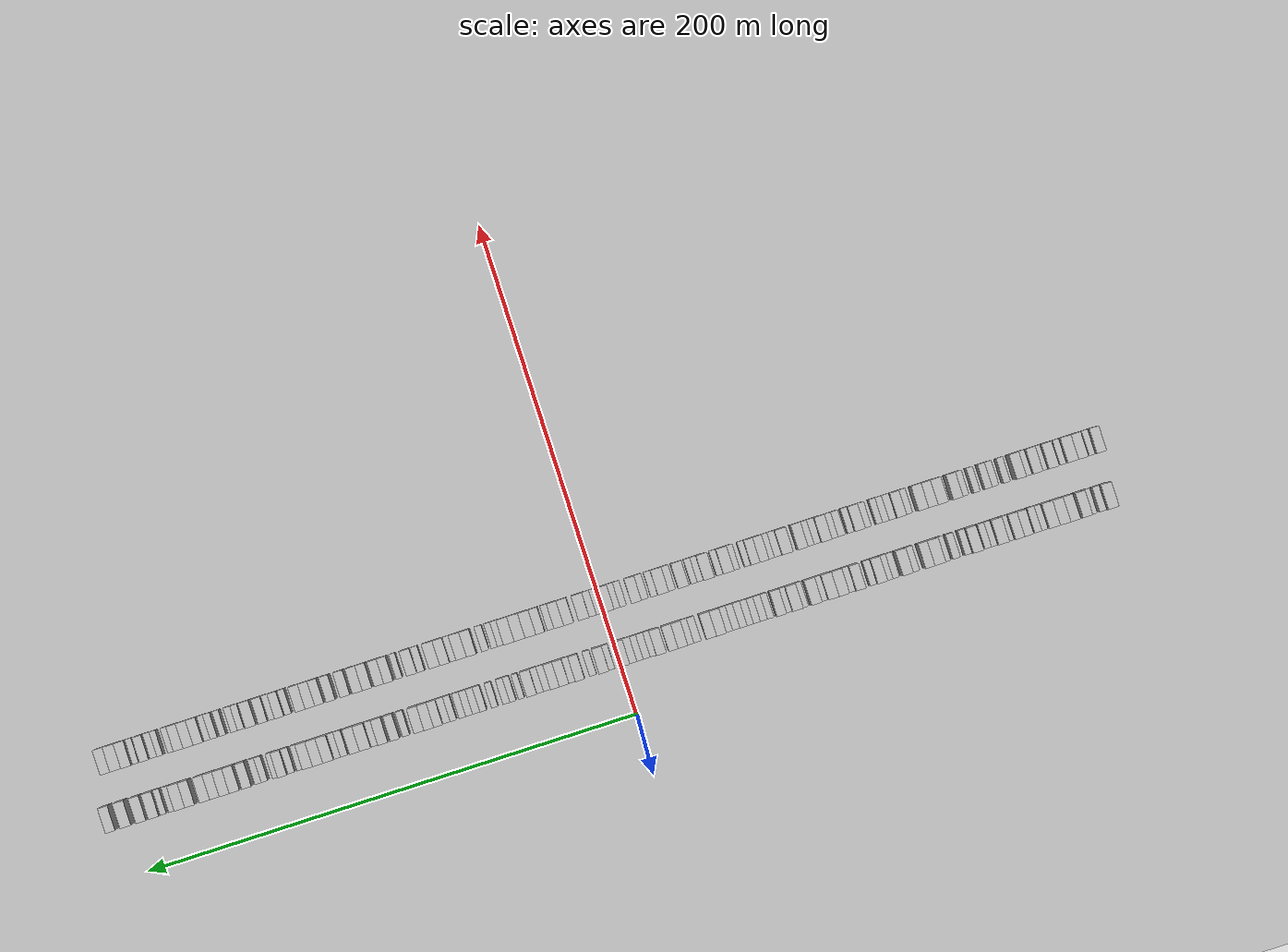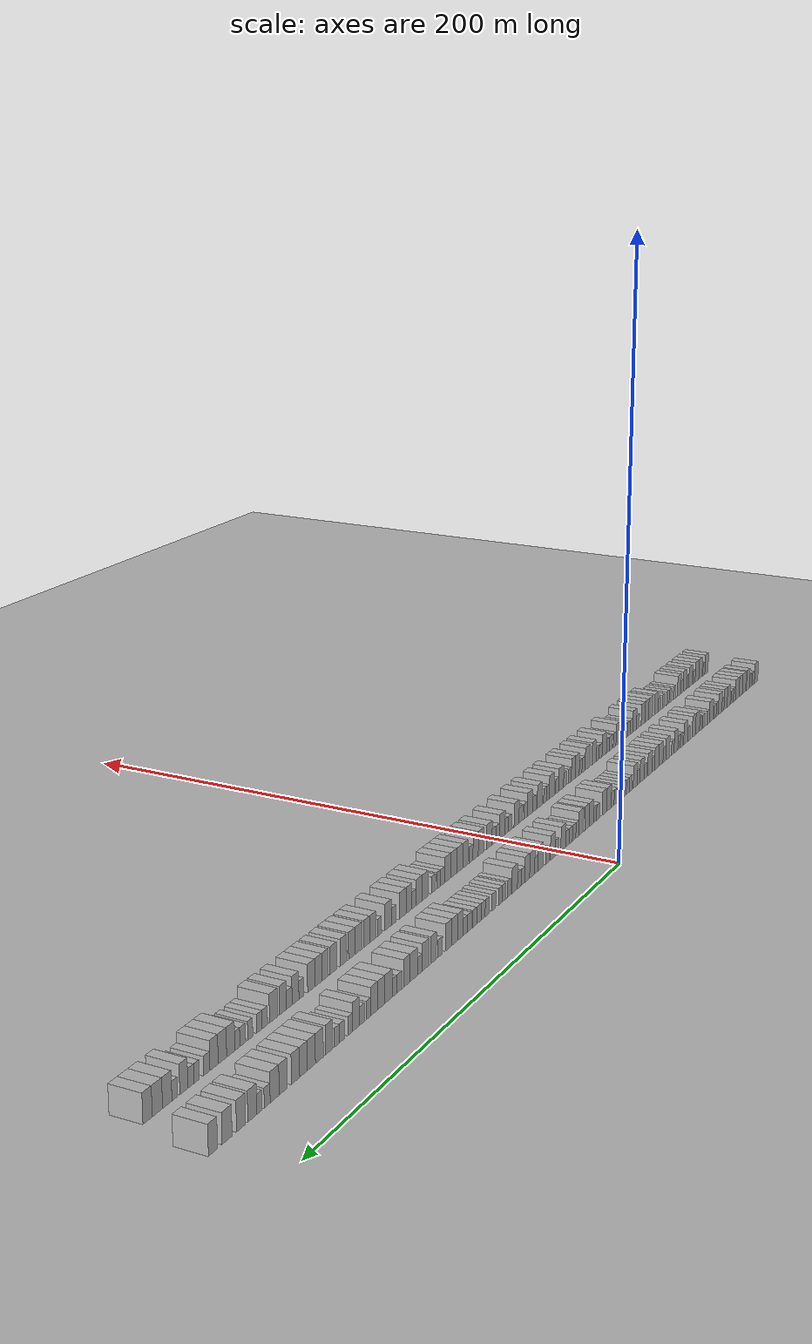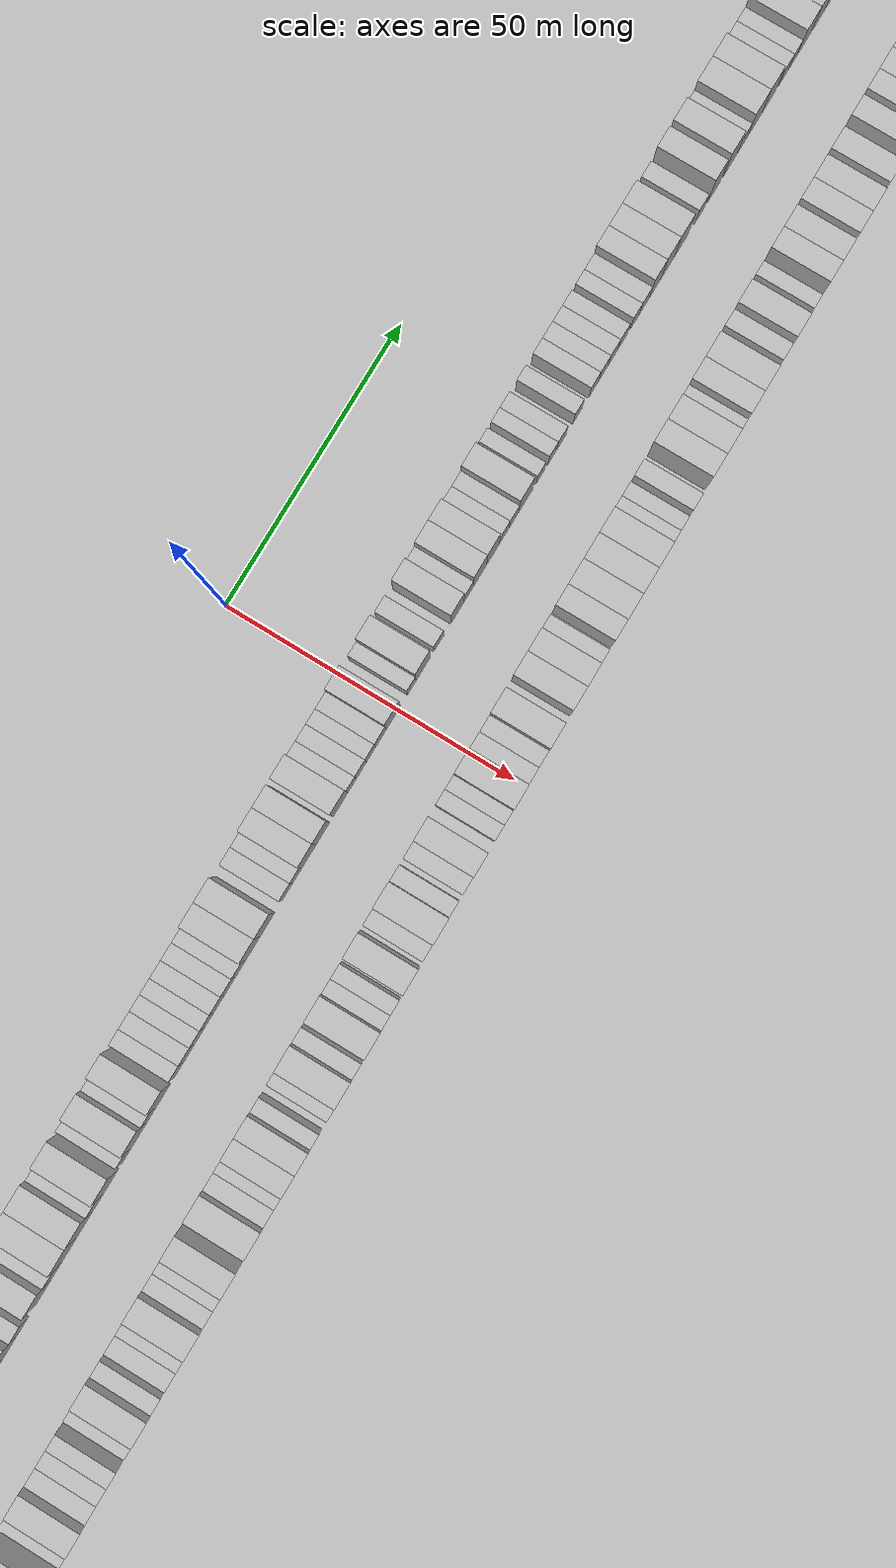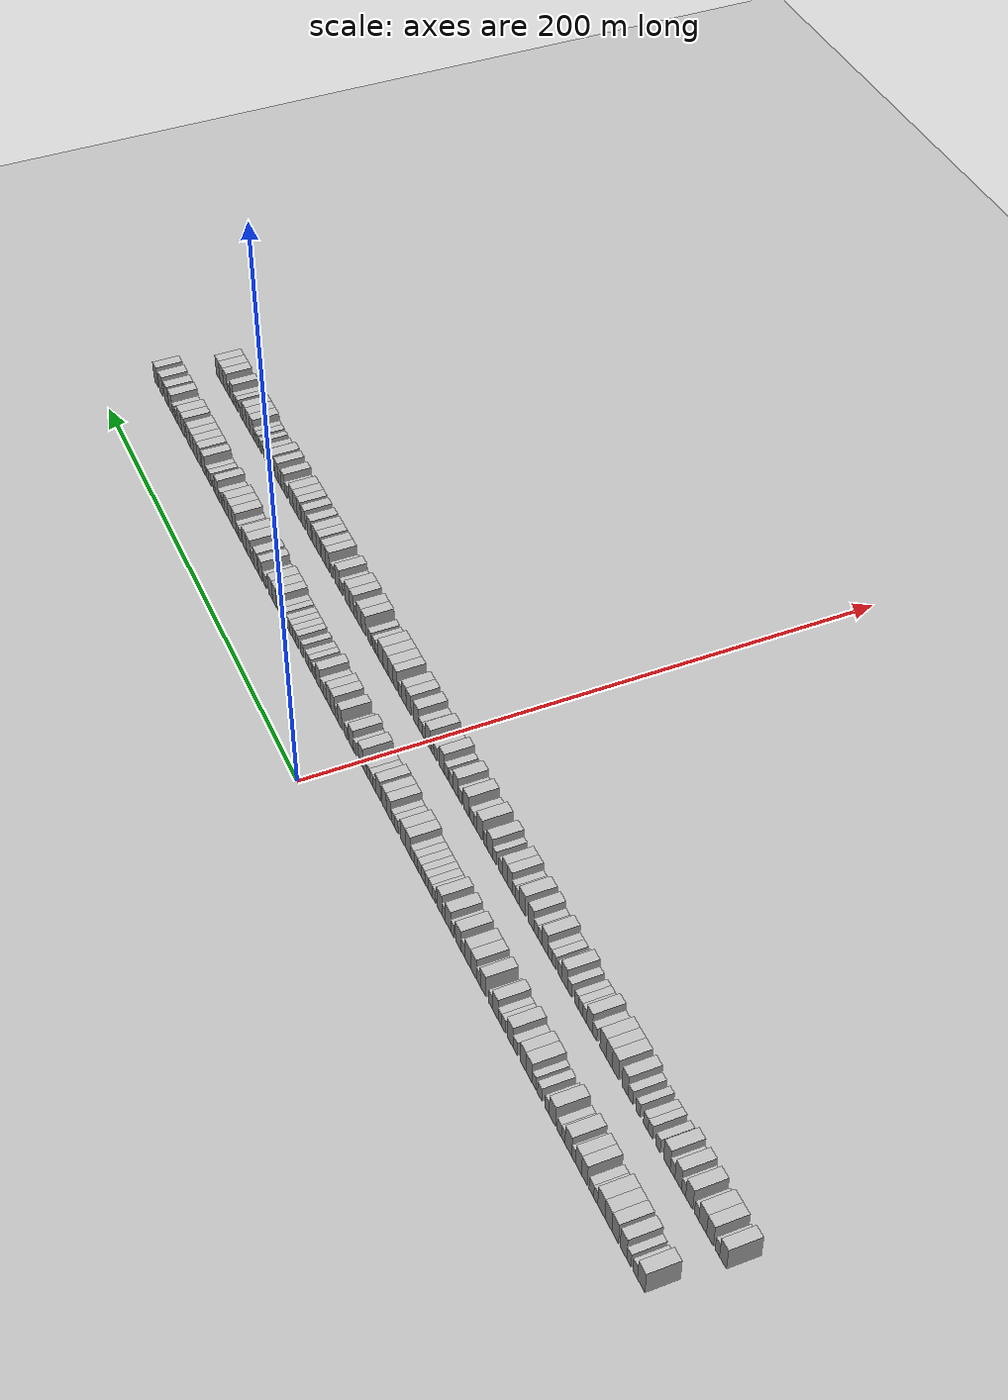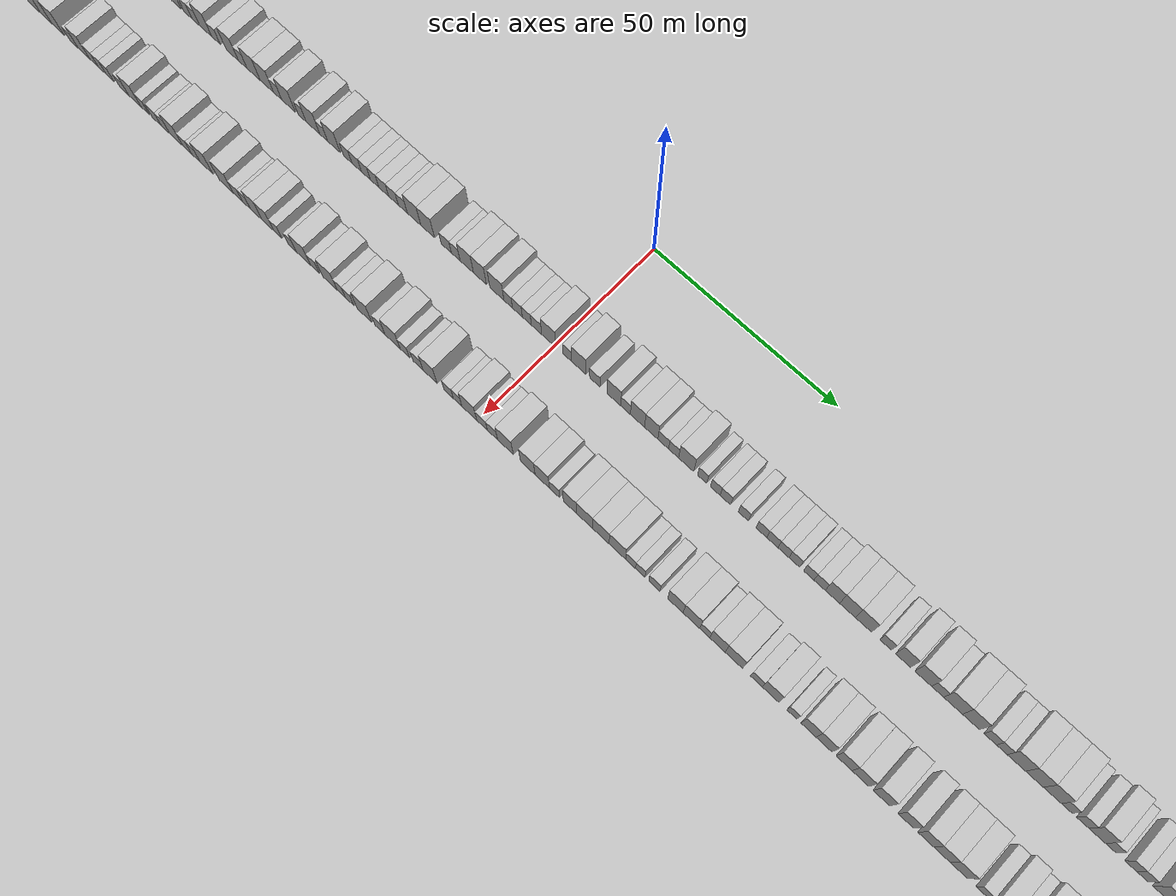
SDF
<?xml version="1.0" encoding="utf-8"?>

<sdf version="1.6">

   <world name="default">

      <gui fullscreen="0">

         <camera name="user_camera">

            <pose>-15 0 4.57585 0 0 0</pose>

            <view_controller>orbit</view_controller>

         </camera>

      </gui>

      <scene>

         <sky>

           <clouds>

             <speed>12</speed>

           </clouds>

         </sky>

         <ambient>0.4 0.4 0.4 1</ambient>

         <background>0.7 0.7 0.7 1</background>

         <shadows>1</shadows>

      </scene>

      <gravity>0 0 -9.8066</gravity>

      <magnetic_field>6e-06 2.3e-05 -4.2e-05</magnetic_field>

      <physics default="0" name="default_physics" type="ode">

         <ode>

            <solver>

               <type>quick</type>

               <iters>10</iters>

               <sor>1.0</sor>

               <use_dynamic_moi_rescaling>0</use_dynamic_moi_rescaling>

            </solver>

            <constraints>

               <cfm>0</cfm>

               <erp>0.2</erp>

               <contact_max_correcting_vel>100</contact_max_correcting_vel>

               <contact_surface_layer>0.001</contact_surface_layer>

            </constraints>

         </ode>

         <max_step_size>0.004</max_step_size>

         <real_time_factor>1</real_time_factor>

         <real_time_update_rate>250</real_time_update_rate>

      </physics>

      <light name="sun" type="directional">

         <cast_shadows>1</cast_shadows>

         <pose>0 0 10 0 0 0</pose>

         <diffuse>0.8 0.8 0.8 1</diffuse>

         <specular>0.2 0.2 0.2 1</specular>

         <attenuation>

            <range>1000</range>

            <constant>0.9</constant>

            <linear>0.01</linear>

            <quadratic>0.001</quadratic>

         </attenuation>

         <direction>-0.5 0.1 -0.9</direction>

      </light>

      <include>

         <name>ground_plane_1</name>

         <uri>model://HANNAS_ground_plane</uri>

         <pose>0 0 0  0 0 0</pose>

      </include>

      <include>

         <name>ground_plane_2</name>

         <uri>model://HANNAS_ground_plane</uri>

         <pose>100 0 0  0 0 0</pose>

      </include>

      <model name="building_1">

         <static>1</static>

         <pose frame="">25.0000 -199.8333 0 0.000000 0.000000 0.000000</pose>

         <link name="link">

            <pose frame="">0 0 4.50 0 0 0</pose>

            <collision name="collision">

               <geometry>

                  <box>

                     <size>10.0000 4.3334 9.0000</size>

                  </box>

               </geometry>

               <max_contacts>10</max_contacts>

               <surface>

                  <contact>

                     <ode/>

                  </contact>

                  <bounce/>

                  <friction>

                     <torsional>

                        <ode/>

                     </torsional>

                     <ode/>

                  </friction>

               </surface>

            </collision>

            <visual name="visual">

               <cast_shadows>0</cast_shadows>

               <geometry>

                  <box>

                     <size>10.0000 4.3334 9.0000</size>

                  </box>

               </geometry>

               <material>

                  <script>

                     <uri>model://HANNAS_wall/materials/scripts</uri>

                     <uri>model://HANNAS_wall/materials/textures</uri>

                     <name>vrc/HANNAS_wall</name>

                  </script>

               </material>

            </visual>

            <self_collide>0</self_collide>

            <enable_wind>0</enable_wind>

            <kinematic>0</kinematic>

         </link>

      </model>

      <model name="building_2">

         <static>1</static>

         <pose frame="">25.0000 -196.2618 0 0.000000 0.000000 0.000000</pose>

         <link name="link">

            <pose frame="">0 0 3.00 0 0 0</pose>

            <collision name="collision">

               <geometry>

                  <box>

                     <size>10.0000 2.8096 6.0000</size>

                  </box>

               </geometry>

               <max_contacts>10</max_contacts>

               <surface>

                  <contact>

                     <ode/>

                  </contact>

                  <bounce/>

                  <friction>

                     <torsional>

                        <ode/>

                     </torsional>

                     <ode/>

                  </friction>

               </surface>

            </collision>

            <visual name="visual">

               <cast_shadows>0</cast_shadows>

               <geometry>

                  <box>

                     <size>10.0000 2.8096 6.0000</size>

                  </box>

               </geometry>

               <material>

                  <script>

                     <uri>model://HANNAS_wall/materials/scripts</uri>

                     <uri>model://HANNAS_wall/materials/textures</uri>

                     <name>vrc/HANNAS_wall</name>

                  </script>

               </material>

            </visual>

            <self_collide>0</self_collide>

            <enable_wind>0</enable_wind>

            <kinematic>0</kinematic>

         </link>

      </model>

      <model name="building_3">

         <static>1</static>

         <pose frame="">25.0000 -192.5719 0 0.000000 0.000000 0.000000</pose>

         <link name="link">

            <pose frame="">0 0 3.00 0 0 0</pose>

            <collision name="collision">

               <geometry>

                  <box>

                     <size>10.0000 2.5702 6.0000</size>

                  </box>

               </geometry>

               <max_contacts>10</max_contacts>

               <surface>

                  <contact>

                     <ode/>

                  </contact>

                  <bounce/>

                  <friction>

                     <torsional>

                        <ode/>

                     </torsional>

                     <ode/>

                  </friction>

               </surface>

            </collision>

            <visual name="visual">

               <cast_shadows>0</cast_shadows>

               <geometry>

                  <box>

                     <size>10.0000 2.5702 6.0000</size>

                  </box>

               </geometry>

               <material>

                  <script>

                     <uri>model://HANNAS_wall/materials/scripts</uri>

                     <uri>model://HANNAS_wall/materials/textures</uri>

                     <name>vrc/HANNAS_wall</name>

                  </script>

               </material>

            </visual>

            <self_collide>0</self_collide>

            <enable_wind>0</enable_wind>

            <kinematic>0</kinematic>

         </link>

      </model>

      <model name="building_4">

         <static>1</static>

         <pose frame="">25.0000 -189.3240 0 0.000000 0.000000 0.000000</pose>

         <link name="link">

            <pose frame="">0 0 4.50 0 0 0</pose>

            <collision name="collision">

               <geometry>

                  <box>

                     <size>10.0000 3.9257 9.0000</size>

                  </box>

               </geometry>

               <max_contacts>10</max_contacts>

               <surface>

                  <contact>

                     <ode/>

                  </contact>

                  <bounce/>

                  <friction>

                     <torsional>

                        <ode/>

                     </torsional>

                     <ode/>

                  </friction>

               </surface>

            </collision>

            <visual name="visual">

               <cast_shadows>0</cast_shadows>

               <geometry>

                  <box>

                     <size>10.0000 3.9257 9.0000</size>

                  </box>

               </geometry>

               <material>

                  <script>

                     <uri>model://HANNAS_wall/materials/scripts</uri>

                     <uri>model://HANNAS_wall/materials/textures</uri>

                     <name>vrc/HANNAS_wall</name>

                  </script>

               </material>

            </visual>

            <self_collide>0</self_collide>

            <enable_wind>0</enable_wind>

            <kinematic>0</kinematic>

         </link>

      </model>

      <model name="building_5">

         <static>1</static>

         <pose frame="">25.0000 -184.3808 0 0.000000 0.000000 0.000000</pose>

         <link name="link">

            <pose frame="">0 0 4.50 0 0 0</pose>

            <collision name="collision">

               <geometry>

                  <box>

                     <size>10.0000 3.9606 9.0000</size>

                  </box>

               </geometry>

               <max_contacts>10</max_contacts>

               <surface>

                  <contact>

                     <ode/>

                  </contact>

                  <bounce/>

                  <friction>

                     <torsional>

                        <ode/>

                     </torsional>

                     <ode/>

                  </friction>

               </surface>

            </collision>

            <visual name="visual">

               <cast_shadows>0</cast_shadows>

               <geometry>

                  <box>

                     <size>10.0000 3.9606 9.0000</size>

                  </box>

               </geometry>

               <material>

                  <script>

                     <uri>model://HANNAS_wall/materials/scripts</uri>

                     <uri>model://HANNAS_wall/materials/textures</uri>

                     <name>vrc/HANNAS_wall</name>

                  </script>

               </material>

            </visual>

            <self_collide>0</self_collide>

            <enable_wind>0</enable_wind>

            <kinematic>0</kinematic>

         </link>

      </model>

      <model name="building_6">

         <static>1</static>

         <pose frame="">25.0000 -180.2848 0 0.000000 0.000000 0.000000</pose>

         <link name="link">

            <pose frame="">0 0 4.50 0 0 0</pose>

            <collision name="collision">

               <geometry>

                  <box>

                     <size>10.0000 4.2314 9.0000</size>

                  </box>

               </geometry>

               <max_contacts>10</max_contacts>

               <surface>

                  <contact>

                     <ode/>

                  </contact>

                  <bounce/>

                  <friction>

                     <torsional>

                        <ode/>

                     </torsional>

                     <ode/>

                  </friction>

               </surface>

            </collision>

            <visual name="visual">

               <cast_shadows>0</cast_shadows>

               <geometry>

                  <box>

                     <size>10.0000 4.2314 9.0000</size>

                  </box>

               </geometry>

               <material>

                  <script>

                     <uri>model://HANNAS_wall/materials/scripts</uri>

                     <uri>model://HANNAS_wall/materials/textures</uri>

                     <name>vrc/HANNAS_wall</name>

                  </script>

               </material>

            </visual>

            <self_collide>0</self_collide>

            <enable_wind>0</enable_wind>

            <kinematic>0</kinematic>

         </link>

      </model>

      <model name="building_7">

         <static>1</static>

         <pose frame="">25.0000 -175.9644 0 0.000000 0.000000 0.000000</pose>

         <link name="link">

            <pose frame="">0 0 4.50 0 0 0</pose>

            <collision name="collision">

               <geometry>

                  <box>

                     <size>10.0000 4.4095 9.0000</size>

                  </box>

               </geometry>

               <max_contacts>10</max_contacts>

               <surface>

                  <contact>

                     <ode/>

                  </contact>

                  <bounce/>

                  <friction>

                     <torsional>

                        <ode/>

                     </torsional>

                     <ode/>

                  </friction>

               </surface>

            </collision>

            <visual name="visual">

               <cast_shadows>0</cast_shadows>

               <geometry>

                  <box>

                     <size>10.0000 4.4095 9.0000</size>

                  </box>

               </geometry>

               <material>

                  <script>

                     <uri>model://HANNAS_wall/materials/scripts</uri>

                     <uri>model://HANNAS_wall/materials/textures</uri>

                     <name>vrc/HANNAS_wall</name>

                  </script>

               </material>

            </visual>

            <self_collide>0</self_collide>

            <enable_wind>0</enable_wind>

            <kinematic>0</kinematic>

         </link>

      </model>

      <model name="building_8">

         <static>1</static>

         <pose frame="">25.0000 -172.5184 0 0.000000 0.000000 0.000000</pose>

         <link name="link">

            <pose frame="">0 0 3.00 0 0 0</pose>

            <collision name="collision">

               <geometry>

                  <box>

                     <size>10.0000 2.4825 6.0000</size>

                  </box>

               </geometry>

               <max_contacts>10</max_contacts>

               <surface>

                  <contact>

                     <ode/>

                  </contact>

                  <bounce/>

                  <friction>

                     <torsional>

                        <ode/>

                     </torsional>

                     <ode/>

                  </friction>

               </surface>

            </collision>

            <visual name="visual">

               <cast_shadows>0</cast_shadows>

               <geometry>

                  <box>

                     <size>10.0000 2.4825 6.0000</size>

                  </box>

               </geometry>

               <material>

                  <script>

                     <uri>model://HANNAS_wall/materials/scripts</uri>

                     <uri>model://HANNAS_wall/materials/textures</uri>

                     <name>vrc/HANNAS_wall</name>

                  </script>

               </material>

            </visual>

            <self_collide>0</self_collide>

            <enable_wind>0</enable_wind>

            <kinematic>0</kinematic>

         </link>

      </model>

      <model name="building_9">

         <static>1</static>

         <pose frame="">25.0000 -169.8211 0 0.000000 0.000000 0.000000</pose>

         <link name="link">

            <pose frame="">0 0 3.00 0 0 0</pose>

            <collision name="collision">

               <geometry>

                  <box>

                     <size>10.0000 2.9121 6.0000</size>

                  </box>

               </geometry>

               <max_contacts>10</max_contacts>

               <surface>

                  <contact>

                     <ode/>

                  </contact>

                  <bounce/>

                  <friction>

                     <torsional>

                        <ode/>

                     </torsional>

                     <ode/>

                  </friction>

               </surface>

            </collision>

            <visual name="visual">

               <cast_shadows>0</cast_shadows>

               <geometry>

                  <box>

                     <size>10.0000 2.9121 6.0000</size>

                  </box>

               </geometry>

               <material>

                  <script>

                     <uri>model://HANNAS_wall/materials/scripts</uri>

                     <uri>model://HANNAS_wall/materials/textures</uri>

                     <name>vrc/HANNAS_wall</name>

                  </script>

               </material>

            </visual>

            <self_collide>0</self_collide>

            <enable_wind>0</enable_wind>

            <kinematic>0</kinematic>

         </link>

      </model>

      <model name="building_10">

         <static>1</static>

         <pose frame="">25.0000 -165.5450 0 0.000000 0.000000 0.000000</pose>

         <link name="link">

            <pose frame="">0 0 4.50 0 0 0</pose>

            <collision name="collision">

               <geometry>

                  <box>

                     <size>10.0000 3.6400 9.0000</size>

                  </box>

               </geometry>

               <max_contacts>10</max_contacts>

               <surface>

                  <contact>

                     <ode/>

                  </contact>

                  <bounce/>

                  <friction>

                     <torsional>

                        <ode/>

                     </torsional>

                     <ode/>

                  </friction>

               </surface>

            </collision>

            <visual name="visual">

               <cast_shadows>0</cast_shadows>

               <geometry>

                  <box>

                     <size>10.0000 3.6400 9.0000</size>

                  </box>

               </geometry>

               <material>

                  <script>

                     <uri>model://HANNAS_wall/materials/scripts</uri>

                     <uri>model://HANNAS_wall/materials/textures</uri>

                     <name>vrc/HANNAS_wall</name>

                  </script>

               </material>

            </visual>

            <self_collide>0</self_collide>

            <enable_wind>0</enable_wind>

            <kinematic>0</kinematic>

         </link>

      </model>

      <model name="building_11">

         <static>1</static>

         <pose frame="">25.0000 -161.8623 0 0.000000 0.000000 0.000000</pose>

         <link name="link">

            <pose frame="">0 0 4.50 0 0 0</pose>

            <collision name="collision">

               <geometry>

                  <box>

                     <size>10.0000 3.7253 9.0000</size>

                  </box>

               </geometry>

               <max_contacts>10</max_contacts>

               <surface>

                  <contact>

                     <ode/>

                  </contact>

                  <bounce/>

                  <friction>

                     <torsional>

                        <ode/>

                     </torsional>

                     <ode/>

                  </friction>

               </surface>

            </collision>

            <visual name="visual">

               <cast_shadows>0</cast_shadows>

               <geometry>

                  <box>

                     <size>10.0000 3.7253 9.0000</size>

                  </box>

               </geometry>

               <material>

                  <script>

                     <uri>model://HANNAS_wall/materials/scripts</uri>

                     <uri>model://HANNAS_wall/materials/textures</uri>

                     <name>vrc/HANNAS_wall</name>

                  </script>

               </material>

            </visual>

            <self_collide>0</self_collide>

            <enable_wind>0</enable_wind>

            <kinematic>0</kinematic>

         </link>

      </model>

      <model name="building_12">

         <static>1</static>

         <pose frame="">25.0000 -158.7786 0 0.000000 0.000000 0.000000</pose>

         <link name="link">

            <pose frame="">0 0 3.00 0 0 0</pose>

            <collision name="collision">

               <geometry>

                  <box>

                     <size>10.0000 2.4423 6.0000</size>

                  </box>

               </geometry>

               <max_contacts>10</max_contacts>

               <surface>

                  <contact>

                     <ode/>

                  </contact>

                  <bounce/>

                  <friction>

                     <torsional>

                        <ode/>

                     </torsional>

                     <ode/>

                  </friction>

               </surface>

            </collision>

            <visual name="visual">

               <cast_shadows>0</cast_shadows>

               <geometry>

                  <box>

                     <size>10.0000 2.4423 6.0000</size>

                  </box>

               </geometry>

               <material>

                  <script>

                     <uri>model://HANNAS_wall/materials/scripts</uri>

                     <uri>model://HANNAS_wall/materials/textures</uri>

                     <name>vrc/HANNAS_wall</name>

                  </script>

               </material>

            </visual>

            <self_collide>0</self_collide>

            <enable_wind>0</enable_wind>

            <kinematic>0</kinematic>

         </link>

      </model>

      <model name="building_13">

         <static>1</static>

         <pose frame="">25.0000 -155.3770 0 0.000000 0.000000 0.000000</pose>

         <link name="link">

            <pose frame="">0 0 4.50 0 0 0</pose>

            <collision name="collision">

               <geometry>

                  <box>

                     <size>10.0000 4.3609 9.0000</size>

                  </box>

               </geometry>

               <max_contacts>10</max_contacts>

               <surface>

                  <contact>

                     <ode/>

                  </contact>

                  <bounce/>

                  <friction>

                     <torsional>

                        <ode/>

                     </torsional>

                     <ode/>

                  </friction>

               </surface>

            </collision>

            <visual name="visual">

               <cast_shadows>0</cast_shadows>

               <geometry>

                  <box>

                     <size>10.0000 4.3609 9.0000</size>

                  </box>

               </geometry>

               <material>

                  <script>

                     <uri>model://HANNAS_wall/materials/scripts</uri>

                     <uri>model://HANNAS_wall/materials/textures</uri>

                     <name>vrc/HANNAS_wall</name>

                  </script>

               </material>

            </visual>

            <self_collide>0</self_collide>

            <enable_wind>0</enable_wind>

            <kinematic>0</kinematic>

         </link>

      </model>

      <model name="building_14">

         <static>1</static>

         <pose frame="">25.0000 -151.9902 0 0.000000 0.000000 0.000000</pose>

         <link name="link">

            <pose frame="">0 0 3.00 0 0 0</pose>

            <collision name="collision">

               <geometry>

                  <box>

                     <size>10.0000 2.4127 6.0000</size>

                  </box>

               </geometry>

               <max_contacts>10</max_contacts>

               <surface>

                  <contact>

                     <ode/>

                  </contact>

                  <bounce/>

                  <friction>

                     <torsional>

                        <ode/>

                     </torsional>

                     <ode/>

                  </friction>

               </surface>

            </collision>

            <visual name="visual">

               <cast_shadows>0</cast_shadows>

               <geometry>

                  <box>

                     <size>10.0000 2.4127 6.0000</size>

                  </box>

               </geometry>

               <material>

                  <script>

                     <uri>model://HANNAS_wall/materials/scripts</uri>

                     <uri>model://HANNAS_wall/materials/textures</uri>

                     <name>vrc/HANNAS_wall</name>

                  </script>

               </material>

            </visual>

            <self_collide>0</self_collide>

            <enable_wind>0</enable_wind>

            <kinematic>0</kinematic>

         </link>

      </model>

      <model name="building_15">

         <static>1</static>

         <pose frame="">25.0000 -149.4547 0 0.000000 0.000000 0.000000</pose>

         <link name="link">

            <pose frame="">0 0 3.00 0 0 0</pose>

            <collision name="collision">

               <geometry>

                  <box>

                     <size>10.0000 2.6583 6.0000</size>

                  </box>

               </geometry>

               <max_contacts>10</max_contacts>

               <surface>

                  <contact>

                     <ode/>

                  </contact>

                  <bounce/>

                  <friction>

                     <torsional>

                        <ode/>

                     </torsional>

                     <ode/>

                  </friction>

               </surface>

            </collision>

            <visual name="visual">

               <cast_shadows>0</cast_shadows>

               <geometry>

                  <box>

                     <size>10.0000 2.6583 6.0000</size>

                  </box>

               </geometry>

               <material>

                  <script>

                     <uri>model://HANNAS_wall/materials/scripts</uri>

                     <uri>model://HANNAS_wall/materials/textures</uri>

                     <name>vrc/HANNAS_wall</name>

                  </script>

               </material>

            </visual>

            <self_collide>0</self_collide>

            <enable_wind>0</enable_wind>

            <kinematic>0</kinematic>

         </link>

      </model>

      <model name="building_16">

         <static>1</static>

         <pose frame="">25.0000 -145.0097 0 0.000000 0.000000 0.000000</pose>

         <link name="link">

            <pose frame="">0 0 4.50 0 0 0</pose>

            <collision name="collision">

               <geometry>

                  <box>

                     <size>10.0000 4.2316 9.0000</size>

                  </box>

               </geometry>

               <max_contacts>10</max_contacts>

               <surface>

                  <contact>

                     <ode/>

                  </contact>

                  <bounce/>

                  <friction>

                     <torsional>

                        <ode/>

                     </torsional>

                     <ode/>

                  </friction>

               </surface>

            </collision>

            <visual name="visual">

               <cast_shadows>0</cast_shadows>

               <geometry>

                  <box>

                     <size>10.0000 4.2316 9.0000</size>

                  </box>

               </geometry>

               <material>

                  <script>

                     <uri>model://HANNAS_wall/materials/scripts</uri>

                     <uri>model://HANNAS_wall/materials/textures</uri>

                     <name>vrc/HANNAS_wall</name>

                  </script>

               </material>

            </visual>

            <self_collide>0</self_collide>

            <enable_wind>0</enable_wind>

            <kinematic>0</kinematic>

         </link>

      </model>

      <model name="building_17">

         <static>1</static>

         <pose frame="">25.0000 -141.5099 0 0.000000 0.000000 0.000000</pose>

         <link name="link">

            <pose frame="">0 0 3.00 0 0 0</pose>

            <collision name="collision">

               <geometry>

                  <box>

                     <size>10.0000 2.7680 6.0000</size>

                  </box>

               </geometry>

               <max_contacts>10</max_contacts>

               <surface>

                  <contact>

                     <ode/>

                  </contact>

                  <bounce/>

                  <friction>

                     <torsional>

                        <ode/>

                     </torsional>

                     <ode/>

                  </friction>

               </surface>

            </collision>

            <visual name="visual">

               <cast_shadows>0</cast_shadows>

               <geometry>

                  <box>

                     <size>10.0000 2.7680 6.0000</size>

                  </box>

               </geometry>

               <material>

                  <script>

                     <uri>model://HANNAS_wall/materials/scripts</uri>

                     <uri>model://HANNAS_wall/materials/textures</uri>

                     <name>vrc/HANNAS_wall</name>

                  </script>

               </material>

            </visual>

            <self_collide>0</self_collide>

            <enable_wind>0</enable_wind>

            <kinematic>0</kinematic>

         </link>

      </model>

      <model name="building_18">

         <static>1</static>

         <pose frame="">25.0000 -136.6459 0 0.000000 0.000000 0.000000</pose>

         <link name="link">

            <pose frame="">0 0 3.00 0 0 0</pose>

            <collision name="collision">

               <geometry>

                  <box>

                     <size>10.0000 2.9599 6.0000</size>

                  </box>

               </geometry>

               <max_contacts>10</max_contacts>

               <surface>

                  <contact>

                     <ode/>

                  </contact>

                  <bounce/>

                  <friction>

                     <torsional>

                        <ode/>

                     </torsional>

                     <ode/>

                  </friction>

               </surface>

            </collision>

            <visual name="visual">

               <cast_shadows>0</cast_shadows>

               <geometry>

                  <box>

                     <size>10.0000 2.9599 6.0000</size>

                  </box>

               </geometry>

               <material>

                  <script>

                     <uri>model://HANNAS_wall/materials/scripts</uri>

                     <uri>model://HANNAS_wall/materials/textures</uri>

                     <name>vrc/HANNAS_wall</name>

                  </script>

               </material>

            </visual>

            <self_collide>0</self_collide>

            <enable_wind>0</enable_wind>

            <kinematic>0</kinematic>

         </link>

      </model>

      <model name="building_19">

         <static>1</static>

         <pose frame="">25.0000 -132.9548 0 0.000000 0.000000 0.000000</pose>

         <link name="link">

            <pose frame="">0 0 3.00 0 0 0</pose>

            <collision name="collision">

               <geometry>

                  <box>

                     <size>10.0000 2.4223 6.0000</size>

                  </box>

               </geometry>

               <max_contacts>10</max_contacts>

               <surface>

                  <contact>

                     <ode/>

                  </contact>

                  <bounce/>

                  <friction>

                     <torsional>

                        <ode/>

                     </torsional>

                     <ode/>

                  </friction>

               </surface>

            </collision>

            <visual name="visual">

               <cast_shadows>0</cast_shadows>

               <geometry>

                  <box>

                     <size>10.0000 2.4223 6.0000</size>

                  </box>

               </geometry>

               <material>

                  <script>

                     <uri>model://HANNAS_wall/materials/scripts</uri>

                     <uri>model://HANNAS_wall/materials/textures</uri>

                     <name>vrc/HANNAS_wall</name>

                  </script>

               </material>

            </visual>

            <self_collide>0</self_collide>

            <enable_wind>0</enable_wind>

            <kinematic>0</kinematic>

         </link>

      </model>

      <model name="building_20">

         <static>1</static>

         <pose frame="">25.0000 -129.5151 0 0.000000 0.000000 0.000000</pose>

         <link name="link">

            <pose frame="">0 0 4.50 0 0 0</pose>

            <collision name="collision">

               <geometry>

                  <box>

                     <size>10.0000 4.4571 9.0000</size>

                  </box>

               </geometry>

               <max_contacts>10</max_contacts>

               <surface>

                  <contact>

                     <ode/>

                  </contact>

                  <bounce/>

                  <friction>

                     <torsional>

                        <ode/>

                     </torsional>

                     <ode/>

                  </friction>

               </surface>

            </collision>

            <visual name="visual">

               <cast_shadows>0</cast_shadows>

               <geometry>

                  <box>

                     <size>10.0000 4.4571 9.0000</size>

                  </box>

               </geometry>

               <material>

                  <script>

                     <uri>model://HANNAS_wall/materials/scripts</uri>

                     <uri>model://HANNAS_wall/materials/textures</uri>

                     <name>vrc/HANNAS_wall</name>

                  </script>

               </material>

            </visual>

            <self_collide>0</self_collide>

            <enable_wind>0</enable_wind>

            <kinematic>0</kinematic>

         </link>

      </model>

      <model name="building_21">

         <static>1</static>

         <pose frame="">25.0000 -125.4136 0 0.000000 0.000000 0.000000</pose>

         <link name="link">

            <pose frame="">0 0 4.50 0 0 0</pose>

            <collision name="collision">

               <geometry>

                  <box>

                     <size>10.0000 3.7458 9.0000</size>

                  </box>

               </geometry>

               <max_contacts>10</max_contacts>

               <surface>

                  <contact>

                     <ode/>

                  </contact>

                  <bounce/>

                  <friction>

                     <torsional>

                        <ode/>

                     </torsional>

                     <ode/>

                  </friction>

               </surface>

            </collision>

            <visual name="visual">

               <cast_shadows>0</cast_shadows>

               <geometry>

                  <box>

                     <size>10.0000 3.7458 9.0000</size>

                  </box>

               </geometry>

               <material>

                  <script>

                     <uri>model://HANNAS_wall/materials/scripts</uri>

                     <uri>model://HANNAS_wall/materials/textures</uri>

                     <name>vrc/HANNAS_wall</name>

                  </script>

               </material>

            </visual>

            <self_collide>0</self_collide>

            <enable_wind>0</enable_wind>

            <kinematic>0</kinematic>

         </link>

      </model>

      <model name="building_22">

         <static>1</static>

         <pose frame="">25.0000 -120.0631 0 0.000000 0.000000 0.000000</pose>

         <link name="link">

            <pose frame="">0 0 3.00 0 0 0</pose>

            <collision name="collision">

               <geometry>

                  <box>

                     <size>10.0000 2.9552 6.0000</size>

                  </box>

               </geometry>

               <max_contacts>10</max_contacts>

               <surface>

                  <contact>

                     <ode/>

                  </contact>

                  <bounce/>

                  <friction>

                     <torsional>

                        <ode/>

                     </torsional>

                     <ode/>

                  </friction>

               </surface>

            </collision>

            <visual name="visual">

               <cast_shadows>0</cast_shadows>

               <geometry>

                  <box>

                     <size>10.0000 2.9552 6.0000</size>

                  </box>

               </geometry>

               <material>

                  <script>

                     <uri>model://HANNAS_wall/materials/scripts</uri>

                     <uri>model://HANNAS_wall/materials/textures</uri>

                     <name>vrc/HANNAS_wall</name>

                  </script>

               </material>

            </visual>

            <self_collide>0</self_collide>

            <enable_wind>0</enable_wind>

            <kinematic>0</kinematic>

         </link>

      </model>

      <model name="building_23">

         <static>1</static>

         <pose frame="">25.0000 -116.4614 0 0.000000 0.000000 0.000000</pose>

         <link name="link">

            <pose frame="">0 0 4.50 0 0 0</pose>

            <collision name="collision">

               <geometry>

                  <box>

                     <size>10.0000 4.2482 9.0000</size>

                  </box>

               </geometry>

               <max_contacts>10</max_contacts>

               <surface>

                  <contact>

                     <ode/>

                  </contact>

                  <bounce/>

                  <friction>

                     <torsional>

                        <ode/>

                     </torsional>

                     <ode/>

                  </friction>

               </surface>

            </collision>

            <visual name="visual">

               <cast_shadows>0</cast_shadows>

               <geometry>

                  <box>

                     <size>10.0000 4.2482 9.0000</size>

                  </box>

               </geometry>

               <material>

                  <script>

                     <uri>model://HANNAS_wall/materials/scripts</uri>

                     <uri>model://HANNAS_wall/materials/textures</uri>

                     <name>vrc/HANNAS_wall</name>

                  </script>

               </material>

            </visual>

            <self_collide>0</self_collide>

            <enable_wind>0</enable_wind>

            <kinematic>0</kinematic>

         </link>

      </model>

      <model name="building_24">

         <static>1</static>

         <pose frame="">25.0000 -112.0185 0 0.000000 0.000000 0.000000</pose>

         <link name="link">

            <pose frame="">0 0 3.00 0 0 0</pose>

            <collision name="collision">

               <geometry>

                  <box>

                     <size>10.0000 2.6375 6.0000</size>

                  </box>

               </geometry>

               <max_contacts>10</max_contacts>

               <surface>

                  <contact>

                     <ode/>

                  </contact>

                  <bounce/>

                  <friction>

                     <torsional>

                        <ode/>

                     </torsional>

                     <ode/>

                  </friction>

               </surface>

            </collision>

            <visual name="visual">

               <cast_shadows>0</cast_shadows>

               <geometry>

                  <box>

                     <size>10.0000 2.6375 6.0000</size>

                  </box>

               </geometry>

               <material>

                  <script>

                     <uri>model://HANNAS_wall/materials/scripts</uri>

                     <uri>model://HANNAS_wall/materials/textures</uri>

                     <name>vrc/HANNAS_wall</name>

                  </script>

               </material>

            </visual>

            <self_collide>0</self_collide>

            <enable_wind>0</enable_wind>

            <kinematic>0</kinematic>

         </link>

      </model>

      <model name="building_25">

         <static>1</static>

         <pose frame="">25.0000 -109.4265 0 0.000000 0.000000 0.000000</pose>

         <link name="link">

            <pose frame="">0 0 3.00 0 0 0</pose>

            <collision name="collision">

               <geometry>

                  <box>

                     <size>10.0000 2.5464 6.0000</size>

                  </box>

               </geometry>

               <max_contacts>10</max_contacts>

               <surface>

                  <contact>

                     <ode/>

                  </contact>

                  <bounce/>

                  <friction>

                     <torsional>

                        <ode/>

                     </torsional>

                     <ode/>

                  </friction>

               </surface>

            </collision>

            <visual name="visual">

               <cast_shadows>0</cast_shadows>

               <geometry>

                  <box>

                     <size>10.0000 2.5464 6.0000</size>

                  </box>

               </geometry>

               <material>

                  <script>

                     <uri>model://HANNAS_wall/materials/scripts</uri>

                     <uri>model://HANNAS_wall/materials/textures</uri>

                     <name>vrc/HANNAS_wall</name>

                  </script>

               </material>

            </visual>

            <self_collide>0</self_collide>

            <enable_wind>0</enable_wind>

            <kinematic>0</kinematic>

         </link>

      </model>

      <model name="building_26">

         <static>1</static>

         <pose frame="">25.0000 -106.1622 0 0.000000 0.000000 0.000000</pose>

         <link name="link">

            <pose frame="">0 0 4.50 0 0 0</pose>

            <collision name="collision">

               <geometry>

                  <box>

                     <size>10.0000 3.9821 9.0000</size>

                  </box>

               </geometry>

               <max_contacts>10</max_contacts>

               <surface>

                  <contact>

                     <ode/>

                  </contact>

                  <bounce/>

                  <friction>

                     <torsional>

                        <ode/>

                     </torsional>

                     <ode/>

                  </friction>

               </surface>

            </collision>

            <visual name="visual">

               <cast_shadows>0</cast_shadows>

               <geometry>

                  <box>

                     <size>10.0000 3.9821 9.0000</size>

                  </box>

               </geometry>

               <material>

                  <script>

                     <uri>model://HANNAS_wall/materials/scripts</uri>

                     <uri>model://HANNAS_wall/materials/textures</uri>

                     <name>vrc/HANNAS_wall</name>

                  </script>

               </material>

            </visual>

            <self_collide>0</self_collide>

            <enable_wind>0</enable_wind>

            <kinematic>0</kinematic>

         </link>

      </model>

      <model name="building_27">

         <static>1</static>

         <pose frame="">25.0000 -102.7813 0 0.000000 0.000000 0.000000</pose>

         <link name="link">

            <pose frame="">0 0 3.00 0 0 0</pose>

            <collision name="collision">

               <geometry>

                  <box>

                     <size>10.0000 2.7798 6.0000</size>

                  </box>

               </geometry>

               <max_contacts>10</max_contacts>

               <surface>

                  <contact>

                     <ode/>

                  </contact>

                  <bounce/>

                  <friction>

                     <torsional>

                        <ode/>

                     </torsional>

                     <ode/>

                  </friction>

               </surface>

            </collision>

            <visual name="visual">

               <cast_shadows>0</cast_shadows>

               <geometry>

                  <box>

                     <size>10.0000 2.7798 6.0000</size>

                  </box>

               </geometry>

               <material>

                  <script>

                     <uri>model://HANNAS_wall/materials/scripts</uri>

                     <uri>model://HANNAS_wall/materials/textures</uri>

                     <name>vrc/HANNAS_wall</name>

                  </script>

               </material>

            </visual>

            <self_collide>0</self_collide>

            <enable_wind>0</enable_wind>

            <kinematic>0</kinematic>

         </link>

      </model>

      <model name="building_28">

         <static>1</static>

         <pose frame="">25.0000 -97.4306 0 0.000000 0.000000 0.000000</pose>

         <link name="link">

            <pose frame="">0 0 4.50 0 0 0</pose>

            <collision name="collision">

               <geometry>

                  <box>

                     <size>10.0000 3.9216 9.0000</size>

                  </box>

               </geometry>

               <max_contacts>10</max_contacts>

               <surface>

                  <contact>

                     <ode/>

                  </contact>

                  <bounce/>

                  <friction>

                     <torsional>

                        <ode/>

                     </torsional>

                     <ode/>

                  </friction>

               </surface>

            </collision>

            <visual name="visual">

               <cast_shadows>0</cast_shadows>

               <geometry>

                  <box>

                     <size>10.0000 3.9216 9.0000</size>

                  </box>

               </geometry>

               <material>

                  <script>

                     <uri>model://HANNAS_wall/materials/scripts</uri>

                     <uri>model://HANNAS_wall/materials/textures</uri>

                     <name>vrc/HANNAS_wall</name>

                  </script>

               </material>

            </visual>

            <self_collide>0</self_collide>

            <enable_wind>0</enable_wind>

            <kinematic>0</kinematic>

         </link>

      </model>

      <model name="building_29">

         <static>1</static>

         <pose frame="">25.0000 -94.0708 0 0.000000 0.000000 0.000000</pose>

         <link name="link">

            <pose frame="">0 0 3.00 0 0 0</pose>

            <collision name="collision">

               <geometry>

                  <box>

                     <size>10.0000 2.7980 6.0000</size>

                  </box>

               </geometry>

               <max_contacts>10</max_contacts>

               <surface>

                  <contact>

                     <ode/>

                  </contact>

                  <bounce/>

                  <friction>

                     <torsional>

                        <ode/>

                     </torsional>

                     <ode/>

                  </friction>

               </surface>

            </collision>

            <visual name="visual">

               <cast_shadows>0</cast_shadows>

               <geometry>

                  <box>

                     <size>10.0000 2.7980 6.0000</size>

                  </box>

               </geometry>

               <material>

                  <script>

                     <uri>model://HANNAS_wall/materials/scripts</uri>

                     <uri>model://HANNAS_wall/materials/textures</uri>

                     <name>vrc/HANNAS_wall</name>

                  </script>

               </material>

            </visual>

            <self_collide>0</self_collide>

            <enable_wind>0</enable_wind>

            <kinematic>0</kinematic>

         </link>

      </model>

      <model name="building_30">

         <static>1</static>

         <pose frame="">25.0000 -90.5573 0 0.000000 0.000000 0.000000</pose>

         <link name="link">

            <pose frame="">0 0 4.50 0 0 0</pose>

            <collision name="collision">

               <geometry>

                  <box>

                     <size>10.0000 4.2291 9.0000</size>

                  </box>

               </geometry>

               <max_contacts>10</max_contacts>

               <surface>

                  <contact>

                     <ode/>

                  </contact>

                  <bounce/>

                  <friction>

                     <torsional>

                        <ode/>

                     </torsional>

                     <ode/>

                  </friction>

               </surface>

            </collision>

            <visual name="visual">

               <cast_shadows>0</cast_shadows>

               <geometry>

                  <box>

                     <size>10.0000 4.2291 9.0000</size>

                  </box>

               </geometry>

               <material>

                  <script>

                     <uri>model://HANNAS_wall/materials/scripts</uri>

                     <uri>model://HANNAS_wall/materials/textures</uri>

                     <name>vrc/HANNAS_wall</name>

                  </script>

               </material>

            </visual>

            <self_collide>0</self_collide>

            <enable_wind>0</enable_wind>

            <kinematic>0</kinematic>

         </link>

      </model>

      <model name="building_31">

         <static>1</static>

         <pose frame="">25.0000 -86.3015 0 0.000000 0.000000 0.000000</pose>

         <link name="link">

            <pose frame="">0 0 4.50 0 0 0</pose>

            <collision name="collision">

               <geometry>

                  <box>

                     <size>10.0000 4.2824 9.0000</size>

                  </box>

               </geometry>

               <max_contacts>10</max_contacts>

               <surface>

                  <contact>

                     <ode/>

                  </contact>

                  <bounce/>

                  <friction>

                     <torsional>

                        <ode/>

                     </torsional>

                     <ode/>

                  </friction>

               </surface>

            </collision>

            <visual name="visual">

               <cast_shadows>0</cast_shadows>

               <geometry>

                  <box>

                     <size>10.0000 4.2824 9.0000</size>

                  </box>

               </geometry>

               <material>

                  <script>

                     <uri>model://HANNAS_wall/materials/scripts</uri>

                     <uri>model://HANNAS_wall/materials/textures</uri>

                     <name>vrc/HANNAS_wall</name>

                  </script>

               </material>

            </visual>

            <self_collide>0</self_collide>

            <enable_wind>0</enable_wind>

            <kinematic>0</kinematic>

         </link>

      </model>

      <model name="building_32">

         <static>1</static>

         <pose frame="">25.0000 -82.8754 0 0.000000 0.000000 0.000000</pose>

         <link name="link">

            <pose frame="">0 0 3.00 0 0 0</pose>

            <collision name="collision">

               <geometry>

                  <box>

                     <size>10.0000 2.5700 6.0000</size>

                  </box>

               </geometry>

               <max_contacts>10</max_contacts>

               <surface>

                  <contact>

                     <ode/>

                  </contact>

                  <bounce/>

                  <friction>

                     <torsional>

                        <ode/>

                     </torsional>

                     <ode/>

                  </friction>

               </surface>

            </collision>

            <visual name="visual">

               <cast_shadows>0</cast_shadows>

               <geometry>

                  <box>

                     <size>10.0000 2.5700 6.0000</size>

                  </box>

               </geometry>

               <material>

                  <script>

                     <uri>model://HANNAS_wall/materials/scripts</uri>

                     <uri>model://HANNAS_wall/materials/textures</uri>

                     <name>vrc/HANNAS_wall</name>

                  </script>

               </material>

            </visual>

            <self_collide>0</self_collide>

            <enable_wind>0</enable_wind>

            <kinematic>0</kinematic>

         </link>

      </model>

      <model name="building_33">

         <static>1</static>

         <pose frame="">25.0000 -79.4284 0 0.000000 0.000000 0.000000</pose>

         <link name="link">

            <pose frame="">0 0 4.50 0 0 0</pose>

            <collision name="collision">

               <geometry>

                  <box>

                     <size>10.0000 4.3240 9.0000</size>

                  </box>

               </geometry>

               <max_contacts>10</max_contacts>

               <surface>

                  <contact>

                     <ode/>

                  </contact>

                  <bounce/>

                  <friction>

                     <torsional>

                        <ode/>

                     </torsional>

                     <ode/>

                  </friction>

               </surface>

            </collision>

            <visual name="visual">

               <cast_shadows>0</cast_shadows>

               <geometry>

                  <box>

                     <size>10.0000 4.3240 9.0000</size>

                  </box>

               </geometry>

               <material>

                  <script>

                     <uri>model://HANNAS_wall/materials/scripts</uri>

                     <uri>model://HANNAS_wall/materials/textures</uri>

                     <name>vrc/HANNAS_wall</name>

                  </script>

               </material>

            </visual>

            <self_collide>0</self_collide>

            <enable_wind>0</enable_wind>

            <kinematic>0</kinematic>

         </link>

      </model>

      <model name="building_34">

         <static>1</static>

         <pose frame="">25.0000 -75.0642 0 0.000000 0.000000 0.000000</pose>

         <link name="link">

            <pose frame="">0 0 3.00 0 0 0</pose>

            <collision name="collision">

               <geometry>

                  <box>

                     <size>10.0000 2.4042 6.0000</size>

                  </box>

               </geometry>

               <max_contacts>10</max_contacts>

               <surface>

                  <contact>

                     <ode/>

                  </contact>

                  <bounce/>

                  <friction>

                     <torsional>

                        <ode/>

                     </torsional>

                     <ode/>

                  </friction>

               </surface>

            </collision>

            <visual name="visual">

               <cast_shadows>0</cast_shadows>

               <geometry>

                  <box>

                     <size>10.0000 2.4042 6.0000</size>

                  </box>

               </geometry>

               <material>

                  <script>

                     <uri>model://HANNAS_wall/materials/scripts</uri>

                     <uri>model://HANNAS_wall/materials/textures</uri>

                     <name>vrc/HANNAS_wall</name>

                  </script>

               </material>

            </visual>

            <self_collide>0</self_collide>

            <enable_wind>0</enable_wind>

            <kinematic>0</kinematic>

         </link>

      </model>

      <model name="building_35">

         <static>1</static>

         <pose frame="">25.0000 -71.7438 0 0.000000 0.000000 0.000000</pose>

         <link name="link">

            <pose frame="">0 0 4.50 0 0 0</pose>

            <collision name="collision">

               <geometry>

                  <box>

                     <size>10.0000 4.2366 9.0000</size>

                  </box>

               </geometry>

               <max_contacts>10</max_contacts>

               <surface>

                  <contact>

                     <ode/>

                  </contact>

                  <bounce/>

                  <friction>

                     <torsional>

                        <ode/>

                     </torsional>

                     <ode/>

                  </friction>

               </surface>

            </collision>

            <visual name="visual">

               <cast_shadows>0</cast_shadows>

               <geometry>

                  <box>

                     <size>10.0000 4.2366 9.0000</size>

                  </box>

               </geometry>

               <material>

                  <script>

                     <uri>model://HANNAS_wall/materials/scripts</uri>

                     <uri>model://HANNAS_wall/materials/textures</uri>

                     <name>vrc/HANNAS_wall</name>

                  </script>

               </material>

            </visual>

            <self_collide>0</self_collide>

            <enable_wind>0</enable_wind>

            <kinematic>0</kinematic>

         </link>

      </model>

      <model name="building_36">

         <static>1</static>

         <pose frame="">25.0000 -68.3886 0 0.000000 0.000000 0.000000</pose>

         <link name="link">

            <pose frame="">0 0 3.00 0 0 0</pose>

            <collision name="collision">

               <geometry>

                  <box>

                     <size>10.0000 2.4737 6.0000</size>

                  </box>

               </geometry>

               <max_contacts>10</max_contacts>

               <surface>

                  <contact>

                     <ode/>

                  </contact>

                  <bounce/>

                  <friction>

                     <torsional>

                        <ode/>

                     </torsional>

                     <ode/>

                  </friction>

               </surface>

            </collision>

            <visual name="visual">

               <cast_shadows>0</cast_shadows>

               <geometry>

                  <box>

                     <size>10.0000 2.4737 6.0000</size>

                  </box>

               </geometry>

               <material>

                  <script>

                     <uri>model://HANNAS_wall/materials/scripts</uri>

                     <uri>model://HANNAS_wall/materials/textures</uri>

                     <name>vrc/HANNAS_wall</name>

                  </script>

               </material>

            </visual>

            <self_collide>0</self_collide>

            <enable_wind>0</enable_wind>

            <kinematic>0</kinematic>

         </link>

      </model>

      <model name="building_37">

         <static>1</static>

         <pose frame="">25.0000 -65.1978 0 0.000000 0.000000 0.000000</pose>

         <link name="link">

            <pose frame="">0 0 4.50 0 0 0</pose>

            <collision name="collision">

               <geometry>

                  <box>

                     <size>10.0000 3.9080 9.0000</size>

                  </box>

               </geometry>

               <max_contacts>10</max_contacts>

               <surface>

                  <contact>

                     <ode/>

                  </contact>

                  <bounce/>

                  <friction>

                     <torsional>

                        <ode/>

                     </torsional>

                     <ode/>

                  </friction>

               </surface>

            </collision>

            <visual name="visual">

               <cast_shadows>0</cast_shadows>

               <geometry>

                  <box>

                     <size>10.0000 3.9080 9.0000</size>

                  </box>

               </geometry>

               <material>

                  <script>

                     <uri>model://HANNAS_wall/materials/scripts</uri>

                     <uri>model://HANNAS_wall/materials/textures</uri>

                     <name>vrc/HANNAS_wall</name>

                  </script>

               </material>

            </visual>

            <self_collide>0</self_collide>

            <enable_wind>0</enable_wind>

            <kinematic>0</kinematic>

         </link>

      </model>

      <model name="building_38">

         <static>1</static>

         <pose frame="">25.0000 -60.9311 0 0.000000 0.000000 0.000000</pose>

         <link name="link">

            <pose frame="">0 0 3.00 0 0 0</pose>

            <collision name="collision">

               <geometry>

                  <box>

                     <size>10.0000 2.6255 6.0000</size>

                  </box>

               </geometry>

               <max_contacts>10</max_contacts>

               <surface>

                  <contact>

                     <ode/>

                  </contact>

                  <bounce/>

                  <friction>

                     <torsional>

                        <ode/>

                     </torsional>

                     <ode/>

                  </friction>

               </surface>

            </collision>

            <visual name="visual">

               <cast_shadows>0</cast_shadows>

               <geometry>

                  <box>

                     <size>10.0000 2.6255 6.0000</size>

                  </box>

               </geometry>

               <material>

                  <script>

                     <uri>model://HANNAS_wall/materials/scripts</uri>

                     <uri>model://HANNAS_wall/materials/textures</uri>

                     <name>vrc/HANNAS_wall</name>

                  </script>

               </material>

            </visual>

            <self_collide>0</self_collide>

            <enable_wind>0</enable_wind>

            <kinematic>0</kinematic>

         </link>

      </model>

      <model name="building_39">

         <static>1</static>

         <pose frame="">25.0000 -58.1519 0 0.000000 0.000000 0.000000</pose>

         <link name="link">

            <pose frame="">0 0 3.00 0 0 0</pose>

            <collision name="collision">

               <geometry>

                  <box>

                     <size>10.0000 2.9329 6.0000</size>

                  </box>

               </geometry>

               <max_contacts>10</max_contacts>

               <surface>

                  <contact>

                     <ode/>

                  </contact>

                  <bounce/>

                  <friction>

                     <torsional>

                        <ode/>

                     </torsional>

                     <ode/>

                  </friction>

               </surface>

            </collision>

            <visual name="visual">

               <cast_shadows>0</cast_shadows>

               <geometry>

                  <box>

                     <size>10.0000 2.9329 6.0000</size>

                  </box>

               </geometry>

               <material>

                  <script>

                     <uri>model://HANNAS_wall/materials/scripts</uri>

                     <uri>model://HANNAS_wall/materials/textures</uri>

                     <name>vrc/HANNAS_wall</name>

                  </script>

               </material>

            </visual>

            <self_collide>0</self_collide>

            <enable_wind>0</enable_wind>

            <kinematic>0</kinematic>

         </link>

      </model>

      <model name="building_40">

         <static>1</static>

         <pose frame="">25.0000 -55.3146 0 0.000000 0.000000 0.000000</pose>

         <link name="link">

            <pose frame="">0 0 3.00 0 0 0</pose>

            <collision name="collision">

               <geometry>

                  <box>

                     <size>10.0000 2.7417 6.0000</size>

                  </box>

               </geometry>

               <max_contacts>10</max_contacts>

               <surface>

                  <contact>

                     <ode/>

                  </contact>

                  <bounce/>

                  <friction>

                     <torsional>

                        <ode/>

                     </torsional>

                     <ode/>

                  </friction>

               </surface>

            </collision>

            <visual name="visual">

               <cast_shadows>0</cast_shadows>

               <geometry>

                  <box>

                     <size>10.0000 2.7417 6.0000</size>

                  </box>

               </geometry>

               <material>

                  <script>

                     <uri>model://HANNAS_wall/materials/scripts</uri>

                     <uri>model://HANNAS_wall/materials/textures</uri>

                     <name>vrc/HANNAS_wall</name>

                  </script>

               </material>

            </visual>

            <self_collide>0</self_collide>

            <enable_wind>0</enable_wind>

            <kinematic>0</kinematic>

         </link>

      </model>

      <model name="building_41">

         <static>1</static>

         <pose frame="">25.0000 -52.6261 0 0.000000 0.000000 0.000000</pose>

         <link name="link">

            <pose frame="">0 0 3.00 0 0 0</pose>

            <collision name="collision">

               <geometry>

                  <box>

                     <size>10.0000 2.6354 6.0000</size>

                  </box>

               </geometry>

               <max_contacts>10</max_contacts>

               <surface>

                  <contact>

                     <ode/>

                  </contact>

                  <bounce/>

                  <friction>

                     <torsional>

                        <ode/>

                     </torsional>

                     <ode/>

                  </friction>

               </surface>

            </collision>

            <visual name="visual">

               <cast_shadows>0</cast_shadows>

               <geometry>

                  <box>

                     <size>10.0000 2.6354 6.0000</size>

                  </box>

               </geometry>

               <material>

                  <script>

                     <uri>model://HANNAS_wall/materials/scripts</uri>

                     <uri>model://HANNAS_wall/materials/textures</uri>

                     <name>vrc/HANNAS_wall</name>

                  </script>

               </material>

            </visual>

            <self_collide>0</self_collide>

            <enable_wind>0</enable_wind>

            <kinematic>0</kinematic>

         </link>

      </model>

      <model name="building_42">

         <static>1</static>

         <pose frame="">25.0000 -49.8273 0 0.000000 0.000000 0.000000</pose>

         <link name="link">

            <pose frame="">0 0 3.00 0 0 0</pose>

            <collision name="collision">

               <geometry>

                  <box>

                     <size>10.0000 2.9623 6.0000</size>

                  </box>

               </geometry>

               <max_contacts>10</max_contacts>

               <surface>

                  <contact>

                     <ode/>

                  </contact>

                  <bounce/>

                  <friction>

                     <torsional>

                        <ode/>

                     </torsional>

                     <ode/>

                  </friction>

               </surface>

            </collision>

            <visual name="visual">

               <cast_shadows>0</cast_shadows>

               <geometry>

                  <box>

                     <size>10.0000 2.9623 6.0000</size>

                  </box>

               </geometry>

               <material>

                  <script>

                     <uri>model://HANNAS_wall/materials/scripts</uri>

                     <uri>model://HANNAS_wall/materials/textures</uri>

                     <name>vrc/HANNAS_wall</name>

                  </script>

               </material>

            </visual>

            <self_collide>0</self_collide>

            <enable_wind>0</enable_wind>

            <kinematic>0</kinematic>

         </link>

      </model>

      <model name="building_43">

         <static>1</static>

         <pose frame="">25.0000 -46.8888 0 0.000000 0.000000 0.000000</pose>

         <link name="link">

            <pose frame="">0 0 3.00 0 0 0</pose>

            <collision name="collision">

               <geometry>

                  <box>

                     <size>10.0000 2.9148 6.0000</size>

                  </box>

               </geometry>

               <max_contacts>10</max_contacts>

               <surface>

                  <contact>

                     <ode/>

                  </contact>

                  <bounce/>

                  <friction>

                     <torsional>

                        <ode/>

                     </torsional>

                     <ode/>

                  </friction>

               </surface>

            </collision>

            <visual name="visual">

               <cast_shadows>0</cast_shadows>

               <geometry>

                  <box>

                     <size>10.0000 2.9148 6.0000</size>

                  </box>

               </geometry>

               <material>

                  <script>

                     <uri>model://HANNAS_wall/materials/scripts</uri>

                     <uri>model://HANNAS_wall/materials/textures</uri>

                     <name>vrc/HANNAS_wall</name>

                  </script>

               </material>

            </visual>

            <self_collide>0</self_collide>

            <enable_wind>0</enable_wind>

            <kinematic>0</kinematic>

         </link>

      </model>

      <model name="building_44">

         <static>1</static>

         <pose frame="">25.0000 -44.0853 0 0.000000 0.000000 0.000000</pose>

         <link name="link">

            <pose frame="">0 0 3.00 0 0 0</pose>

            <collision name="collision">

               <geometry>

                  <box>

                     <size>10.0000 2.6921 6.0000</size>

                  </box>

               </geometry>

               <max_contacts>10</max_contacts>

               <surface>

                  <contact>

                     <ode/>

                  </contact>

                  <bounce/>

                  <friction>

                     <torsional>

                        <ode/>

                     </torsional>

                     <ode/>

                  </friction>

               </surface>

            </collision>

            <visual name="visual">

               <cast_shadows>0</cast_shadows>

               <geometry>

                  <box>

                     <size>10.0000 2.6921 6.0000</size>

                  </box>

               </geometry>

               <material>

                  <script>

                     <uri>model://HANNAS_wall/materials/scripts</uri>

                     <uri>model://HANNAS_wall/materials/textures</uri>

                     <name>vrc/HANNAS_wall</name>

                  </script>

               </material>

            </visual>

            <self_collide>0</self_collide>

            <enable_wind>0</enable_wind>

            <kinematic>0</kinematic>

         </link>

      </model>

      <model name="building_45">

         <static>1</static>

         <pose frame="">25.0000 -40.7205 0 0.000000 0.000000 0.000000</pose>

         <link name="link">

            <pose frame="">0 0 4.50 0 0 0</pose>

            <collision name="collision">

               <geometry>

                  <box>

                     <size>10.0000 4.0376 9.0000</size>

                  </box>

               </geometry>

               <max_contacts>10</max_contacts>

               <surface>

                  <contact>

                     <ode/>

                  </contact>

                  <bounce/>

                  <friction>

                     <torsional>

                        <ode/>

                     </torsional>

                     <ode/>

                  </friction>

               </surface>

            </collision>

            <visual name="visual">

               <cast_shadows>0</cast_shadows>

               <geometry>

                  <box>

                     <size>10.0000 4.0376 9.0000</size>

                  </box>

               </geometry>

               <material>

                  <script>

                     <uri>model://HANNAS_wall/materials/scripts</uri>

                     <uri>model://HANNAS_wall/materials/textures</uri>

                     <name>vrc/HANNAS_wall</name>

                  </script>

               </material>

            </visual>

            <self_collide>0</self_collide>

            <enable_wind>0</enable_wind>

            <kinematic>0</kinematic>

         </link>

      </model>

      <model name="building_46">

         <static>1</static>

         <pose frame="">25.0000 -36.6584 0 0.000000 0.000000 0.000000</pose>

         <link name="link">

            <pose frame="">0 0 4.50 0 0 0</pose>

            <collision name="collision">

               <geometry>

                  <box>

                     <size>10.0000 4.0865 9.0000</size>

                  </box>

               </geometry>

               <max_contacts>10</max_contacts>

               <surface>

                  <contact>

                     <ode/>

                  </contact>

                  <bounce/>

                  <friction>

                     <torsional>

                        <ode/>

                     </torsional>

                     <ode/>

                  </friction>

               </surface>

            </collision>

            <visual name="visual">

               <cast_shadows>0</cast_shadows>

               <geometry>

                  <box>

                     <size>10.0000 4.0865 9.0000</size>

                  </box>

               </geometry>

               <material>

                  <script>

                     <uri>model://HANNAS_wall/materials/scripts</uri>

                     <uri>model://HANNAS_wall/materials/textures</uri>

                     <name>vrc/HANNAS_wall</name>

                  </script>

               </material>

            </visual>

            <self_collide>0</self_collide>

            <enable_wind>0</enable_wind>

            <kinematic>0</kinematic>

         </link>

      </model>

      <model name="building_47">

         <static>1</static>

         <pose frame="">25.0000 -31.1257 0 0.000000 0.000000 0.000000</pose>

         <link name="link">

            <pose frame="">0 0 3.00 0 0 0</pose>

            <collision name="collision">

               <geometry>

                  <box>

                     <size>10.0000 2.9789 6.0000</size>

                  </box>

               </geometry>

               <max_contacts>10</max_contacts>

               <surface>

                  <contact>

                     <ode/>

                  </contact>

                  <bounce/>

                  <friction>

                     <torsional>

                        <ode/>

                     </torsional>

                     <ode/>

                  </friction>

               </surface>

            </collision>

            <visual name="visual">

               <cast_shadows>0</cast_shadows>

               <geometry>

                  <box>

                     <size>10.0000 2.9789 6.0000</size>

                  </box>

               </geometry>

               <material>

                  <script>

                     <uri>model://HANNAS_wall/materials/scripts</uri>

                     <uri>model://HANNAS_wall/materials/textures</uri>

                     <name>vrc/HANNAS_wall</name>

                  </script>

               </material>

            </visual>

            <self_collide>0</self_collide>

            <enable_wind>0</enable_wind>

            <kinematic>0</kinematic>

         </link>

      </model>

      <model name="building_48">

         <static>1</static>

         <pose frame="">25.0000 -28.3454 0 0.000000 0.000000 0.000000</pose>

         <link name="link">

            <pose frame="">0 0 3.00 0 0 0</pose>

            <collision name="collision">

               <geometry>

                  <box>

                     <size>10.0000 2.5817 6.0000</size>

                  </box>

               </geometry>

               <max_contacts>10</max_contacts>

               <surface>

                  <contact>

                     <ode/>

                  </contact>

                  <bounce/>

                  <friction>

                     <torsional>

                        <ode/>

                     </torsional>

                     <ode/>

                  </friction>

               </surface>

            </collision>

            <visual name="visual">

               <cast_shadows>0</cast_shadows>

               <geometry>

                  <box>

                     <size>10.0000 2.5817 6.0000</size>

                  </box>

               </geometry>

               <material>

                  <script>

                     <uri>model://HANNAS_wall/materials/scripts</uri>

                     <uri>model://HANNAS_wall/materials/textures</uri>

                     <name>vrc/HANNAS_wall</name>

                  </script>

               </material>

            </visual>

            <self_collide>0</self_collide>

            <enable_wind>0</enable_wind>

            <kinematic>0</kinematic>

         </link>

      </model>

      <model name="building_49">

         <static>1</static>

         <pose frame="">25.0000 -25.0832 0 0.000000 0.000000 0.000000</pose>

         <link name="link">

            <pose frame="">0 0 4.50 0 0 0</pose>

            <collision name="collision">

               <geometry>

                  <box>

                     <size>10.0000 3.9426 9.0000</size>

                  </box>

               </geometry>

               <max_contacts>10</max_contacts>

               <surface>

                  <contact>

                     <ode/>

                  </contact>

                  <bounce/>

                  <friction>

                     <torsional>

                        <ode/>

                     </torsional>

                     <ode/>

                  </friction>

               </surface>

            </collision>

            <visual name="visual">

               <cast_shadows>0</cast_shadows>

               <geometry>

                  <box>

                     <size>10.0000 3.9426 9.0000</size>

                  </box>

               </geometry>

               <material>

                  <script>

                     <uri>model://HANNAS_wall/materials/scripts</uri>

                     <uri>model://HANNAS_wall/materials/textures</uri>

                     <name>vrc/HANNAS_wall</name>

                  </script>

               </material>

            </visual>

            <self_collide>0</self_collide>

            <enable_wind>0</enable_wind>

            <kinematic>0</kinematic>

         </link>

      </model>

      <model name="building_50">

         <static>1</static>

         <pose frame="">25.0000 -21.2267 0 0.000000 0.000000 0.000000</pose>

         <link name="link">

            <pose frame="">0 0 4.50 0 0 0</pose>

            <collision name="collision">

               <geometry>

                  <box>

                     <size>10.0000 3.7704 9.0000</size>

                  </box>

               </geometry>

               <max_contacts>10</max_contacts>

               <surface>

                  <contact>

                     <ode/>

                  </contact>

                  <bounce/>

                  <friction>

                     <torsional>

                        <ode/>

                     </torsional>

                     <ode/>

                  </friction>

               </surface>

            </collision>

            <visual name="visual">

               <cast_shadows>0</cast_shadows>

               <geometry>

                  <box>

                     <size>10.0000 3.7704 9.0000</size>

                  </box>

               </geometry>

               <material>

                  <script>

                     <uri>model://HANNAS_wall/materials/scripts</uri>

                     <uri>model://HANNAS_wall/materials/textures</uri>

                     <name>vrc/HANNAS_wall</name>

                  </script>

               </material>

            </visual>

            <self_collide>0</self_collide>

            <enable_wind>0</enable_wind>

            <kinematic>0</kinematic>

         </link>

      </model>

      <model name="building_51">

         <static>1</static>

         <pose frame="">25.0000 -16.3028 0 0.000000 0.000000 0.000000</pose>

         <link name="link">

            <pose frame="">0 0 4.50 0 0 0</pose>

            <collision name="collision">

               <geometry>

                  <box>

                     <size>10.0000 4.0774 9.0000</size>

                  </box>

               </geometry>

               <max_contacts>10</max_contacts>

               <surface>

                  <contact>

                     <ode/>

                  </contact>

                  <bounce/>

                  <friction>

                     <torsional>

                        <ode/>

                     </torsional>

                     <ode/>

                  </friction>

               </surface>

            </collision>

            <visual name="visual">

               <cast_shadows>0</cast_shadows>

               <geometry>

                  <box>

                     <size>10.0000 4.0774 9.0000</size>

                  </box>

               </geometry>

               <material>

                  <script>

                     <uri>model://HANNAS_wall/materials/scripts</uri>

                     <uri>model://HANNAS_wall/materials/textures</uri>

                     <name>vrc/HANNAS_wall</name>

                  </script>

               </material>

            </visual>

            <self_collide>0</self_collide>

            <enable_wind>0</enable_wind>

            <kinematic>0</kinematic>

         </link>

      </model>

      <model name="building_52">

         <static>1</static>

         <pose frame="">25.0000 -13.0524 0 0.000000 0.000000 0.000000</pose>

         <link name="link">

            <pose frame="">0 0 3.00 0 0 0</pose>

            <collision name="collision">

               <geometry>

                  <box>

                     <size>10.0000 2.4233 6.0000</size>

                  </box>

               </geometry>

               <max_contacts>10</max_contacts>

               <surface>

                  <contact>

                     <ode/>

                  </contact>

                  <bounce/>

                  <friction>

                     <torsional>

                        <ode/>

                     </torsional>

                     <ode/>

                  </friction>

               </surface>

            </collision>

            <visual name="visual">

               <cast_shadows>0</cast_shadows>

               <geometry>

                  <box>

                     <size>10.0000 2.4233 6.0000</size>

                  </box>

               </geometry>

               <material>

                  <script>

                     <uri>model://HANNAS_wall/materials/scripts</uri>

                     <uri>model://HANNAS_wall/materials/textures</uri>

                     <name>vrc/HANNAS_wall</name>

                  </script>

               </material>

            </visual>

            <self_collide>0</self_collide>

            <enable_wind>0</enable_wind>

            <kinematic>0</kinematic>

         </link>

      </model>

      <model name="building_53">

         <static>1</static>

         <pose frame="">25.0000 -10.4201 0 0.000000 0.000000 0.000000</pose>

         <link name="link">

            <pose frame="">0 0 3.00 0 0 0</pose>

            <collision name="collision">

               <geometry>

                  <box>

                     <size>10.0000 2.8413 6.0000</size>

                  </box>

               </geometry>

               <max_contacts>10</max_contacts>

               <surface>

                  <contact>

                     <ode/>

                  </contact>

                  <bounce/>

                  <friction>

                     <torsional>

                        <ode/>

                     </torsional>

                     <ode/>

                  </friction>

               </surface>

            </collision>

            <visual name="visual">

               <cast_shadows>0</cast_shadows>

               <geometry>

                  <box>

                     <size>10.0000 2.8413 6.0000</size>

                  </box>

               </geometry>

               <material>

                  <script>

                     <uri>model://HANNAS_wall/materials/scripts</uri>

                     <uri>model://HANNAS_wall/materials/textures</uri>

                     <name>vrc/HANNAS_wall</name>

                  </script>

               </material>

            </visual>

            <self_collide>0</self_collide>

            <enable_wind>0</enable_wind>

            <kinematic>0</kinematic>

         </link>

      </model>

      <model name="building_54">

         <static>1</static>

         <pose frame="">25.0000 -7.7079 0 0.000000 0.000000 0.000000</pose>

         <link name="link">

            <pose frame="">0 0 3.00 0 0 0</pose>

            <collision name="collision">

               <geometry>

                  <box>

                     <size>10.0000 2.5832 6.0000</size>

                  </box>

               </geometry>

               <max_contacts>10</max_contacts>

               <surface>

                  <contact>

                     <ode/>

                  </contact>

                  <bounce/>

                  <friction>

                     <torsional>

                        <ode/>

                     </torsional>

                     <ode/>

                  </friction>

               </surface>

            </collision>

            <visual name="visual">

               <cast_shadows>0</cast_shadows>

               <geometry>

                  <box>

                     <size>10.0000 2.5832 6.0000</size>

                  </box>

               </geometry>

               <material>

                  <script>

                     <uri>model://HANNAS_wall/materials/scripts</uri>

                     <uri>model://HANNAS_wall/materials/textures</uri>

                     <name>vrc/HANNAS_wall</name>

                  </script>

               </material>

            </visual>

            <self_collide>0</self_collide>

            <enable_wind>0</enable_wind>

            <kinematic>0</kinematic>

         </link>

      </model>

      <model name="building_55">

         <static>1</static>

         <pose frame="">25.0000 -4.9535 0 0.000000 0.000000 0.000000</pose>

         <link name="link">

            <pose frame="">0 0 3.00 0 0 0</pose>

            <collision name="collision">

               <geometry>

                  <box>

                     <size>10.0000 2.9256 6.0000</size>

                  </box>

               </geometry>

               <max_contacts>10</max_contacts>

               <surface>

                  <contact>

                     <ode/>

                  </contact>

                  <bounce/>

                  <friction>

                     <torsional>

                        <ode/>

                     </torsional>

                     <ode/>

                  </friction>

               </surface>

            </collision>

            <visual name="visual">

               <cast_shadows>0</cast_shadows>

               <geometry>

                  <box>

                     <size>10.0000 2.9256 6.0000</size>

                  </box>

               </geometry>

               <material>

                  <script>

                     <uri>model://HANNAS_wall/materials/scripts</uri>

                     <uri>model://HANNAS_wall/materials/textures</uri>

                     <name>vrc/HANNAS_wall</name>

                  </script>

               </material>

            </visual>

            <self_collide>0</self_collide>

            <enable_wind>0</enable_wind>

            <kinematic>0</kinematic>

         </link>

      </model>

      <model name="building_56">

         <static>1</static>

         <pose frame="">25.0000 -1.4791 0 0.000000 0.000000 0.000000</pose>

         <link name="link">

            <pose frame="">0 0 4.50 0 0 0</pose>

            <collision name="collision">

               <geometry>

                  <box>

                     <size>10.0000 4.0232 9.0000</size>

                  </box>

               </geometry>

               <max_contacts>10</max_contacts>

               <surface>

                  <contact>

                     <ode/>

                  </contact>

                  <bounce/>

                  <friction>

                     <torsional>

                        <ode/>

                     </torsional>

                     <ode/>

                  </friction>

               </surface>

            </collision>

            <visual name="visual">

               <cast_shadows>0</cast_shadows>

               <geometry>

                  <box>

                     <size>10.0000 4.0232 9.0000</size>

                  </box>

               </geometry>

               <material>

                  <script>

                     <uri>model://HANNAS_wall/materials/scripts</uri>

                     <uri>model://HANNAS_wall/materials/textures</uri>

                     <name>vrc/HANNAS_wall</name>

                  </script>

               </material>

            </visual>

            <self_collide>0</self_collide>

            <enable_wind>0</enable_wind>

            <kinematic>0</kinematic>

         </link>

      </model>

      <model name="building_57">

         <static>1</static>

         <pose frame="">25.0000 3.7461 0 0.000000 0.000000 0.000000</pose>

         <link name="link">

            <pose frame="">0 0 3.00 0 0 0</pose>

            <collision name="collision">

               <geometry>

                  <box>

                     <size>10.0000 2.4273 6.0000</size>

                  </box>

               </geometry>

               <max_contacts>10</max_contacts>

               <surface>

                  <contact>

                     <ode/>

                  </contact>

                  <bounce/>

                  <friction>

                     <torsional>

                        <ode/>

                     </torsional>

                     <ode/>

                  </friction>

               </surface>

            </collision>

            <visual name="visual">

               <cast_shadows>0</cast_shadows>

               <geometry>

                  <box>

                     <size>10.0000 2.4273 6.0000</size>

                  </box>

               </geometry>

               <material>

                  <script>

                     <uri>model://HANNAS_wall/materials/scripts</uri>

                     <uri>model://HANNAS_wall/materials/textures</uri>

                     <name>vrc/HANNAS_wall</name>

                  </script>

               </material>

            </visual>

            <self_collide>0</self_collide>

            <enable_wind>0</enable_wind>

            <kinematic>0</kinematic>

         </link>

      </model>

      <model name="building_58">

         <static>1</static>

         <pose frame="">25.0000 6.9824 0 0.000000 0.000000 0.000000</pose>

         <link name="link">

            <pose frame="">0 0 4.50 0 0 0</pose>

            <collision name="collision">

               <geometry>

                  <box>

                     <size>10.0000 4.0455 9.0000</size>

                  </box>

               </geometry>

               <max_contacts>10</max_contacts>

               <surface>

                  <contact>

                     <ode/>

                  </contact>

                  <bounce/>

                  <friction>

                     <torsional>

                        <ode/>

                     </torsional>

                     <ode/>

                  </friction>

               </surface>

            </collision>

            <visual name="visual">

               <cast_shadows>0</cast_shadows>

               <geometry>

                  <box>

                     <size>10.0000 4.0455 9.0000</size>

                  </box>

               </geometry>

               <material>

                  <script>

                     <uri>model://HANNAS_wall/materials/scripts</uri>

                     <uri>model://HANNAS_wall/materials/textures</uri>

                     <name>vrc/HANNAS_wall</name>

                  </script>

               </material>

            </visual>

            <self_collide>0</self_collide>

            <enable_wind>0</enable_wind>

            <kinematic>0</kinematic>

         </link>

      </model>

      <model name="building_59">

         <static>1</static>

         <pose frame="">25.0000 11.4288 0 0.000000 0.000000 0.000000</pose>

         <link name="link">

            <pose frame="">0 0 3.00 0 0 0</pose>

            <collision name="collision">

               <geometry>

                  <box>

                     <size>10.0000 2.8472 6.0000</size>

                  </box>

               </geometry>

               <max_contacts>10</max_contacts>

               <surface>

                  <contact>

                     <ode/>

                  </contact>

                  <bounce/>

                  <friction>

                     <torsional>

                        <ode/>

                     </torsional>

                     <ode/>

                  </friction>

               </surface>

            </collision>

            <visual name="visual">

               <cast_shadows>0</cast_shadows>

               <geometry>

                  <box>

                     <size>10.0000 2.8472 6.0000</size>

                  </box>

               </geometry>

               <material>

                  <script>

                     <uri>model://HANNAS_wall/materials/scripts</uri>

                     <uri>model://HANNAS_wall/materials/textures</uri>

                     <name>vrc/HANNAS_wall</name>

                  </script>

               </material>

            </visual>

            <self_collide>0</self_collide>

            <enable_wind>0</enable_wind>

            <kinematic>0</kinematic>

         </link>

      </model>

      <model name="building_60">

         <static>1</static>

         <pose frame="">25.0000 16.7331 0 0.000000 0.000000 0.000000</pose>

         <link name="link">

            <pose frame="">0 0 4.50 0 0 0</pose>

            <collision name="collision">

               <geometry>

                  <box>

                     <size>10.0000 3.7613 9.0000</size>

                  </box>

               </geometry>

               <max_contacts>10</max_contacts>

               <surface>

                  <contact>

                     <ode/>

                  </contact>

                  <bounce/>

                  <friction>

                     <torsional>

                        <ode/>

                     </torsional>

                     <ode/>

                  </friction>

               </surface>

            </collision>

            <visual name="visual">

               <cast_shadows>0</cast_shadows>

               <geometry>

                  <box>

                     <size>10.0000 3.7613 9.0000</size>

                  </box>

               </geometry>

               <material>

                  <script>

                     <uri>model://HANNAS_wall/materials/scripts</uri>

                     <uri>model://HANNAS_wall/materials/textures</uri>

                     <name>vrc/HANNAS_wall</name>

                  </script>

               </material>

            </visual>

            <self_collide>0</self_collide>

            <enable_wind>0</enable_wind>

            <kinematic>0</kinematic>

         </link>

      </model>

      <model name="building_61">

         <static>1</static>

         <pose frame="">25.0000 19.9333 0 0.000000 0.000000 0.000000</pose>

         <link name="link">

            <pose frame="">0 0 3.00 0 0 0</pose>

            <collision name="collision">

               <geometry>

                  <box>

                     <size>10.0000 2.6391 6.0000</size>

                  </box>

               </geometry>

               <max_contacts>10</max_contacts>

               <surface>

                  <contact>

                     <ode/>

                  </contact>

                  <bounce/>

                  <friction>

                     <torsional>

                        <ode/>

                     </torsional>

                     <ode/>

                  </friction>

               </surface>

            </collision>

            <visual name="visual">

               <cast_shadows>0</cast_shadows>

               <geometry>

                  <box>

                     <size>10.0000 2.6391 6.0000</size>

                  </box>

               </geometry>

               <material>

                  <script>

                     <uri>model://HANNAS_wall/materials/scripts</uri>

                     <uri>model://HANNAS_wall/materials/textures</uri>

                     <name>vrc/HANNAS_wall</name>

                  </script>

               </material>

            </visual>

            <self_collide>0</self_collide>

            <enable_wind>0</enable_wind>

            <kinematic>0</kinematic>

         </link>

      </model>

      <model name="building_62">

         <static>1</static>

         <pose frame="">25.0000 23.1762 0 0.000000 0.000000 0.000000</pose>

         <link name="link">

            <pose frame="">0 0 4.50 0 0 0</pose>

            <collision name="collision">

               <geometry>

                  <box>

                     <size>10.0000 3.8467 9.0000</size>

                  </box>

               </geometry>

               <max_contacts>10</max_contacts>

               <surface>

                  <contact>

                     <ode/>

                  </contact>

                  <bounce/>

                  <friction>

                     <torsional>

                        <ode/>

                     </torsional>

                     <ode/>

                  </friction>

               </surface>

            </collision>

            <visual name="visual">

               <cast_shadows>0</cast_shadows>

               <geometry>

                  <box>

                     <size>10.0000 3.8467 9.0000</size>

                  </box>

               </geometry>

               <material>

                  <script>

                     <uri>model://HANNAS_wall/materials/scripts</uri>

                     <uri>model://HANNAS_wall/materials/textures</uri>

                     <name>vrc/HANNAS_wall</name>

                  </script>

               </material>

            </visual>

            <self_collide>0</self_collide>

            <enable_wind>0</enable_wind>

            <kinematic>0</kinematic>

         </link>

      </model>

      <model name="building_63">

         <static>1</static>

         <pose frame="">25.0000 26.9075 0 0.000000 0.000000 0.000000</pose>

         <link name="link">

            <pose frame="">0 0 4.50 0 0 0</pose>

            <collision name="collision">

               <geometry>

                  <box>

                     <size>10.0000 3.6161 9.0000</size>

                  </box>

               </geometry>

               <max_contacts>10</max_contacts>

               <surface>

                  <contact>

                     <ode/>

                  </contact>

                  <bounce/>

                  <friction>

                     <torsional>

                        <ode/>

                     </torsional>

                     <ode/>

                  </friction>

               </surface>

            </collision>

            <visual name="visual">

               <cast_shadows>0</cast_shadows>

               <geometry>

                  <box>

                     <size>10.0000 3.6161 9.0000</size>

                  </box>

               </geometry>

               <material>

                  <script>

                     <uri>model://HANNAS_wall/materials/scripts</uri>

                     <uri>model://HANNAS_wall/materials/textures</uri>

                     <name>vrc/HANNAS_wall</name>

                  </script>

               </material>

            </visual>

            <self_collide>0</self_collide>

            <enable_wind>0</enable_wind>

            <kinematic>0</kinematic>

         </link>

      </model>

      <model name="building_64">

         <static>1</static>

         <pose frame="">25.0000 30.1661 0 0.000000 0.000000 0.000000</pose>

         <link name="link">

            <pose frame="">0 0 3.00 0 0 0</pose>

            <collision name="collision">

               <geometry>

                  <box>

                     <size>10.0000 2.9011 6.0000</size>

                  </box>

               </geometry>

               <max_contacts>10</max_contacts>

               <surface>

                  <contact>

                     <ode/>

                  </contact>

                  <bounce/>

                  <friction>

                     <torsional>

                        <ode/>

                     </torsional>

                     <ode/>

                  </friction>

               </surface>

            </collision>

            <visual name="visual">

               <cast_shadows>0</cast_shadows>

               <geometry>

                  <box>

                     <size>10.0000 2.9011 6.0000</size>

                  </box>

               </geometry>

               <material>

                  <script>

                     <uri>model://HANNAS_wall/materials/scripts</uri>

                     <uri>model://HANNAS_wall/materials/textures</uri>

                     <name>vrc/HANNAS_wall</name>

                  </script>

               </material>

            </visual>

            <self_collide>0</self_collide>

            <enable_wind>0</enable_wind>

            <kinematic>0</kinematic>

         </link>

      </model>

      <model name="building_65">

         <static>1</static>

         <pose frame="">25.0000 32.9478 0 0.000000 0.000000 0.000000</pose>

         <link name="link">

            <pose frame="">0 0 3.00 0 0 0</pose>

            <collision name="collision">

               <geometry>

                  <box>

                     <size>10.0000 2.6622 6.0000</size>

                  </box>

               </geometry>

               <max_contacts>10</max_contacts>

               <surface>

                  <contact>

                     <ode/>

                  </contact>

                  <bounce/>

                  <friction>

                     <torsional>

                        <ode/>

                     </torsional>

                     <ode/>

                  </friction>

               </surface>

            </collision>

            <visual name="visual">

               <cast_shadows>0</cast_shadows>

               <geometry>

                  <box>

                     <size>10.0000 2.6622 6.0000</size>

                  </box>

               </geometry>

               <material>

                  <script>

                     <uri>model://HANNAS_wall/materials/scripts</uri>

                     <uri>model://HANNAS_wall/materials/textures</uri>

                     <name>vrc/HANNAS_wall</name>

                  </script>

               </material>

            </visual>

            <self_collide>0</self_collide>

            <enable_wind>0</enable_wind>

            <kinematic>0</kinematic>

         </link>

      </model>

      <model name="building_66">

         <static>1</static>

         <pose frame="">25.0000 36.3120 0 0.000000 0.000000 0.000000</pose>

         <link name="link">

            <pose frame="">0 0 4.50 0 0 0</pose>

            <collision name="collision">

               <geometry>

                  <box>

                     <size>10.0000 4.0663 9.0000</size>

                  </box>

               </geometry>

               <max_contacts>10</max_contacts>

               <surface>

                  <contact>

                     <ode/>

                  </contact>

                  <bounce/>

                  <friction>

                     <torsional>

                        <ode/>

                     </torsional>

                     <ode/>

                  </friction>

               </surface>

            </collision>

            <visual name="visual">

               <cast_shadows>0</cast_shadows>

               <geometry>

                  <box>

                     <size>10.0000 4.0663 9.0000</size>

                  </box>

               </geometry>

               <material>

                  <script>

                     <uri>model://HANNAS_wall/materials/scripts</uri>

                     <uri>model://HANNAS_wall/materials/textures</uri>

                     <name>vrc/HANNAS_wall</name>

                  </script>

               </material>

            </visual>

            <self_collide>0</self_collide>

            <enable_wind>0</enable_wind>

            <kinematic>0</kinematic>

         </link>

      </model>

      <model name="building_67">

         <static>1</static>

         <pose frame="">25.0000 40.5597 0 0.000000 0.000000 0.000000</pose>

         <link name="link">

            <pose frame="">0 0 3.00 0 0 0</pose>

            <collision name="collision">

               <geometry>

                  <box>

                     <size>10.0000 2.4290 6.0000</size>

                  </box>

               </geometry>

               <max_contacts>10</max_contacts>

               <surface>

                  <contact>

                     <ode/>

                  </contact>

                  <bounce/>

                  <friction>

                     <torsional>

                        <ode/>

                     </torsional>

                     <ode/>

                  </friction>

               </surface>

            </collision>

            <visual name="visual">

               <cast_shadows>0</cast_shadows>

               <geometry>

                  <box>

                     <size>10.0000 2.4290 6.0000</size>

                  </box>

               </geometry>

               <material>

                  <script>

                     <uri>model://HANNAS_wall/materials/scripts</uri>

                     <uri>model://HANNAS_wall/materials/textures</uri>

                     <name>vrc/HANNAS_wall</name>

                  </script>

               </material>

            </visual>

            <self_collide>0</self_collide>

            <enable_wind>0</enable_wind>

            <kinematic>0</kinematic>

         </link>

      </model>

      <model name="building_68">

         <static>1</static>

         <pose frame="">25.0000 44.0438 0 0.000000 0.000000 0.000000</pose>

         <link name="link">

            <pose frame="">0 0 3.00 0 0 0</pose>

            <collision name="collision">

               <geometry>

                  <box>

                     <size>10.0000 2.5394 6.0000</size>

                  </box>

               </geometry>

               <max_contacts>10</max_contacts>

               <surface>

                  <contact>

                     <ode/>

                  </contact>

                  <bounce/>

                  <friction>

                     <torsional>

                        <ode/>

                     </torsional>

                     <ode/>

                  </friction>

               </surface>

            </collision>

            <visual name="visual">

               <cast_shadows>0</cast_shadows>

               <geometry>

                  <box>

                     <size>10.0000 2.5394 6.0000</size>

                  </box>

               </geometry>

               <material>

                  <script>

                     <uri>model://HANNAS_wall/materials/scripts</uri>

                     <uri>model://HANNAS_wall/materials/textures</uri>

                     <name>vrc/HANNAS_wall</name>

                  </script>

               </material>

            </visual>

            <self_collide>0</self_collide>

            <enable_wind>0</enable_wind>

            <kinematic>0</kinematic>

         </link>

      </model>

      <model name="building_69">

         <static>1</static>

         <pose frame="">25.0000 46.7076 0 0.000000 0.000000 0.000000</pose>

         <link name="link">

            <pose frame="">0 0 3.00 0 0 0</pose>

            <collision name="collision">

               <geometry>

                  <box>

                     <size>10.0000 2.7882 6.0000</size>

                  </box>

               </geometry>

               <max_contacts>10</max_contacts>

               <surface>

                  <contact>

                     <ode/>

                  </contact>

                  <bounce/>

                  <friction>

                     <torsional>

                        <ode/>

                     </torsional>

                     <ode/>

                  </friction>

               </surface>

            </collision>

            <visual name="visual">

               <cast_shadows>0</cast_shadows>

               <geometry>

                  <box>

                     <size>10.0000 2.7882 6.0000</size>

                  </box>

               </geometry>

               <material>

                  <script>

                     <uri>model://HANNAS_wall/materials/scripts</uri>

                     <uri>model://HANNAS_wall/materials/textures</uri>

                     <name>vrc/HANNAS_wall</name>

                  </script>

               </material>

            </visual>

            <self_collide>0</self_collide>

            <enable_wind>0</enable_wind>

            <kinematic>0</kinematic>

         </link>

      </model>

      <model name="building_70">

         <static>1</static>

         <pose frame="">25.0000 51.4204 0 0.000000 0.000000 0.000000</pose>

         <link name="link">

            <pose frame="">0 0 3.00 0 0 0</pose>

            <collision name="collision">

               <geometry>

                  <box>

                     <size>10.0000 2.6373 6.0000</size>

                  </box>

               </geometry>

               <max_contacts>10</max_contacts>

               <surface>

                  <contact>

                     <ode/>

                  </contact>

                  <bounce/>

                  <friction>

                     <torsional>

                        <ode/>

                     </torsional>

                     <ode/>

                  </friction>

               </surface>

            </collision>

            <visual name="visual">

               <cast_shadows>0</cast_shadows>

               <geometry>

                  <box>

                     <size>10.0000 2.6373 6.0000</size>

                  </box>

               </geometry>

               <material>

                  <script>

                     <uri>model://HANNAS_wall/materials/scripts</uri>

                     <uri>model://HANNAS_wall/materials/textures</uri>

                     <name>vrc/HANNAS_wall</name>

                  </script>

               </material>

            </visual>

            <self_collide>0</self_collide>

            <enable_wind>0</enable_wind>

            <kinematic>0</kinematic>

         </link>

      </model>

      <model name="building_71">

         <static>1</static>

         <pose frame="">25.0000 56.1259 0 0.000000 0.000000 0.000000</pose>

         <link name="link">

            <pose frame="">0 0 3.00 0 0 0</pose>

            <collision name="collision">

               <geometry>

                  <box>

                     <size>10.0000 2.7737 6.0000</size>

                  </box>

               </geometry>

               <max_contacts>10</max_contacts>

               <surface>

                  <contact>

                     <ode/>

                  </contact>

                  <bounce/>

                  <friction>

                     <torsional>

                        <ode/>

                     </torsional>

                     <ode/>

                  </friction>

               </surface>

            </collision>

            <visual name="visual">

               <cast_shadows>0</cast_shadows>

               <geometry>

                  <box>

                     <size>10.0000 2.7737 6.0000</size>

                  </box>

               </geometry>

               <material>

                  <script>

                     <uri>model://HANNAS_wall/materials/scripts</uri>

                     <uri>model://HANNAS_wall/materials/textures</uri>

                     <name>vrc/HANNAS_wall</name>

                  </script>

               </material>

            </visual>

            <self_collide>0</self_collide>

            <enable_wind>0</enable_wind>

            <kinematic>0</kinematic>

         </link>

      </model>

      <model name="building_72">

         <static>1</static>

         <pose frame="">25.0000 58.9676 0 0.000000 0.000000 0.000000</pose>

         <link name="link">

            <pose frame="">0 0 3.00 0 0 0</pose>

            <collision name="collision">

               <geometry>

                  <box>

                     <size>10.0000 2.9098 6.0000</size>

                  </box>

               </geometry>

               <max_contacts>10</max_contacts>

               <surface>

                  <contact>

                     <ode/>

                  </contact>

                  <bounce/>

                  <friction>

                     <torsional>

                        <ode/>

                     </torsional>

                     <ode/>

                  </friction>

               </surface>

            </collision>

            <visual name="visual">

               <cast_shadows>0</cast_shadows>

               <geometry>

                  <box>

                     <size>10.0000 2.9098 6.0000</size>

                  </box>

               </geometry>

               <material>

                  <script>

                     <uri>model://HANNAS_wall/materials/scripts</uri>

                     <uri>model://HANNAS_wall/materials/textures</uri>

                     <name>vrc/HANNAS_wall</name>

                  </script>

               </material>

            </visual>

            <self_collide>0</self_collide>

            <enable_wind>0</enable_wind>

            <kinematic>0</kinematic>

         </link>

      </model>

      <model name="building_73">

         <static>1</static>

         <pose frame="">25.0000 61.8319 0 0.000000 0.000000 0.000000</pose>

         <link name="link">

            <pose frame="">0 0 3.00 0 0 0</pose>

            <collision name="collision">

               <geometry>

                  <box>

                     <size>10.0000 2.8187 6.0000</size>

                  </box>

               </geometry>

               <max_contacts>10</max_contacts>

               <surface>

                  <contact>

                     <ode/>

                  </contact>

                  <bounce/>

                  <friction>

                     <torsional>

                        <ode/>

                     </torsional>

                     <ode/>

                  </friction>

               </surface>

            </collision>

            <visual name="visual">

               <cast_shadows>0</cast_shadows>

               <geometry>

                  <box>

                     <size>10.0000 2.8187 6.0000</size>

                  </box>

               </geometry>

               <material>

                  <script>

                     <uri>model://HANNAS_wall/materials/scripts</uri>

                     <uri>model://HANNAS_wall/materials/textures</uri>

                     <name>vrc/HANNAS_wall</name>

                  </script>

               </material>

            </visual>

            <self_collide>0</self_collide>

            <enable_wind>0</enable_wind>

            <kinematic>0</kinematic>

         </link>

      </model>

      <model name="building_74">

         <static>1</static>

         <pose frame="">25.0000 64.6083 0 0.000000 0.000000 0.000000</pose>

         <link name="link">

            <pose frame="">0 0 3.00 0 0 0</pose>

            <collision name="collision">

               <geometry>

                  <box>

                     <size>10.0000 2.7341 6.0000</size>

                  </box>

               </geometry>

               <max_contacts>10</max_contacts>

               <surface>

                  <contact>

                     <ode/>

                  </contact>

                  <bounce/>

                  <friction>

                     <torsional>

                        <ode/>

                     </torsional>

                     <ode/>

                  </friction>

               </surface>

            </collision>

            <visual name="visual">

               <cast_shadows>0</cast_shadows>

               <geometry>

                  <box>

                     <size>10.0000 2.7341 6.0000</size>

                  </box>

               </geometry>

               <material>

                  <script>

                     <uri>model://HANNAS_wall/materials/scripts</uri>

                     <uri>model://HANNAS_wall/materials/textures</uri>

                     <name>vrc/HANNAS_wall</name>

                  </script>

               </material>

            </visual>

            <self_collide>0</self_collide>

            <enable_wind>0</enable_wind>

            <kinematic>0</kinematic>

         </link>

      </model>

      <model name="building_75">

         <static>1</static>

         <pose frame="">25.0000 68.2912 0 0.000000 0.000000 0.000000</pose>

         <link name="link">

            <pose frame="">0 0 3.00 0 0 0</pose>

            <collision name="collision">

               <geometry>

                  <box>

                     <size>10.0000 2.6317 6.0000</size>

                  </box>

               </geometry>

               <max_contacts>10</max_contacts>

               <surface>

                  <contact>

                     <ode/>

                  </contact>

                  <bounce/>

                  <friction>

                     <torsional>

                        <ode/>

                     </torsional>

                     <ode/>

                  </friction>

               </surface>

            </collision>

            <visual name="visual">

               <cast_shadows>0</cast_shadows>

               <geometry>

                  <box>

                     <size>10.0000 2.6317 6.0000</size>

                  </box>

               </geometry>

               <material>

                  <script>

                     <uri>model://HANNAS_wall/materials/scripts</uri>

                     <uri>model://HANNAS_wall/materials/textures</uri>

                     <name>vrc/HANNAS_wall</name>

                  </script>

               </material>

            </visual>

            <self_collide>0</self_collide>

            <enable_wind>0</enable_wind>

            <kinematic>0</kinematic>

         </link>

      </model>

      <model name="building_76">

         <static>1</static>

         <pose frame="">25.0000 71.0443 0 0.000000 0.000000 0.000000</pose>

         <link name="link">

            <pose frame="">0 0 3.00 0 0 0</pose>

            <collision name="collision">

               <geometry>

                  <box>

                     <size>10.0000 2.8744 6.0000</size>

                  </box>

               </geometry>

               <max_contacts>10</max_contacts>

               <surface>

                  <contact>

                     <ode/>

                  </contact>

                  <bounce/>

                  <friction>

                     <torsional>

                        <ode/>

                     </torsional>

                     <ode/>

                  </friction>

               </surface>

            </collision>

            <visual name="visual">

               <cast_shadows>0</cast_shadows>

               <geometry>

                  <box>

                     <size>10.0000 2.8744 6.0000</size>

                  </box>

               </geometry>

               <material>

                  <script>

                     <uri>model://HANNAS_wall/materials/scripts</uri>

                     <uri>model://HANNAS_wall/materials/textures</uri>

                     <name>vrc/HANNAS_wall</name>

                  </script>

               </material>

            </visual>

            <self_collide>0</self_collide>

            <enable_wind>0</enable_wind>

            <kinematic>0</kinematic>

         </link>

      </model>

      <model name="building_77">

         <static>1</static>

         <pose frame="">25.0000 74.2816 0 0.000000 0.000000 0.000000</pose>

         <link name="link">

            <pose frame="">0 0 4.50 0 0 0</pose>

            <collision name="collision">

               <geometry>

                  <box>

                     <size>10.0000 3.6001 9.0000</size>

                  </box>

               </geometry>

               <max_contacts>10</max_contacts>

               <surface>

                  <contact>

                     <ode/>

                  </contact>

                  <bounce/>

                  <friction>

                     <torsional>

                        <ode/>

                     </torsional>

                     <ode/>

                  </friction>

               </surface>

            </collision>

            <visual name="visual">

               <cast_shadows>0</cast_shadows>

               <geometry>

                  <box>

                     <size>10.0000 3.6001 9.0000</size>

                  </box>

               </geometry>

               <material>

                  <script>

                     <uri>model://HANNAS_wall/materials/scripts</uri>

                     <uri>model://HANNAS_wall/materials/textures</uri>

                     <name>vrc/HANNAS_wall</name>

                  </script>

               </material>

            </visual>

            <self_collide>0</self_collide>

            <enable_wind>0</enable_wind>

            <kinematic>0</kinematic>

         </link>

      </model>

      <model name="building_78">

         <static>1</static>

         <pose frame="">25.0000 78.0530 0 0.000000 0.000000 0.000000</pose>

         <link name="link">

            <pose frame="">0 0 4.50 0 0 0</pose>

            <collision name="collision">

               <geometry>

                  <box>

                     <size>10.0000 3.9428 9.0000</size>

                  </box>

               </geometry>

               <max_contacts>10</max_contacts>

               <surface>

                  <contact>

                     <ode/>

                  </contact>

                  <bounce/>

                  <friction>

                     <torsional>

                        <ode/>

                     </torsional>

                     <ode/>

                  </friction>

               </surface>

            </collision>

            <visual name="visual">

               <cast_shadows>0</cast_shadows>

               <geometry>

                  <box>

                     <size>10.0000 3.9428 9.0000</size>

                  </box>

               </geometry>

               <material>

                  <script>

                     <uri>model://HANNAS_wall/materials/scripts</uri>

                     <uri>model://HANNAS_wall/materials/textures</uri>

                     <name>vrc/HANNAS_wall</name>

                  </script>

               </material>

            </visual>

            <self_collide>0</self_collide>

            <enable_wind>0</enable_wind>

            <kinematic>0</kinematic>

         </link>

      </model>

      <model name="building_79">

         <static>1</static>

         <pose frame="">25.0000 82.0586 0 0.000000 0.000000 0.000000</pose>

         <link name="link">

            <pose frame="">0 0 4.50 0 0 0</pose>

            <collision name="collision">

               <geometry>

                  <box>

                     <size>10.0000 4.0683 9.0000</size>

                  </box>

               </geometry>

               <max_contacts>10</max_contacts>

               <surface>

                  <contact>

                     <ode/>

                  </contact>

                  <bounce/>

                  <friction>

                     <torsional>

                        <ode/>

                     </torsional>

                     <ode/>

                  </friction>

               </surface>

            </collision>

            <visual name="visual">

               <cast_shadows>0</cast_shadows>

               <geometry>

                  <box>

                     <size>10.0000 4.0683 9.0000</size>

                  </box>

               </geometry>

               <material>

                  <script>

                     <uri>model://HANNAS_wall/materials/scripts</uri>

                     <uri>model://HANNAS_wall/materials/textures</uri>

                     <name>vrc/HANNAS_wall</name>

                  </script>

               </material>

            </visual>

            <self_collide>0</self_collide>

            <enable_wind>0</enable_wind>

            <kinematic>0</kinematic>

         </link>

      </model>

      <model name="building_80">

         <static>1</static>

         <pose frame="">25.0000 87.5344 0 0.000000 0.000000 0.000000</pose>

         <link name="link">

            <pose frame="">0 0 3.00 0 0 0</pose>

            <collision name="collision">

               <geometry>

                  <box>

                     <size>10.0000 2.8834 6.0000</size>

                  </box>

               </geometry>

               <max_contacts>10</max_contacts>

               <surface>

                  <contact>

                     <ode/>

                  </contact>

                  <bounce/>

                  <friction>

                     <torsional>

                        <ode/>

                     </torsional>

                     <ode/>

                  </friction>

               </surface>

            </collision>

            <visual name="visual">

               <cast_shadows>0</cast_shadows>

               <geometry>

                  <box>

                     <size>10.0000 2.8834 6.0000</size>

                  </box>

               </geometry>

               <material>

                  <script>

                     <uri>model://HANNAS_wall/materials/scripts</uri>

                     <uri>model://HANNAS_wall/materials/textures</uri>

                     <name>vrc/HANNAS_wall</name>

                  </script>

               </material>

            </visual>

            <self_collide>0</self_collide>

            <enable_wind>0</enable_wind>

            <kinematic>0</kinematic>

         </link>

      </model>

      <model name="building_81">

         <static>1</static>

         <pose frame="">25.0000 91.8298 0 0.000000 0.000000 0.000000</pose>

         <link name="link">

            <pose frame="">0 0 4.50 0 0 0</pose>

            <collision name="collision">

               <geometry>

                  <box>

                     <size>10.0000 3.7073 9.0000</size>

                  </box>

               </geometry>

               <max_contacts>10</max_contacts>

               <surface>

                  <contact>

                     <ode/>

                  </contact>

                  <bounce/>

                  <friction>

                     <torsional>

                        <ode/>

                     </torsional>

                     <ode/>

                  </friction>

               </surface>

            </collision>

            <visual name="visual">

               <cast_shadows>0</cast_shadows>

               <geometry>

                  <box>

                     <size>10.0000 3.7073 9.0000</size>

                  </box>

               </geometry>

               <material>

                  <script>

                     <uri>model://HANNAS_wall/materials/scripts</uri>

                     <uri>model://HANNAS_wall/materials/textures</uri>

                     <name>vrc/HANNAS_wall</name>

                  </script>

               </material>

            </visual>

            <self_collide>0</self_collide>

            <enable_wind>0</enable_wind>

            <kinematic>0</kinematic>

         </link>

      </model>

      <model name="building_82">

         <static>1</static>

         <pose frame="">25.0000 96.7213 0 0.000000 0.000000 0.000000</pose>

         <link name="link">

            <pose frame="">0 0 4.50 0 0 0</pose>

            <collision name="collision">

               <geometry>

                  <box>

                     <size>10.0000 4.0758 9.0000</size>

                  </box>

               </geometry>

               <max_contacts>10</max_contacts>

               <surface>

                  <contact>

                     <ode/>

                  </contact>

                  <bounce/>

                  <friction>

                     <torsional>

                        <ode/>

                     </torsional>

                     <ode/>

                  </friction>

               </surface>

            </collision>

            <visual name="visual">

               <cast_shadows>0</cast_shadows>

               <geometry>

                  <box>

                     <size>10.0000 4.0758 9.0000</size>

                  </box>

               </geometry>

               <material>

                  <script>

                     <uri>model://HANNAS_wall/materials/scripts</uri>

                     <uri>model://HANNAS_wall/materials/textures</uri>

                     <name>vrc/HANNAS_wall</name>

                  </script>

               </material>

            </visual>

            <self_collide>0</self_collide>

            <enable_wind>0</enable_wind>

            <kinematic>0</kinematic>

         </link>

      </model>

      <model name="building_83">

         <static>1</static>

         <pose frame="">25.0000 100.2314 0 0.000000 0.000000 0.000000</pose>

         <link name="link">

            <pose frame="">0 0 3.00 0 0 0</pose>

            <collision name="collision">

               <geometry>

                  <box>

                     <size>10.0000 2.9443 6.0000</size>

                  </box>

               </geometry>

               <max_contacts>10</max_contacts>

               <surface>

                  <contact>

                     <ode/>

                  </contact>

                  <bounce/>

                  <friction>

                     <torsional>

                        <ode/>

                     </torsional>

                     <ode/>

                  </friction>

               </surface>

            </collision>

            <visual name="visual">

               <cast_shadows>0</cast_shadows>

               <geometry>

                  <box>

                     <size>10.0000 2.9443 6.0000</size>

                  </box>

               </geometry>

               <material>

                  <script>

                     <uri>model://HANNAS_wall/materials/scripts</uri>

                     <uri>model://HANNAS_wall/materials/textures</uri>

                     <name>vrc/HANNAS_wall</name>

                  </script>

               </material>

            </visual>

            <self_collide>0</self_collide>

            <enable_wind>0</enable_wind>

            <kinematic>0</kinematic>

         </link>

      </model>

      <model name="building_84">

         <static>1</static>

         <pose frame="">25.0000 103.9485 0 0.000000 0.000000 0.000000</pose>

         <link name="link">

            <pose frame="">0 0 4.50 0 0 0</pose>

            <collision name="collision">

               <geometry>

                  <box>

                     <size>10.0000 4.4898 9.0000</size>

                  </box>

               </geometry>

               <max_contacts>10</max_contacts>

               <surface>

                  <contact>

                     <ode/>

                  </contact>

                  <bounce/>

                  <friction>

                     <torsional>

                        <ode/>

                     </torsional>

                     <ode/>

                  </friction>

               </surface>

            </collision>

            <visual name="visual">

               <cast_shadows>0</cast_shadows>

               <geometry>

                  <box>

                     <size>10.0000 4.4898 9.0000</size>

                  </box>

               </geometry>

               <material>

                  <script>

                     <uri>model://HANNAS_wall/materials/scripts</uri>

                     <uri>model://HANNAS_wall/materials/textures</uri>

                     <name>vrc/HANNAS_wall</name>

                  </script>

               </material>

            </visual>

            <self_collide>0</self_collide>

            <enable_wind>0</enable_wind>

            <kinematic>0</kinematic>

         </link>

      </model>

      <model name="building_85">

         <static>1</static>

         <pose frame="">25.0000 108.2435 0 0.000000 0.000000 0.000000</pose>

         <link name="link">

            <pose frame="">0 0 4.50 0 0 0</pose>

            <collision name="collision">

               <geometry>

                  <box>

                     <size>10.0000 4.1002 9.0000</size>

                  </box>

               </geometry>

               <max_contacts>10</max_contacts>

               <surface>

                  <contact>

                     <ode/>

                  </contact>

                  <bounce/>

                  <friction>

                     <torsional>

                        <ode/>

                     </torsional>

                     <ode/>

                  </friction>

               </surface>

            </collision>

            <visual name="visual">

               <cast_shadows>0</cast_shadows>

               <geometry>

                  <box>

                     <size>10.0000 4.1002 9.0000</size>

                  </box>

               </geometry>

               <material>

                  <script>

                     <uri>model://HANNAS_wall/materials/scripts</uri>

                     <uri>model://HANNAS_wall/materials/textures</uri>

                     <name>vrc/HANNAS_wall</name>

                  </script>

               </material>

            </visual>

            <self_collide>0</self_collide>

            <enable_wind>0</enable_wind>

            <kinematic>0</kinematic>

         </link>

      </model>

      <model name="building_86">

         <static>1</static>

         <pose frame="">25.0000 112.7865 0 0.000000 0.000000 0.000000</pose>

         <link name="link">

            <pose frame="">0 0 3.00 0 0 0</pose>

            <collision name="collision">

               <geometry>

                  <box>

                     <size>10.0000 2.9858 6.0000</size>

                  </box>

               </geometry>

               <max_contacts>10</max_contacts>

               <surface>

                  <contact>

                     <ode/>

                  </contact>

                  <bounce/>

                  <friction>

                     <torsional>

                        <ode/>

                     </torsional>

                     <ode/>

                  </friction>

               </surface>

            </collision>

            <visual name="visual">

               <cast_shadows>0</cast_shadows>

               <geometry>

                  <box>

                     <size>10.0000 2.9858 6.0000</size>

                  </box>

               </geometry>

               <material>

                  <script>

                     <uri>model://HANNAS_wall/materials/scripts</uri>

                     <uri>model://HANNAS_wall/materials/textures</uri>

                     <name>vrc/HANNAS_wall</name>

                  </script>

               </material>

            </visual>

            <self_collide>0</self_collide>

            <enable_wind>0</enable_wind>

            <kinematic>0</kinematic>

         </link>

      </model>

      <model name="building_87">

         <static>1</static>

         <pose frame="">25.0000 115.5462 0 0.000000 0.000000 0.000000</pose>

         <link name="link">

            <pose frame="">0 0 3.00 0 0 0</pose>

            <collision name="collision">

               <geometry>

                  <box>

                     <size>10.0000 2.5335 6.0000</size>

                  </box>

               </geometry>

               <max_contacts>10</max_contacts>

               <surface>

                  <contact>

                     <ode/>

                  </contact>

                  <bounce/>

                  <friction>

                     <torsional>

                        <ode/>

                     </torsional>

                     <ode/>

                  </friction>

               </surface>

            </collision>

            <visual name="visual">

               <cast_shadows>0</cast_shadows>

               <geometry>

                  <box>

                     <size>10.0000 2.5335 6.0000</size>

                  </box>

               </geometry>

               <material>

                  <script>

                     <uri>model://HANNAS_wall/materials/scripts</uri>

                     <uri>model://HANNAS_wall/materials/textures</uri>

                     <name>vrc/HANNAS_wall</name>

                  </script>

               </material>

            </visual>

            <self_collide>0</self_collide>

            <enable_wind>0</enable_wind>

            <kinematic>0</kinematic>

         </link>

      </model>

      <model name="building_88">

         <static>1</static>

         <pose frame="">25.0000 118.9617 0 0.000000 0.000000 0.000000</pose>

         <link name="link">

            <pose frame="">0 0 4.50 0 0 0</pose>

            <collision name="collision">

               <geometry>

                  <box>

                     <size>10.0000 4.2975 9.0000</size>

                  </box>

               </geometry>

               <max_contacts>10</max_contacts>

               <surface>

                  <contact>

                     <ode/>

                  </contact>

                  <bounce/>

                  <friction>

                     <torsional>

                        <ode/>

                     </torsional>

                     <ode/>

                  </friction>

               </surface>

            </collision>

            <visual name="visual">

               <cast_shadows>0</cast_shadows>

               <geometry>

                  <box>

                     <size>10.0000 4.2975 9.0000</size>

                  </box>

               </geometry>

               <material>

                  <script>

                     <uri>model://HANNAS_wall/materials/scripts</uri>

                     <uri>model://HANNAS_wall/materials/textures</uri>

                     <name>vrc/HANNAS_wall</name>

                  </script>

               </material>

            </visual>

            <self_collide>0</self_collide>

            <enable_wind>0</enable_wind>

            <kinematic>0</kinematic>

         </link>

      </model>

      <model name="building_89">

         <static>1</static>

         <pose frame="">25.0000 123.1814 0 0.000000 0.000000 0.000000</pose>

         <link name="link">

            <pose frame="">0 0 4.50 0 0 0</pose>

            <collision name="collision">

               <geometry>

                  <box>

                     <size>10.0000 4.1420 9.0000</size>

                  </box>

               </geometry>

               <max_contacts>10</max_contacts>

               <surface>

                  <contact>

                     <ode/>

                  </contact>

                  <bounce/>

                  <friction>

                     <torsional>

                        <ode/>

                     </torsional>

                     <ode/>

                  </friction>

               </surface>

            </collision>

            <visual name="visual">

               <cast_shadows>0</cast_shadows>

               <geometry>

                  <box>

                     <size>10.0000 4.1420 9.0000</size>

                  </box>

               </geometry>

               <material>

                  <script>

                     <uri>model://HANNAS_wall/materials/scripts</uri>

                     <uri>model://HANNAS_wall/materials/textures</uri>

                     <name>vrc/HANNAS_wall</name>

                  </script>

               </material>

            </visual>

            <self_collide>0</self_collide>

            <enable_wind>0</enable_wind>

            <kinematic>0</kinematic>

         </link>

      </model>

      <model name="building_90">

         <static>1</static>

         <pose frame="">25.0000 127.3160 0 0.000000 0.000000 0.000000</pose>

         <link name="link">

            <pose frame="">0 0 4.50 0 0 0</pose>

            <collision name="collision">

               <geometry>

                  <box>

                     <size>10.0000 4.1271 9.0000</size>

                  </box>

               </geometry>

               <max_contacts>10</max_contacts>

               <surface>

                  <contact>

                     <ode/>

                  </contact>

                  <bounce/>

                  <friction>

                     <torsional>

                        <ode/>

                     </torsional>

                     <ode/>

                  </friction>

               </surface>

            </collision>

            <visual name="visual">

               <cast_shadows>0</cast_shadows>

               <geometry>

                  <box>

                     <size>10.0000 4.1271 9.0000</size>

                  </box>

               </geometry>

               <material>

                  <script>

                     <uri>model://HANNAS_wall/materials/scripts</uri>

                     <uri>model://HANNAS_wall/materials/textures</uri>

                     <name>vrc/HANNAS_wall</name>

                  </script>

               </material>

            </visual>

            <self_collide>0</self_collide>

            <enable_wind>0</enable_wind>

            <kinematic>0</kinematic>

         </link>

      </model>

      <model name="building_91">

         <static>1</static>

         <pose frame="">25.0000 130.6345 0 0.000000 0.000000 0.000000</pose>

         <link name="link">

            <pose frame="">0 0 3.00 0 0 0</pose>

            <collision name="collision">

               <geometry>

                  <box>

                     <size>10.0000 2.5099 6.0000</size>

                  </box>

               </geometry>

               <max_contacts>10</max_contacts>

               <surface>

                  <contact>

                     <ode/>

                  </contact>

                  <bounce/>

                  <friction>

                     <torsional>

                        <ode/>

                     </torsional>

                     <ode/>

                  </friction>

               </surface>

            </collision>

            <visual name="visual">

               <cast_shadows>0</cast_shadows>

               <geometry>

                  <box>

                     <size>10.0000 2.5099 6.0000</size>

                  </box>

               </geometry>

               <material>

                  <script>

                     <uri>model://HANNAS_wall/materials/scripts</uri>

                     <uri>model://HANNAS_wall/materials/textures</uri>

                     <name>vrc/HANNAS_wall</name>

                  </script>

               </material>

            </visual>

            <self_collide>0</self_collide>

            <enable_wind>0</enable_wind>

            <kinematic>0</kinematic>

         </link>

      </model>

      <model name="building_92">

         <static>1</static>

         <pose frame="">25.0000 134.2920 0 0.000000 0.000000 0.000000</pose>

         <link name="link">

            <pose frame="">0 0 3.00 0 0 0</pose>

            <collision name="collision">

               <geometry>

                  <box>

                     <size>10.0000 2.8053 6.0000</size>

                  </box>

               </geometry>

               <max_contacts>10</max_contacts>

               <surface>

                  <contact>

                     <ode/>

                  </contact>

                  <bounce/>

                  <friction>

                     <torsional>

                        <ode/>

                     </torsional>

                     <ode/>

                  </friction>

               </surface>

            </collision>

            <visual name="visual">

               <cast_shadows>0</cast_shadows>

               <geometry>

                  <box>

                     <size>10.0000 2.8053 6.0000</size>

                  </box>

               </geometry>

               <material>

                  <script>

                     <uri>model://HANNAS_wall/materials/scripts</uri>

                     <uri>model://HANNAS_wall/materials/textures</uri>

                     <name>vrc/HANNAS_wall</name>

                  </script>

               </material>

            </visual>

            <self_collide>0</self_collide>

            <enable_wind>0</enable_wind>

            <kinematic>0</kinematic>

         </link>

      </model>

      <model name="building_93">

         <static>1</static>

         <pose frame="">25.0000 137.5602 0 0.000000 0.000000 0.000000</pose>

         <link name="link">

            <pose frame="">0 0 4.50 0 0 0</pose>

            <collision name="collision">

               <geometry>

                  <box>

                     <size>10.0000 3.7310 9.0000</size>

                  </box>

               </geometry>

               <max_contacts>10</max_contacts>

               <surface>

                  <contact>

                     <ode/>

                  </contact>

                  <bounce/>

                  <friction>

                     <torsional>

                        <ode/>

                     </torsional>

                     <ode/>

                  </friction>

               </surface>

            </collision>

            <visual name="visual">

               <cast_shadows>0</cast_shadows>

               <geometry>

                  <box>

                     <size>10.0000 3.7310 9.0000</size>

                  </box>

               </geometry>

               <material>

                  <script>

                     <uri>model://HANNAS_wall/materials/scripts</uri>

                     <uri>model://HANNAS_wall/materials/textures</uri>

                     <name>vrc/HANNAS_wall</name>

                  </script>

               </material>

            </visual>

            <self_collide>0</self_collide>

            <enable_wind>0</enable_wind>

            <kinematic>0</kinematic>

         </link>

      </model>

      <model name="building_94">

         <static>1</static>

         <pose frame="">25.0000 140.6447 0 0.000000 0.000000 0.000000</pose>

         <link name="link">

            <pose frame="">0 0 3.00 0 0 0</pose>

            <collision name="collision">

               <geometry>

                  <box>

                     <size>10.0000 2.4380 6.0000</size>

                  </box>

               </geometry>

               <max_contacts>10</max_contacts>

               <surface>

                  <contact>

                     <ode/>

                  </contact>

                  <bounce/>

                  <friction>

                     <torsional>

                        <ode/>

                     </torsional>

                     <ode/>

                  </friction>

               </surface>

            </collision>

            <visual name="visual">

               <cast_shadows>0</cast_shadows>

               <geometry>

                  <box>

                     <size>10.0000 2.4380 6.0000</size>

                  </box>

               </geometry>

               <material>

                  <script>

                     <uri>model://HANNAS_wall/materials/scripts</uri>

                     <uri>model://HANNAS_wall/materials/textures</uri>

                     <name>vrc/HANNAS_wall</name>

                  </script>

               </material>

            </visual>

            <self_collide>0</self_collide>

            <enable_wind>0</enable_wind>

            <kinematic>0</kinematic>

         </link>

      </model>

      <model name="building_95">

         <static>1</static>

         <pose frame="">25.0000 145.2001 0 0.000000 0.000000 0.000000</pose>

         <link name="link">

            <pose frame="">0 0 3.00 0 0 0</pose>

            <collision name="collision">

               <geometry>

                  <box>

                     <size>10.0000 2.6729 6.0000</size>

                  </box>

               </geometry>

               <max_contacts>10</max_contacts>

               <surface>

                  <contact>

                     <ode/>

                  </contact>

                  <bounce/>

                  <friction>

                     <torsional>

                        <ode/>

                     </torsional>

                     <ode/>

                  </friction>

               </surface>

            </collision>

            <visual name="visual">

               <cast_shadows>0</cast_shadows>

               <geometry>

                  <box>

                     <size>10.0000 2.6729 6.0000</size>

                  </box>

               </geometry>

               <material>

                  <script>

                     <uri>model://HANNAS_wall/materials/scripts</uri>

                     <uri>model://HANNAS_wall/materials/textures</uri>

                     <name>vrc/HANNAS_wall</name>

                  </script>

               </material>

            </visual>

            <self_collide>0</self_collide>

            <enable_wind>0</enable_wind>

            <kinematic>0</kinematic>

         </link>

      </model>

      <model name="building_96">

         <static>1</static>

         <pose frame="">25.0000 147.8173 0 0.000000 0.000000 0.000000</pose>

         <link name="link">

            <pose frame="">0 0 3.00 0 0 0</pose>

            <collision name="collision">

               <geometry>

                  <box>

                     <size>10.0000 2.5614 6.0000</size>

                  </box>

               </geometry>

               <max_contacts>10</max_contacts>

               <surface>

                  <contact>

                     <ode/>

                  </contact>

                  <bounce/>

                  <friction>

                     <torsional>

                        <ode/>

                     </torsional>

                     <ode/>

                  </friction>

               </surface>

            </collision>

            <visual name="visual">

               <cast_shadows>0</cast_shadows>

               <geometry>

                  <box>

                     <size>10.0000 2.5614 6.0000</size>

                  </box>

               </geometry>

               <material>

                  <script>

                     <uri>model://HANNAS_wall/materials/scripts</uri>

                     <uri>model://HANNAS_wall/materials/textures</uri>

                     <name>vrc/HANNAS_wall</name>

                  </script>

               </material>

            </visual>

            <self_collide>0</self_collide>

            <enable_wind>0</enable_wind>

            <kinematic>0</kinematic>

         </link>

      </model>

      <model name="building_97">

         <static>1</static>

         <pose frame="">25.0000 152.0113 0 0.000000 0.000000 0.000000</pose>

         <link name="link">

            <pose frame="">0 0 4.50 0 0 0</pose>

            <collision name="collision">

               <geometry>

                  <box>

                     <size>10.0000 3.8267 9.0000</size>

                  </box>

               </geometry>

               <max_contacts>10</max_contacts>

               <surface>

                  <contact>

                     <ode/>

                  </contact>

                  <bounce/>

                  <friction>

                     <torsional>

                        <ode/>

                     </torsional>

                     <ode/>

                  </friction>

               </surface>

            </collision>

            <visual name="visual">

               <cast_shadows>0</cast_shadows>

               <geometry>

                  <box>

                     <size>10.0000 3.8267 9.0000</size>

                  </box>

               </geometry>

               <material>

                  <script>

                     <uri>model://HANNAS_wall/materials/scripts</uri>

                     <uri>model://HANNAS_wall/materials/textures</uri>

                     <name>vrc/HANNAS_wall</name>

                  </script>

               </material>

            </visual>

            <self_collide>0</self_collide>

            <enable_wind>0</enable_wind>

            <kinematic>0</kinematic>

         </link>

      </model>

      <model name="building_98">

         <static>1</static>

         <pose frame="">25.0000 156.9770 0 0.000000 0.000000 0.000000</pose>

         <link name="link">

            <pose frame="">0 0 4.50 0 0 0</pose>

            <collision name="collision">

               <geometry>

                  <box>

                     <size>10.0000 4.1046 9.0000</size>

                  </box>

               </geometry>

               <max_contacts>10</max_contacts>

               <surface>

                  <contact>

                     <ode/>

                  </contact>

                  <bounce/>

                  <friction>

                     <torsional>

                        <ode/>

                     </torsional>

                     <ode/>

                  </friction>

               </surface>

            </collision>

            <visual name="visual">

               <cast_shadows>0</cast_shadows>

               <geometry>

                  <box>

                     <size>10.0000 4.1046 9.0000</size>

                  </box>

               </geometry>

               <material>

                  <script>

                     <uri>model://HANNAS_wall/materials/scripts</uri>

                     <uri>model://HANNAS_wall/materials/textures</uri>

                     <name>vrc/HANNAS_wall</name>

                  </script>

               </material>

            </visual>

            <self_collide>0</self_collide>

            <enable_wind>0</enable_wind>

            <kinematic>0</kinematic>

         </link>

      </model>

      <model name="building_99">

         <static>1</static>

         <pose frame="">25.0000 161.0679 0 0.000000 0.000000 0.000000</pose>

         <link name="link">

            <pose frame="">0 0 4.50 0 0 0</pose>

            <collision name="collision">

               <geometry>

                  <box>

                     <size>10.0000 4.0772 9.0000</size>

                  </box>

               </geometry>

               <max_contacts>10</max_contacts>

               <surface>

                  <contact>

                     <ode/>

                  </contact>

                  <bounce/>

                  <friction>

                     <torsional>

                        <ode/>

                     </torsional>

                     <ode/>

                  </friction>

               </surface>

            </collision>

            <visual name="visual">

               <cast_shadows>0</cast_shadows>

               <geometry>

                  <box>

                     <size>10.0000 4.0772 9.0000</size>

                  </box>

               </geometry>

               <material>

                  <script>

                     <uri>model://HANNAS_wall/materials/scripts</uri>

                     <uri>model://HANNAS_wall/materials/textures</uri>

                     <name>vrc/HANNAS_wall</name>

                  </script>

               </material>

            </visual>

            <self_collide>0</self_collide>

            <enable_wind>0</enable_wind>

            <kinematic>0</kinematic>

         </link>

      </model>

      <model name="building_100">

         <static>1</static>

         <pose frame="">25.0000 165.0395 0 0.000000 0.000000 0.000000</pose>

         <link name="link">

            <pose frame="">0 0 4.50 0 0 0</pose>

            <collision name="collision">

               <geometry>

                  <box>

                     <size>10.0000 3.8660 9.0000</size>

                  </box>

               </geometry>

               <max_contacts>10</max_contacts>

               <surface>

                  <contact>

                     <ode/>

                  </contact>

                  <bounce/>

                  <friction>

                     <torsional>

                        <ode/>

                     </torsional>

                     <ode/>

                  </friction>

               </surface>

            </collision>

            <visual name="visual">

               <cast_shadows>0</cast_shadows>

               <geometry>

                  <box>

                     <size>10.0000 3.8660 9.0000</size>

                  </box>

               </geometry>

               <material>

                  <script>

                     <uri>model://HANNAS_wall/materials/scripts</uri>

                     <uri>model://HANNAS_wall/materials/textures</uri>

                     <name>vrc/HANNAS_wall</name>

                  </script>

               </material>

            </visual>

            <self_collide>0</self_collide>

            <enable_wind>0</enable_wind>

            <kinematic>0</kinematic>

         </link>

      </model>

      <model name="building_101">

         <static>1</static>

         <pose frame="">25.0000 169.0310 0 0.000000 0.000000 0.000000</pose>

         <link name="link">

            <pose frame="">0 0 4.50 0 0 0</pose>

            <collision name="collision">

               <geometry>

                  <box>

                     <size>10.0000 4.1170 9.0000</size>

                  </box>

               </geometry>

               <max_contacts>10</max_contacts>

               <surface>

                  <contact>

                     <ode/>

                  </contact>

                  <bounce/>

                  <friction>

                     <torsional>

                        <ode/>

                     </torsional>

                     <ode/>

                  </friction>

               </surface>

            </collision>

            <visual name="visual">

               <cast_shadows>0</cast_shadows>

               <geometry>

                  <box>

                     <size>10.0000 4.1170 9.0000</size>

                  </box>

               </geometry>

               <material>

                  <script>

                     <uri>model://HANNAS_wall/materials/scripts</uri>

                     <uri>model://HANNAS_wall/materials/textures</uri>

                     <name>vrc/HANNAS_wall</name>

                  </script>

               </material>

            </visual>

            <self_collide>0</self_collide>

            <enable_wind>0</enable_wind>

            <kinematic>0</kinematic>

         </link>

      </model>

      <model name="building_102">

         <static>1</static>

         <pose frame="">25.0000 175.0719 0 0.000000 0.000000 0.000000</pose>

         <link name="link">

            <pose frame="">0 0 4.50 0 0 0</pose>

            <collision name="collision">

               <geometry>

                  <box>

                     <size>10.0000 3.9646 9.0000</size>

                  </box>

               </geometry>

               <max_contacts>10</max_contacts>

               <surface>

                  <contact>

                     <ode/>

                  </contact>

                  <bounce/>

                  <friction>

                     <torsional>

                        <ode/>

                     </torsional>

                     <ode/>

                  </friction>

               </surface>

            </collision>

            <visual name="visual">

               <cast_shadows>0</cast_shadows>

               <geometry>

                  <box>

                     <size>10.0000 3.9646 9.0000</size>

                  </box>

               </geometry>

               <material>

                  <script>

                     <uri>model://HANNAS_wall/materials/scripts</uri>

                     <uri>model://HANNAS_wall/materials/textures</uri>

                     <name>vrc/HANNAS_wall</name>

                  </script>

               </material>

            </visual>

            <self_collide>0</self_collide>

            <enable_wind>0</enable_wind>

            <kinematic>0</kinematic>

         </link>

      </model>

      <model name="building_103">

         <static>1</static>

         <pose frame="">25.0000 179.2059 0 0.000000 0.000000 0.000000</pose>

         <link name="link">

            <pose frame="">0 0 4.50 0 0 0</pose>

            <collision name="collision">

               <geometry>

                  <box>

                     <size>10.0000 4.3034 9.0000</size>

                  </box>

               </geometry>

               <max_contacts>10</max_contacts>

               <surface>

                  <contact>

                     <ode/>

                  </contact>

                  <bounce/>

                  <friction>

                     <torsional>

                        <ode/>

                     </torsional>

                     <ode/>

                  </friction>

               </surface>

            </collision>

            <visual name="visual">

               <cast_shadows>0</cast_shadows>

               <geometry>

                  <box>

                     <size>10.0000 4.3034 9.0000</size>

                  </box>

               </geometry>

               <material>

                  <script>

                     <uri>model://HANNAS_wall/materials/scripts</uri>

                     <uri>model://HANNAS_wall/materials/textures</uri>

                     <name>vrc/HANNAS_wall</name>

                  </script>

               </material>

            </visual>

            <self_collide>0</self_collide>

            <enable_wind>0</enable_wind>

            <kinematic>0</kinematic>

         </link>

      </model>

      <model name="building_104">

         <static>1</static>

         <pose frame="">25.0000 182.7701 0 0.000000 0.000000 0.000000</pose>

         <link name="link">

            <pose frame="">0 0 3.00 0 0 0</pose>

            <collision name="collision">

               <geometry>

                  <box>

                     <size>10.0000 2.8250 6.0000</size>

                  </box>

               </geometry>

               <max_contacts>10</max_contacts>

               <surface>

                  <contact>

                     <ode/>

                  </contact>

                  <bounce/>

                  <friction>

                     <torsional>

                        <ode/>

                     </torsional>

                     <ode/>

                  </friction>

               </surface>

            </collision>

            <visual name="visual">

               <cast_shadows>0</cast_shadows>

               <geometry>

                  <box>

                     <size>10.0000 2.8250 6.0000</size>

                  </box>

               </geometry>

               <material>

                  <script>

                     <uri>model://HANNAS_wall/materials/scripts</uri>

                     <uri>model://HANNAS_wall/materials/textures</uri>

                     <name>vrc/HANNAS_wall</name>

                  </script>

               </material>

            </visual>

            <self_collide>0</self_collide>

            <enable_wind>0</enable_wind>

            <kinematic>0</kinematic>

         </link>

      </model>

      <model name="building_105">

         <static>1</static>

         <pose frame="">25.0000 186.4156 0 0.000000 0.000000 0.000000</pose>

         <link name="link">

            <pose frame="">0 0 3.00 0 0 0</pose>

            <collision name="collision">

               <geometry>

                  <box>

                     <size>10.0000 2.4659 6.0000</size>

                  </box>

               </geometry>

               <max_contacts>10</max_contacts>

               <surface>

                  <contact>

                     <ode/>

                  </contact>

                  <bounce/>

                  <friction>

                     <torsional>

                        <ode/>

                     </torsional>

                     <ode/>

                  </friction>

               </surface>

            </collision>

            <visual name="visual">

               <cast_shadows>0</cast_shadows>

               <geometry>

                  <box>

                     <size>10.0000 2.4659 6.0000</size>

                  </box>

               </geometry>

               <material>

                  <script>

                     <uri>model://HANNAS_wall/materials/scripts</uri>

                     <uri>model://HANNAS_wall/materials/textures</uri>

                     <name>vrc/HANNAS_wall</name>

                  </script>

               </material>

            </visual>

            <self_collide>0</self_collide>

            <enable_wind>0</enable_wind>

            <kinematic>0</kinematic>

         </link>

      </model>

      <model name="building_106">

         <static>1</static>

         <pose frame="">25.0000 189.7347 0 0.000000 0.000000 0.000000</pose>

         <link name="link">

            <pose frame="">0 0 4.50 0 0 0</pose>

            <collision name="collision">

               <geometry>

                  <box>

                     <size>10.0000 4.1724 9.0000</size>

                  </box>

               </geometry>

               <max_contacts>10</max_contacts>

               <surface>

                  <contact>

                     <ode/>

                  </contact>

                  <bounce/>

                  <friction>

                     <torsional>

                        <ode/>

                     </torsional>

                     <ode/>

                  </friction>

               </surface>

            </collision>

            <visual name="visual">

               <cast_shadows>0</cast_shadows>

               <geometry>

                  <box>

                     <size>10.0000 4.1724 9.0000</size>

                  </box>

               </geometry>

               <material>

                  <script>

                     <uri>model://HANNAS_wall/materials/scripts</uri>

                     <uri>model://HANNAS_wall/materials/textures</uri>

                     <name>vrc/HANNAS_wall</name>

                  </script>

               </material>

            </visual>

            <self_collide>0</self_collide>

            <enable_wind>0</enable_wind>

            <kinematic>0</kinematic>

         </link>

      </model>

      <model name="building_107">

         <static>1</static>

         <pose frame="">25.0000 194.8860 0 0.000000 0.000000 0.000000</pose>

         <link name="link">

            <pose frame="">0 0 4.50 0 0 0</pose>

            <collision name="collision">

               <geometry>

                  <box>

                     <size>10.0000 4.1301 9.0000</size>

                  </box>

               </geometry>

               <max_contacts>10</max_contacts>

               <surface>

                  <contact>

                     <ode/>

                  </contact>

                  <bounce/>

                  <friction>

                     <torsional>

                        <ode/>

                     </torsional>

                     <ode/>

                  </friction>

               </surface>

            </collision>

            <visual name="visual">

               <cast_shadows>0</cast_shadows>

               <geometry>

                  <box>

                     <size>10.0000 4.1301 9.0000</size>

                  </box>

               </geometry>

               <material>

                  <script>

                     <uri>model://HANNAS_wall/materials/scripts</uri>

                     <uri>model://HANNAS_wall/materials/textures</uri>

                     <name>vrc/HANNAS_wall</name>

                  </script>

               </material>

            </visual>

            <self_collide>0</self_collide>

            <enable_wind>0</enable_wind>

            <kinematic>0</kinematic>

         </link>

      </model>

      <model name="building_108">

         <static>1</static>

         <pose frame="">25.0000 201.1673 0 0.000000 0.000000 0.000000</pose>

         <link name="link">

            <pose frame="">0 0 4.50 0 0 0</pose>

            <collision name="collision">

               <geometry>

                  <box>

                     <size>10.0000 4.4326 9.0000</size>

                  </box>

               </geometry>

               <max_contacts>10</max_contacts>

               <surface>

                  <contact>

                     <ode/>

                  </contact>

                  <bounce/>

                  <friction>

                     <torsional>

                        <ode/>

                     </torsional>

                     <ode/>

                  </friction>

               </surface>

            </collision>

            <visual name="visual">

               <cast_shadows>0</cast_shadows>

               <geometry>

                  <box>

                     <size>10.0000 4.4326 9.0000</size>

                  </box>

               </geometry>

               <material>

                  <script>

                     <uri>model://HANNAS_wall/materials/scripts</uri>

                     <uri>model://HANNAS_wall/materials/textures</uri>

                     <name>vrc/HANNAS_wall</name>

                  </script>

               </material>

            </visual>

            <self_collide>0</self_collide>

            <enable_wind>0</enable_wind>

            <kinematic>0</kinematic>

         </link>

      </model>

      <model name="building_109">

         <static>1</static>

         <pose frame="">25.0000 207.3583 0 0.000000 0.000000 0.000000</pose>

         <link name="link">

            <pose frame="">0 0 4.50 0 0 0</pose>

            <collision name="collision">

               <geometry>

                  <box>

                     <size>10.0000 3.9495 9.0000</size>

                  </box>

               </geometry>

               <max_contacts>10</max_contacts>

               <surface>

                  <contact>

                     <ode/>

                  </contact>

                  <bounce/>

                  <friction>

                     <torsional>

                        <ode/>

                     </torsional>

                     <ode/>

                  </friction>

               </surface>

            </collision>

            <visual name="visual">

               <cast_shadows>0</cast_shadows>

               <geometry>

                  <box>

                     <size>10.0000 3.9495 9.0000</size>

                  </box>

               </geometry>

               <material>

                  <script>

                     <uri>model://HANNAS_wall/materials/scripts</uri>

                     <uri>model://HANNAS_wall/materials/textures</uri>

                     <name>vrc/HANNAS_wall</name>

                  </script>

               </material>

            </visual>

            <self_collide>0</self_collide>

            <enable_wind>0</enable_wind>

            <kinematic>0</kinematic>

         </link>

      </model>

      <model name="building_110">

         <static>1</static>

         <pose frame="">47.0000 -202.0386 0 0.000000 0.000000 0.000000</pose>

         <link name="link">

            <pose frame="">0 0 4.50 0 0 0</pose>

            <collision name="collision">

               <geometry>

                  <box>

                     <size>10.0000 3.9229 9.0000</size>

                  </box>

               </geometry>

               <max_contacts>10</max_contacts>

               <surface>

                  <contact>

                     <ode/>

                  </contact>

                  <bounce/>

                  <friction>

                     <torsional>

                        <ode/>

                     </torsional>

                     <ode/>

                  </friction>

               </surface>

            </collision>

            <visual name="visual">

               <cast_shadows>0</cast_shadows>

               <geometry>

                  <box>

                     <size>10.0000 3.9229 9.0000</size>

                  </box>

               </geometry>

               <material>

                  <script>

                     <uri>model://HANNAS_wall/materials/scripts</uri>

                     <uri>model://HANNAS_wall/materials/textures</uri>

                     <name>vrc/HANNAS_wall</name>

                  </script>

               </material>

            </visual>

            <self_collide>0</self_collide>

            <enable_wind>0</enable_wind>

            <kinematic>0</kinematic>

         </link>

      </model>

      <model name="building_111">

         <static>1</static>

         <pose frame="">47.0000 -198.8646 0 0.000000 0.000000 0.000000</pose>

         <link name="link">

            <pose frame="">0 0 3.00 0 0 0</pose>

            <collision name="collision">

               <geometry>

                  <box>

                     <size>10.0000 2.4251 6.0000</size>

                  </box>

               </geometry>

               <max_contacts>10</max_contacts>

               <surface>

                  <contact>

                     <ode/>

                  </contact>

                  <bounce/>

                  <friction>

                     <torsional>

                        <ode/>

                     </torsional>

                     <ode/>

                  </friction>

               </surface>

            </collision>

            <visual name="visual">

               <cast_shadows>0</cast_shadows>

               <geometry>

                  <box>

                     <size>10.0000 2.4251 6.0000</size>

                  </box>

               </geometry>

               <material>

                  <script>

                     <uri>model://HANNAS_wall/materials/scripts</uri>

                     <uri>model://HANNAS_wall/materials/textures</uri>

                     <name>vrc/HANNAS_wall</name>

                  </script>

               </material>

            </visual>

            <self_collide>0</self_collide>

            <enable_wind>0</enable_wind>

            <kinematic>0</kinematic>

         </link>

      </model>

      <model name="building_112">

         <static>1</static>

         <pose frame="">47.0000 -194.6824 0 0.000000 0.000000 0.000000</pose>

         <link name="link">

            <pose frame="">0 0 4.50 0 0 0</pose>

            <collision name="collision">

               <geometry>

                  <box>

                     <size>10.0000 3.9392 9.0000</size>

                  </box>

               </geometry>

               <max_contacts>10</max_contacts>

               <surface>

                  <contact>

                     <ode/>

                  </contact>

                  <bounce/>

                  <friction>

                     <torsional>

                        <ode/>

                     </torsional>

                     <ode/>

                  </friction>

               </surface>

            </collision>

            <visual name="visual">

               <cast_shadows>0</cast_shadows>

               <geometry>

                  <box>

                     <size>10.0000 3.9392 9.0000</size>

                  </box>

               </geometry>

               <material>

                  <script>

                     <uri>model://HANNAS_wall/materials/scripts</uri>

                     <uri>model://HANNAS_wall/materials/textures</uri>

                     <name>vrc/HANNAS_wall</name>

                  </script>

               </material>

            </visual>

            <self_collide>0</self_collide>

            <enable_wind>0</enable_wind>

            <kinematic>0</kinematic>

         </link>

      </model>

      <model name="building_113">

         <static>1</static>

         <pose frame="">47.0000 -190.5179 0 0.000000 0.000000 0.000000</pose>

         <link name="link">

            <pose frame="">0 0 4.50 0 0 0</pose>

            <collision name="collision">

               <geometry>

                  <box>

                     <size>10.0000 4.3899 9.0000</size>

                  </box>

               </geometry>

               <max_contacts>10</max_contacts>

               <surface>

                  <contact>

                     <ode/>

                  </contact>

                  <bounce/>

                  <friction>

                     <torsional>

                        <ode/>

                     </torsional>

                     <ode/>

                  </friction>

               </surface>

            </collision>

            <visual name="visual">

               <cast_shadows>0</cast_shadows>

               <geometry>

                  <box>

                     <size>10.0000 4.3899 9.0000</size>

                  </box>

               </geometry>

               <material>

                  <script>

                     <uri>model://HANNAS_wall/materials/scripts</uri>

                     <uri>model://HANNAS_wall/materials/textures</uri>

                     <name>vrc/HANNAS_wall</name>

                  </script>

               </material>

            </visual>

            <self_collide>0</self_collide>

            <enable_wind>0</enable_wind>

            <kinematic>0</kinematic>

         </link>

      </model>

      <model name="building_114">

         <static>1</static>

         <pose frame="">47.0000 -187.0676 0 0.000000 0.000000 0.000000</pose>

         <link name="link">

            <pose frame="">0 0 3.00 0 0 0</pose>

            <collision name="collision">

               <geometry>

                  <box>

                     <size>10.0000 2.5107 6.0000</size>

                  </box>

               </geometry>

               <max_contacts>10</max_contacts>

               <surface>

                  <contact>

                     <ode/>

                  </contact>

                  <bounce/>

                  <friction>

                     <torsional>

                        <ode/>

                     </torsional>

                     <ode/>

                  </friction>

               </surface>

            </collision>

            <visual name="visual">

               <cast_shadows>0</cast_shadows>

               <geometry>

                  <box>

                     <size>10.0000 2.5107 6.0000</size>

                  </box>

               </geometry>

               <material>

                  <script>

                     <uri>model://HANNAS_wall/materials/scripts</uri>

                     <uri>model://HANNAS_wall/materials/textures</uri>

                     <name>vrc/HANNAS_wall</name>

                  </script>

               </material>

            </visual>

            <self_collide>0</self_collide>

            <enable_wind>0</enable_wind>

            <kinematic>0</kinematic>

         </link>

      </model>

      <model name="building_115">

         <static>1</static>

         <pose frame="">47.0000 -182.7547 0 0.000000 0.000000 0.000000</pose>

         <link name="link">

            <pose frame="">0 0 4.50 0 0 0</pose>

            <collision name="collision">

               <geometry>

                  <box>

                     <size>10.0000 4.1152 9.0000</size>

                  </box>

               </geometry>

               <max_contacts>10</max_contacts>

               <surface>

                  <contact>

                     <ode/>

                  </contact>

                  <bounce/>

                  <friction>

                     <torsional>

                        <ode/>

                     </torsional>

                     <ode/>

                  </friction>

               </surface>

            </collision>

            <visual name="visual">

               <cast_shadows>0</cast_shadows>

               <geometry>

                  <box>

                     <size>10.0000 4.1152 9.0000</size>

                  </box>

               </geometry>

               <material>

                  <script>

                     <uri>model://HANNAS_wall/materials/scripts</uri>

                     <uri>model://HANNAS_wall/materials/textures</uri>

                     <name>vrc/HANNAS_wall</name>

                  </script>

               </material>

            </visual>

            <self_collide>0</self_collide>

            <enable_wind>0</enable_wind>

            <kinematic>0</kinematic>

         </link>

      </model>

      <model name="building_116">

         <static>1</static>

         <pose frame="">47.0000 -179.4573 0 0.000000 0.000000 0.000000</pose>

         <link name="link">

            <pose frame="">0 0 3.00 0 0 0</pose>

            <collision name="collision">

               <geometry>

                  <box>

                     <size>10.0000 2.4795 6.0000</size>

                  </box>

               </geometry>

               <max_contacts>10</max_contacts>

               <surface>

                  <contact>

                     <ode/>

                  </contact>

                  <bounce/>

                  <friction>

                     <torsional>

                        <ode/>

                     </torsional>

                     <ode/>

                  </friction>

               </surface>

            </collision>

            <visual name="visual">

               <cast_shadows>0</cast_shadows>

               <geometry>

                  <box>

                     <size>10.0000 2.4795 6.0000</size>

                  </box>

               </geometry>

               <material>

                  <script>

                     <uri>model://HANNAS_wall/materials/scripts</uri>

                     <uri>model://HANNAS_wall/materials/textures</uri>

                     <name>vrc/HANNAS_wall</name>

                  </script>

               </material>

            </visual>

            <self_collide>0</self_collide>

            <enable_wind>0</enable_wind>

            <kinematic>0</kinematic>

         </link>

      </model>

      <model name="building_117">

         <static>1</static>

         <pose frame="">47.0000 -176.2833 0 0.000000 0.000000 0.000000</pose>

         <link name="link">

            <pose frame="">0 0 4.50 0 0 0</pose>

            <collision name="collision">

               <geometry>

                  <box>

                     <size>10.0000 3.8685 9.0000</size>

                  </box>

               </geometry>

               <max_contacts>10</max_contacts>

               <surface>

                  <contact>

                     <ode/>

                  </contact>

                  <bounce/>

                  <friction>

                     <torsional>

                        <ode/>

                     </torsional>

                     <ode/>

                  </friction>

               </surface>

            </collision>

            <visual name="visual">

               <cast_shadows>0</cast_shadows>

               <geometry>

                  <box>

                     <size>10.0000 3.8685 9.0000</size>

                  </box>

               </geometry>

               <material>

                  <script>

                     <uri>model://HANNAS_wall/materials/scripts</uri>

                     <uri>model://HANNAS_wall/materials/textures</uri>

                     <name>vrc/HANNAS_wall</name>

                  </script>

               </material>

            </visual>

            <self_collide>0</self_collide>

            <enable_wind>0</enable_wind>

            <kinematic>0</kinematic>

         </link>

      </model>

      <model name="building_118">

         <static>1</static>

         <pose frame="">47.0000 -172.9380 0 0.000000 0.000000 0.000000</pose>

         <link name="link">

            <pose frame="">0 0 3.00 0 0 0</pose>

            <collision name="collision">

               <geometry>

                  <box>

                     <size>10.0000 2.8221 6.0000</size>

                  </box>

               </geometry>

               <max_contacts>10</max_contacts>

               <surface>

                  <contact>

                     <ode/>

                  </contact>

                  <bounce/>

                  <friction>

                     <torsional>

                        <ode/>

                     </torsional>

                     <ode/>

                  </friction>

               </surface>

            </collision>

            <visual name="visual">

               <cast_shadows>0</cast_shadows>

               <geometry>

                  <box>

                     <size>10.0000 2.8221 6.0000</size>

                  </box>

               </geometry>

               <material>

                  <script>

                     <uri>model://HANNAS_wall/materials/scripts</uri>

                     <uri>model://HANNAS_wall/materials/textures</uri>

                     <name>vrc/HANNAS_wall</name>

                  </script>

               </material>

            </visual>

            <self_collide>0</self_collide>

            <enable_wind>0</enable_wind>

            <kinematic>0</kinematic>

         </link>

      </model>

      <model name="building_119">

         <static>1</static>

         <pose frame="">47.0000 -169.5444 0 0.000000 0.000000 0.000000</pose>

         <link name="link">

            <pose frame="">0 0 4.50 0 0 0</pose>

            <collision name="collision">

               <geometry>

                  <box>

                     <size>10.0000 3.9651 9.0000</size>

                  </box>

               </geometry>

               <max_contacts>10</max_contacts>

               <surface>

                  <contact>

                     <ode/>

                  </contact>

                  <bounce/>

                  <friction>

                     <torsional>

                        <ode/>

                     </torsional>

                     <ode/>

                  </friction>

               </surface>

            </collision>

            <visual name="visual">

               <cast_shadows>0</cast_shadows>

               <geometry>

                  <box>

                     <size>10.0000 3.9651 9.0000</size>

                  </box>

               </geometry>

               <material>

                  <script>

                     <uri>model://HANNAS_wall/materials/scripts</uri>

                     <uri>model://HANNAS_wall/materials/textures</uri>

                     <name>vrc/HANNAS_wall</name>

                  </script>

               </material>

            </visual>

            <self_collide>0</self_collide>

            <enable_wind>0</enable_wind>

            <kinematic>0</kinematic>

         </link>

      </model>

      <model name="building_120">

         <static>1</static>

         <pose frame="">47.0000 -164.2148 0 0.000000 0.000000 0.000000</pose>

         <link name="link">

            <pose frame="">0 0 3.00 0 0 0</pose>

            <collision name="collision">

               <geometry>

                  <box>

                     <size>10.0000 2.6940 6.0000</size>

                  </box>

               </geometry>

               <max_contacts>10</max_contacts>

               <surface>

                  <contact>

                     <ode/>

                  </contact>

                  <bounce/>

                  <friction>

                     <torsional>

                        <ode/>

                     </torsional>

                     <ode/>

                  </friction>

               </surface>

            </collision>

            <visual name="visual">

               <cast_shadows>0</cast_shadows>

               <geometry>

                  <box>

                     <size>10.0000 2.6940 6.0000</size>

                  </box>

               </geometry>

               <material>

                  <script>

                     <uri>model://HANNAS_wall/materials/scripts</uri>

                     <uri>model://HANNAS_wall/materials/textures</uri>

                     <name>vrc/HANNAS_wall</name>

                  </script>

               </material>

            </visual>

            <self_collide>0</self_collide>

            <enable_wind>0</enable_wind>

            <kinematic>0</kinematic>

         </link>

      </model>

      <model name="building_121">

         <static>1</static>

         <pose frame="">47.0000 -159.5209 0 0.000000 0.000000 0.000000</pose>

         <link name="link">

            <pose frame="">0 0 3.00 0 0 0</pose>

            <collision name="collision">

               <geometry>

                  <box>

                     <size>10.0000 2.6938 6.0000</size>

                  </box>

               </geometry>

               <max_contacts>10</max_contacts>

               <surface>

                  <contact>

                     <ode/>

                  </contact>

                  <bounce/>

                  <friction>

                     <torsional>

                        <ode/>

                     </torsional>

                     <ode/>

                  </friction>

               </surface>

            </collision>

            <visual name="visual">

               <cast_shadows>0</cast_shadows>

               <geometry>

                  <box>

                     <size>10.0000 2.6938 6.0000</size>

                  </box>

               </geometry>

               <material>

                  <script>

                     <uri>model://HANNAS_wall/materials/scripts</uri>

                     <uri>model://HANNAS_wall/materials/textures</uri>

                     <name>vrc/HANNAS_wall</name>

                  </script>

               </material>

            </visual>

            <self_collide>0</self_collide>

            <enable_wind>0</enable_wind>

            <kinematic>0</kinematic>

         </link>

      </model>

      <model name="building_122">

         <static>1</static>

         <pose frame="">47.0000 -156.7363 0 0.000000 0.000000 0.000000</pose>

         <link name="link">

            <pose frame="">0 0 3.00 0 0 0</pose>

            <collision name="collision">

               <geometry>

                  <box>

                     <size>10.0000 2.8753 6.0000</size>

                  </box>

               </geometry>

               <max_contacts>10</max_contacts>

               <surface>

                  <contact>

                     <ode/>

                  </contact>

                  <bounce/>

                  <friction>

                     <torsional>

                        <ode/>

                     </torsional>

                     <ode/>

                  </friction>

               </surface>

            </collision>

            <visual name="visual">

               <cast_shadows>0</cast_shadows>

               <geometry>

                  <box>

                     <size>10.0000 2.8753 6.0000</size>

                  </box>

               </geometry>

               <material>

                  <script>

                     <uri>model://HANNAS_wall/materials/scripts</uri>

                     <uri>model://HANNAS_wall/materials/textures</uri>

                     <name>vrc/HANNAS_wall</name>

                  </script>

               </material>

            </visual>

            <self_collide>0</self_collide>

            <enable_wind>0</enable_wind>

            <kinematic>0</kinematic>

         </link>

      </model>

      <model name="building_123">

         <static>1</static>

         <pose frame="">47.0000 -152.0061 0 0.000000 0.000000 0.000000</pose>

         <link name="link">

            <pose frame="">0 0 3.00 0 0 0</pose>

            <collision name="collision">

               <geometry>

                  <box>

                     <size>10.0000 2.5850 6.0000</size>

                  </box>

               </geometry>

               <max_contacts>10</max_contacts>

               <surface>

                  <contact>

                     <ode/>

                  </contact>

                  <bounce/>

                  <friction>

                     <torsional>

                        <ode/>

                     </torsional>

                     <ode/>

                  </friction>

               </surface>

            </collision>

            <visual name="visual">

               <cast_shadows>0</cast_shadows>

               <geometry>

                  <box>

                     <size>10.0000 2.5850 6.0000</size>

                  </box>

               </geometry>

               <material>

                  <script>

                     <uri>model://HANNAS_wall/materials/scripts</uri>

                     <uri>model://HANNAS_wall/materials/textures</uri>

                     <name>vrc/HANNAS_wall</name>

                  </script>

               </material>

            </visual>

            <self_collide>0</self_collide>

            <enable_wind>0</enable_wind>

            <kinematic>0</kinematic>

         </link>

      </model>

      <model name="building_124">

         <static>1</static>

         <pose frame="">47.0000 -147.2722 0 0.000000 0.000000 0.000000</pose>

         <link name="link">

            <pose frame="">0 0 3.00 0 0 0</pose>

            <collision name="collision">

               <geometry>

                  <box>

                     <size>10.0000 2.8829 6.0000</size>

                  </box>

               </geometry>

               <max_contacts>10</max_contacts>

               <surface>

                  <contact>

                     <ode/>

                  </contact>

                  <bounce/>

                  <friction>

                     <torsional>

                        <ode/>

                     </torsional>

                     <ode/>

                  </friction>

               </surface>

            </collision>

            <visual name="visual">

               <cast_shadows>0</cast_shadows>

               <geometry>

                  <box>

                     <size>10.0000 2.8829 6.0000</size>

                  </box>

               </geometry>

               <material>

                  <script>

                     <uri>model://HANNAS_wall/materials/scripts</uri>

                     <uri>model://HANNAS_wall/materials/textures</uri>

                     <name>vrc/HANNAS_wall</name>

                  </script>

               </material>

            </visual>

            <self_collide>0</self_collide>

            <enable_wind>0</enable_wind>

            <kinematic>0</kinematic>

         </link>

      </model>

      <model name="building_125">

         <static>1</static>

         <pose frame="">47.0000 -143.8800 0 0.000000 0.000000 0.000000</pose>

         <link name="link">

            <pose frame="">0 0 4.50 0 0 0</pose>

            <collision name="collision">

               <geometry>

                  <box>

                     <size>10.0000 3.9015 9.0000</size>

                  </box>

               </geometry>

               <max_contacts>10</max_contacts>

               <surface>

                  <contact>

                     <ode/>

                  </contact>

                  <bounce/>

                  <friction>

                     <torsional>

                        <ode/>

                     </torsional>

                     <ode/>

                  </friction>

               </surface>

            </collision>

            <visual name="visual">

               <cast_shadows>0</cast_shadows>

               <geometry>

                  <box>

                     <size>10.0000 3.9015 9.0000</size>

                  </box>

               </geometry>

               <material>

                  <script>

                     <uri>model://HANNAS_wall/materials/scripts</uri>

                     <uri>model://HANNAS_wall/materials/textures</uri>

                     <name>vrc/HANNAS_wall</name>

                  </script>

               </material>

            </visual>

            <self_collide>0</self_collide>

            <enable_wind>0</enable_wind>

            <kinematic>0</kinematic>

         </link>

      </model>

      <model name="building_126">

         <static>1</static>

         <pose frame="">47.0000 -137.7977 0 0.000000 0.000000 0.000000</pose>

         <link name="link">

            <pose frame="">0 0 4.50 0 0 0</pose>

            <collision name="collision">

               <geometry>

                  <box>

                     <size>10.0000 4.2631 9.0000</size>

                  </box>

               </geometry>

               <max_contacts>10</max_contacts>

               <surface>

                  <contact>

                     <ode/>

                  </contact>

                  <bounce/>

                  <friction>

                     <torsional>

                        <ode/>

                     </torsional>

                     <ode/>

                  </friction>

               </surface>

            </collision>

            <visual name="visual">

               <cast_shadows>0</cast_shadows>

               <geometry>

                  <box>

                     <size>10.0000 4.2631 9.0000</size>

                  </box>

               </geometry>

               <material>

                  <script>

                     <uri>model://HANNAS_wall/materials/scripts</uri>

                     <uri>model://HANNAS_wall/materials/textures</uri>

                     <name>vrc/HANNAS_wall</name>

                  </script>

               </material>

            </visual>

            <self_collide>0</self_collide>

            <enable_wind>0</enable_wind>

            <kinematic>0</kinematic>

         </link>

      </model>

      <model name="building_127">

         <static>1</static>

         <pose frame="">47.0000 -133.7743 0 0.000000 0.000000 0.000000</pose>

         <link name="link">

            <pose frame="">0 0 4.50 0 0 0</pose>

            <collision name="collision">

               <geometry>

                  <box>

                     <size>10.0000 3.7837 9.0000</size>

                  </box>

               </geometry>

               <max_contacts>10</max_contacts>

               <surface>

                  <contact>

                     <ode/>

                  </contact>

                  <bounce/>

                  <friction>

                     <torsional>

                        <ode/>

                     </torsional>

                     <ode/>

                  </friction>

               </surface>

            </collision>

            <visual name="visual">

               <cast_shadows>0</cast_shadows>

               <geometry>

                  <box>

                     <size>10.0000 3.7837 9.0000</size>

                  </box>

               </geometry>

               <material>

                  <script>

                     <uri>model://HANNAS_wall/materials/scripts</uri>

                     <uri>model://HANNAS_wall/materials/textures</uri>

                     <name>vrc/HANNAS_wall</name>

                  </script>

               </material>

            </visual>

            <self_collide>0</self_collide>

            <enable_wind>0</enable_wind>

            <kinematic>0</kinematic>

         </link>

      </model>

      <model name="building_128">

         <static>1</static>

         <pose frame="">47.0000 -129.8397 0 0.000000 0.000000 0.000000</pose>

         <link name="link">

            <pose frame="">0 0 4.50 0 0 0</pose>

            <collision name="collision">

               <geometry>

                  <box>

                     <size>10.0000 4.0854 9.0000</size>

                  </box>

               </geometry>

               <max_contacts>10</max_contacts>

               <surface>

                  <contact>

                     <ode/>

                  </contact>

                  <bounce/>

                  <friction>

                     <torsional>

                        <ode/>

                     </torsional>

                     <ode/>

                  </friction>

               </surface>

            </collision>

            <visual name="visual">

               <cast_shadows>0</cast_shadows>

               <geometry>

                  <box>

                     <size>10.0000 4.0854 9.0000</size>

                  </box>

               </geometry>

               <material>

                  <script>

                     <uri>model://HANNAS_wall/materials/scripts</uri>

                     <uri>model://HANNAS_wall/materials/textures</uri>

                     <name>vrc/HANNAS_wall</name>

                  </script>

               </material>

            </visual>

            <self_collide>0</self_collide>

            <enable_wind>0</enable_wind>

            <kinematic>0</kinematic>

         </link>

      </model>

      <model name="building_129">

         <static>1</static>

         <pose frame="">47.0000 -124.3589 0 0.000000 0.000000 0.000000</pose>

         <link name="link">

            <pose frame="">0 0 3.00 0 0 0</pose>

            <collision name="collision">

               <geometry>

                  <box>

                     <size>10.0000 2.8762 6.0000</size>

                  </box>

               </geometry>

               <max_contacts>10</max_contacts>

               <surface>

                  <contact>

                     <ode/>

                  </contact>

                  <bounce/>

                  <friction>

                     <torsional>

                        <ode/>

                     </torsional>

                     <ode/>

                  </friction>

               </surface>

            </collision>

            <visual name="visual">

               <cast_shadows>0</cast_shadows>

               <geometry>

                  <box>

                     <size>10.0000 2.8762 6.0000</size>

                  </box>

               </geometry>

               <material>

                  <script>

                     <uri>model://HANNAS_wall/materials/scripts</uri>

                     <uri>model://HANNAS_wall/materials/textures</uri>

                     <name>vrc/HANNAS_wall</name>

                  </script>

               </material>

            </visual>

            <self_collide>0</self_collide>

            <enable_wind>0</enable_wind>

            <kinematic>0</kinematic>

         </link>

      </model>

      <model name="building_130">

         <static>1</static>

         <pose frame="">47.0000 -121.0186 0 0.000000 0.000000 0.000000</pose>

         <link name="link">

            <pose frame="">0 0 4.50 0 0 0</pose>

            <collision name="collision">

               <geometry>

                  <box>

                     <size>10.0000 3.8044 9.0000</size>

                  </box>

               </geometry>

               <max_contacts>10</max_contacts>

               <surface>

                  <contact>

                     <ode/>

                  </contact>

                  <bounce/>

                  <friction>

                     <torsional>

                        <ode/>

                     </torsional>

                     <ode/>

                  </friction>

               </surface>

            </collision>

            <visual name="visual">

               <cast_shadows>0</cast_shadows>

               <geometry>

                  <box>

                     <size>10.0000 3.8044 9.0000</size>

                  </box>

               </geometry>

               <material>

                  <script>

                     <uri>model://HANNAS_wall/materials/scripts</uri>

                     <uri>model://HANNAS_wall/materials/textures</uri>

                     <name>vrc/HANNAS_wall</name>

                  </script>

               </material>

            </visual>

            <self_collide>0</self_collide>

            <enable_wind>0</enable_wind>

            <kinematic>0</kinematic>

         </link>

      </model>

      <model name="building_131">

         <static>1</static>

         <pose frame="">47.0000 -117.6714 0 0.000000 0.000000 0.000000</pose>

         <link name="link">

            <pose frame="">0 0 3.00 0 0 0</pose>

            <collision name="collision">

               <geometry>

                  <box>

                     <size>10.0000 2.8899 6.0000</size>

                  </box>

               </geometry>

               <max_contacts>10</max_contacts>

               <surface>

                  <contact>

                     <ode/>

                  </contact>

                  <bounce/>

                  <friction>

                     <torsional>

                        <ode/>

                     </torsional>

                     <ode/>

                  </friction>

               </surface>

            </collision>

            <visual name="visual">

               <cast_shadows>0</cast_shadows>

               <geometry>

                  <box>

                     <size>10.0000 2.8899 6.0000</size>

                  </box>

               </geometry>

               <material>

                  <script>

                     <uri>model://HANNAS_wall/materials/scripts</uri>

                     <uri>model://HANNAS_wall/materials/textures</uri>

                     <name>vrc/HANNAS_wall</name>

                  </script>

               </material>

            </visual>

            <self_collide>0</self_collide>

            <enable_wind>0</enable_wind>

            <kinematic>0</kinematic>

         </link>

      </model>

      <model name="building_132">

         <static>1</static>

         <pose frame="">47.0000 -114.8799 0 0.000000 0.000000 0.000000</pose>

         <link name="link">

            <pose frame="">0 0 3.00 0 0 0</pose>

            <collision name="collision">

               <geometry>

                  <box>

                     <size>10.0000 2.6931 6.0000</size>

                  </box>

               </geometry>

               <max_contacts>10</max_contacts>

               <surface>

                  <contact>

                     <ode/>

                  </contact>

                  <bounce/>

                  <friction>

                     <torsional>

                        <ode/>

                     </torsional>

                     <ode/>

                  </friction>

               </surface>

            </collision>

            <visual name="visual">

               <cast_shadows>0</cast_shadows>

               <geometry>

                  <box>

                     <size>10.0000 2.6931 6.0000</size>

                  </box>

               </geometry>

               <material>

                  <script>

                     <uri>model://HANNAS_wall/materials/scripts</uri>

                     <uri>model://HANNAS_wall/materials/textures</uri>

                     <name>vrc/HANNAS_wall</name>

                  </script>

               </material>

            </visual>

            <self_collide>0</self_collide>

            <enable_wind>0</enable_wind>

            <kinematic>0</kinematic>

         </link>

      </model>

      <model name="building_133">

         <static>1</static>

         <pose frame="">47.0000 -112.2743 0 0.000000 0.000000 0.000000</pose>

         <link name="link">

            <pose frame="">0 0 3.00 0 0 0</pose>

            <collision name="collision">

               <geometry>

                  <box>

                     <size>10.0000 2.5181 6.0000</size>

                  </box>

               </geometry>

               <max_contacts>10</max_contacts>

               <surface>

                  <contact>

                     <ode/>

                  </contact>

                  <bounce/>

                  <friction>

                     <torsional>

                        <ode/>

                     </torsional>

                     <ode/>

                  </friction>

               </surface>

            </collision>

            <visual name="visual">

               <cast_shadows>0</cast_shadows>

               <geometry>

                  <box>

                     <size>10.0000 2.5181 6.0000</size>

                  </box>

               </geometry>

               <material>

                  <script>

                     <uri>model://HANNAS_wall/materials/scripts</uri>

                     <uri>model://HANNAS_wall/materials/textures</uri>

                     <name>vrc/HANNAS_wall</name>

                  </script>

               </material>

            </visual>

            <self_collide>0</self_collide>

            <enable_wind>0</enable_wind>

            <kinematic>0</kinematic>

         </link>

      </model>

      <model name="building_134">

         <static>1</static>

         <pose frame="">47.0000 -107.5713 0 0.000000 0.000000 0.000000</pose>

         <link name="link">

            <pose frame="">0 0 3.00 0 0 0</pose>

            <collision name="collision">

               <geometry>

                  <box>

                     <size>10.0000 2.8878 6.0000</size>

                  </box>

               </geometry>

               <max_contacts>10</max_contacts>

               <surface>

                  <contact>

                     <ode/>

                  </contact>

                  <bounce/>

                  <friction>

                     <torsional>

                        <ode/>

                     </torsional>

                     <ode/>

                  </friction>

               </surface>

            </collision>

            <visual name="visual">

               <cast_shadows>0</cast_shadows>

               <geometry>

                  <box>

                     <size>10.0000 2.8878 6.0000</size>

                  </box>

               </geometry>

               <material>

                  <script>

                     <uri>model://HANNAS_wall/materials/scripts</uri>

                     <uri>model://HANNAS_wall/materials/textures</uri>

                     <name>vrc/HANNAS_wall</name>

                  </script>

               </material>

            </visual>

            <self_collide>0</self_collide>

            <enable_wind>0</enable_wind>

            <kinematic>0</kinematic>

         </link>

      </model>

      <model name="building_135">

         <static>1</static>

         <pose frame="">47.0000 -104.0914 0 0.000000 0.000000 0.000000</pose>

         <link name="link">

            <pose frame="">0 0 4.50 0 0 0</pose>

            <collision name="collision">

               <geometry>

                  <box>

                     <size>10.0000 4.0721 9.0000</size>

                  </box>

               </geometry>

               <max_contacts>10</max_contacts>

               <surface>

                  <contact>

                     <ode/>

                  </contact>

                  <bounce/>

                  <friction>

                     <torsional>

                        <ode/>

                     </torsional>

                     <ode/>

                  </friction>

               </surface>

            </collision>

            <visual name="visual">

               <cast_shadows>0</cast_shadows>

               <geometry>

                  <box>

                     <size>10.0000 4.0721 9.0000</size>

                  </box>

               </geometry>

               <material>

                  <script>

                     <uri>model://HANNAS_wall/materials/scripts</uri>

                     <uri>model://HANNAS_wall/materials/textures</uri>

                     <name>vrc/HANNAS_wall</name>

                  </script>

               </material>

            </visual>

            <self_collide>0</self_collide>

            <enable_wind>0</enable_wind>

            <kinematic>0</kinematic>

         </link>

      </model>

      <model name="building_136">

         <static>1</static>

         <pose frame="">47.0000 -100.7517 0 0.000000 0.000000 0.000000</pose>

         <link name="link">

            <pose frame="">0 0 3.00 0 0 0</pose>

            <collision name="collision">

               <geometry>

                  <box>

                     <size>10.0000 2.6072 6.0000</size>

                  </box>

               </geometry>

               <max_contacts>10</max_contacts>

               <surface>

                  <contact>

                     <ode/>

                  </contact>

                  <bounce/>

                  <friction>

                     <torsional>

                        <ode/>

                     </torsional>

                     <ode/>

                  </friction>

               </surface>

            </collision>

            <visual name="visual">

               <cast_shadows>0</cast_shadows>

               <geometry>

                  <box>

                     <size>10.0000 2.6072 6.0000</size>

                  </box>

               </geometry>

               <material>

                  <script>

                     <uri>model://HANNAS_wall/materials/scripts</uri>

                     <uri>model://HANNAS_wall/materials/textures</uri>

                     <name>vrc/HANNAS_wall</name>

                  </script>

               </material>

            </visual>

            <self_collide>0</self_collide>

            <enable_wind>0</enable_wind>

            <kinematic>0</kinematic>

         </link>

      </model>

      <model name="building_137">

         <static>1</static>

         <pose frame="">47.0000 -96.9545 0 0.000000 0.000000 0.000000</pose>

         <link name="link">

            <pose frame="">0 0 3.00 0 0 0</pose>

            <collision name="collision">

               <geometry>

                  <box>

                     <size>10.0000 2.9872 6.0000</size>

                  </box>

               </geometry>

               <max_contacts>10</max_contacts>

               <surface>

                  <contact>

                     <ode/>

                  </contact>

                  <bounce/>

                  <friction>

                     <torsional>

                        <ode/>

                     </torsional>

                     <ode/>

                  </friction>

               </surface>

            </collision>

            <visual name="visual">

               <cast_shadows>0</cast_shadows>

               <geometry>

                  <box>

                     <size>10.0000 2.9872 6.0000</size>

                  </box>

               </geometry>

               <material>

                  <script>

                     <uri>model://HANNAS_wall/materials/scripts</uri>

                     <uri>model://HANNAS_wall/materials/textures</uri>

                     <name>vrc/HANNAS_wall</name>

                  </script>

               </material>

            </visual>

            <self_collide>0</self_collide>

            <enable_wind>0</enable_wind>

            <kinematic>0</kinematic>

         </link>

      </model>

      <model name="building_138">

         <static>1</static>

         <pose frame="">47.0000 -94.0658 0 0.000000 0.000000 0.000000</pose>

         <link name="link">

            <pose frame="">0 0 3.00 0 0 0</pose>

            <collision name="collision">

               <geometry>

                  <box>

                     <size>10.0000 2.7901 6.0000</size>

                  </box>

               </geometry>

               <max_contacts>10</max_contacts>

               <surface>

                  <contact>

                     <ode/>

                  </contact>

                  <bounce/>

                  <friction>

                     <torsional>

                        <ode/>

                     </torsional>

                     <ode/>

                  </friction>

               </surface>

            </collision>

            <visual name="visual">

               <cast_shadows>0</cast_shadows>

               <geometry>

                  <box>

                     <size>10.0000 2.7901 6.0000</size>

                  </box>

               </geometry>

               <material>

                  <script>

                     <uri>model://HANNAS_wall/materials/scripts</uri>

                     <uri>model://HANNAS_wall/materials/textures</uri>

                     <name>vrc/HANNAS_wall</name>

                  </script>

               </material>

            </visual>

            <self_collide>0</self_collide>

            <enable_wind>0</enable_wind>

            <kinematic>0</kinematic>

         </link>

      </model>

      <model name="building_139">

         <static>1</static>

         <pose frame="">47.0000 -90.5661 0 0.000000 0.000000 0.000000</pose>

         <link name="link">

            <pose frame="">0 0 4.50 0 0 0</pose>

            <collision name="collision">

               <geometry>

                  <box>

                     <size>10.0000 4.2093 9.0000</size>

                  </box>

               </geometry>

               <max_contacts>10</max_contacts>

               <surface>

                  <contact>

                     <ode/>

                  </contact>

                  <bounce/>

                  <friction>

                     <torsional>

                        <ode/>

                     </torsional>

                     <ode/>

                  </friction>

               </surface>

            </collision>

            <visual name="visual">

               <cast_shadows>0</cast_shadows>

               <geometry>

                  <box>

                     <size>10.0000 4.2093 9.0000</size>

                  </box>

               </geometry>

               <material>

                  <script>

                     <uri>model://HANNAS_wall/materials/scripts</uri>

                     <uri>model://HANNAS_wall/materials/textures</uri>

                     <name>vrc/HANNAS_wall</name>

                  </script>

               </material>

            </visual>

            <self_collide>0</self_collide>

            <enable_wind>0</enable_wind>

            <kinematic>0</kinematic>

         </link>

      </model>

      <model name="building_140">

         <static>1</static>

         <pose frame="">47.0000 -87.0778 0 0.000000 0.000000 0.000000</pose>

         <link name="link">

            <pose frame="">0 0 3.00 0 0 0</pose>

            <collision name="collision">

               <geometry>

                  <box>

                     <size>10.0000 2.7674 6.0000</size>

                  </box>

               </geometry>

               <max_contacts>10</max_contacts>

               <surface>

                  <contact>

                     <ode/>

                  </contact>

                  <bounce/>

                  <friction>

                     <torsional>

                        <ode/>

                     </torsional>

                     <ode/>

                  </friction>

               </surface>

            </collision>

            <visual name="visual">

               <cast_shadows>0</cast_shadows>

               <geometry>

                  <box>

                     <size>10.0000 2.7674 6.0000</size>

                  </box>

               </geometry>

               <material>

                  <script>

                     <uri>model://HANNAS_wall/materials/scripts</uri>

                     <uri>model://HANNAS_wall/materials/textures</uri>

                     <name>vrc/HANNAS_wall</name>

                  </script>

               </material>

            </visual>

            <self_collide>0</self_collide>

            <enable_wind>0</enable_wind>

            <kinematic>0</kinematic>

         </link>

      </model>

      <model name="building_141">

         <static>1</static>

         <pose frame="">47.0000 -84.3236 0 0.000000 0.000000 0.000000</pose>

         <link name="link">

            <pose frame="">0 0 3.00 0 0 0</pose>

            <collision name="collision">

               <geometry>

                  <box>

                     <size>10.0000 2.7410 6.0000</size>

                  </box>

               </geometry>

               <max_contacts>10</max_contacts>

               <surface>

                  <contact>

                     <ode/>

                  </contact>

                  <bounce/>

                  <friction>

                     <torsional>

                        <ode/>

                     </torsional>

                     <ode/>

                  </friction>

               </surface>

            </collision>

            <visual name="visual">

               <cast_shadows>0</cast_shadows>

               <geometry>

                  <box>

                     <size>10.0000 2.7410 6.0000</size>

                  </box>

               </geometry>

               <material>

                  <script>

                     <uri>model://HANNAS_wall/materials/scripts</uri>

                     <uri>model://HANNAS_wall/materials/textures</uri>

                     <name>vrc/HANNAS_wall</name>

                  </script>

               </material>

            </visual>

            <self_collide>0</self_collide>

            <enable_wind>0</enable_wind>

            <kinematic>0</kinematic>

         </link>

      </model>

      <model name="building_142">

         <static>1</static>

         <pose frame="">47.0000 -80.9305 0 0.000000 0.000000 0.000000</pose>

         <link name="link">

            <pose frame="">0 0 4.50 0 0 0</pose>

            <collision name="collision">

               <geometry>

                  <box>

                     <size>10.0000 4.0453 9.0000</size>

                  </box>

               </geometry>

               <max_contacts>10</max_contacts>

               <surface>

                  <contact>

                     <ode/>

                  </contact>

                  <bounce/>

                  <friction>

                     <torsional>

                        <ode/>

                     </torsional>

                     <ode/>

                  </friction>

               </surface>

            </collision>

            <visual name="visual">

               <cast_shadows>0</cast_shadows>

               <geometry>

                  <box>

                     <size>10.0000 4.0453 9.0000</size>

                  </box>

               </geometry>

               <material>

                  <script>

                     <uri>model://HANNAS_wall/materials/scripts</uri>

                     <uri>model://HANNAS_wall/materials/textures</uri>

                     <name>vrc/HANNAS_wall</name>

                  </script>

               </material>

            </visual>

            <self_collide>0</self_collide>

            <enable_wind>0</enable_wind>

            <kinematic>0</kinematic>

         </link>

      </model>

      <model name="building_143">

         <static>1</static>

         <pose frame="">47.0000 -74.6774 0 0.000000 0.000000 0.000000</pose>

         <link name="link">

            <pose frame="">0 0 4.50 0 0 0</pose>

            <collision name="collision">

               <geometry>

                  <box>

                     <size>10.0000 4.4609 9.0000</size>

                  </box>

               </geometry>

               <max_contacts>10</max_contacts>

               <surface>

                  <contact>

                     <ode/>

                  </contact>

                  <bounce/>

                  <friction>

                     <torsional>

                        <ode/>

                     </torsional>

                     <ode/>

                  </friction>

               </surface>

            </collision>

            <visual name="visual">

               <cast_shadows>0</cast_shadows>

               <geometry>

                  <box>

                     <size>10.0000 4.4609 9.0000</size>

                  </box>

               </geometry>

               <material>

                  <script>

                     <uri>model://HANNAS_wall/materials/scripts</uri>

                     <uri>model://HANNAS_wall/materials/textures</uri>

                     <name>vrc/HANNAS_wall</name>

                  </script>

               </material>

            </visual>

            <self_collide>0</self_collide>

            <enable_wind>0</enable_wind>

            <kinematic>0</kinematic>

         </link>

      </model>

      <model name="building_144">

         <static>1</static>

         <pose frame="">47.0000 -70.9988 0 0.000000 0.000000 0.000000</pose>

         <link name="link">

            <pose frame="">0 0 3.00 0 0 0</pose>

            <collision name="collision">

               <geometry>

                  <box>

                     <size>10.0000 2.8964 6.0000</size>

                  </box>

               </geometry>

               <max_contacts>10</max_contacts>

               <surface>

                  <contact>

                     <ode/>

                  </contact>

                  <bounce/>

                  <friction>

                     <torsional>

                        <ode/>

                     </torsional>

                     <ode/>

                  </friction>

               </surface>

            </collision>

            <visual name="visual">

               <cast_shadows>0</cast_shadows>

               <geometry>

                  <box>

                     <size>10.0000 2.8964 6.0000</size>

                  </box>

               </geometry>

               <material>

                  <script>

                     <uri>model://HANNAS_wall/materials/scripts</uri>

                     <uri>model://HANNAS_wall/materials/textures</uri>

                     <name>vrc/HANNAS_wall</name>

                  </script>

               </material>

            </visual>

            <self_collide>0</self_collide>

            <enable_wind>0</enable_wind>

            <kinematic>0</kinematic>

         </link>

      </model>

      <model name="building_145">

         <static>1</static>

         <pose frame="">47.0000 -68.3234 0 0.000000 0.000000 0.000000</pose>

         <link name="link">

            <pose frame="">0 0 3.00 0 0 0</pose>

            <collision name="collision">

               <geometry>

                  <box>

                     <size>10.0000 2.4542 6.0000</size>

                  </box>

               </geometry>

               <max_contacts>10</max_contacts>

               <surface>

                  <contact>

                     <ode/>

                  </contact>

                  <bounce/>

                  <friction>

                     <torsional>

                        <ode/>

                     </torsional>

                     <ode/>

                  </friction>

               </surface>

            </collision>

            <visual name="visual">

               <cast_shadows>0</cast_shadows>

               <geometry>

                  <box>

                     <size>10.0000 2.4542 6.0000</size>

                  </box>

               </geometry>

               <material>

                  <script>

                     <uri>model://HANNAS_wall/materials/scripts</uri>

                     <uri>model://HANNAS_wall/materials/textures</uri>

                     <name>vrc/HANNAS_wall</name>

                  </script>

               </material>

            </visual>

            <self_collide>0</self_collide>

            <enable_wind>0</enable_wind>

            <kinematic>0</kinematic>

         </link>

      </model>

      <model name="building_146">

         <static>1</static>

         <pose frame="">47.0000 -65.2760 0 0.000000 0.000000 0.000000</pose>

         <link name="link">

            <pose frame="">0 0 4.50 0 0 0</pose>

            <collision name="collision">

               <geometry>

                  <box>

                     <size>10.0000 3.6406 9.0000</size>

                  </box>

               </geometry>

               <max_contacts>10</max_contacts>

               <surface>

                  <contact>

                     <ode/>

                  </contact>

                  <bounce/>

                  <friction>

                     <torsional>

                        <ode/>

                     </torsional>

                     <ode/>

                  </friction>

               </surface>

            </collision>

            <visual name="visual">

               <cast_shadows>0</cast_shadows>

               <geometry>

                  <box>

                     <size>10.0000 3.6406 9.0000</size>

                  </box>

               </geometry>

               <material>

                  <script>

                     <uri>model://HANNAS_wall/materials/scripts</uri>

                     <uri>model://HANNAS_wall/materials/textures</uri>

                     <name>vrc/HANNAS_wall</name>

                  </script>

               </material>

            </visual>

            <self_collide>0</self_collide>

            <enable_wind>0</enable_wind>

            <kinematic>0</kinematic>

         </link>

      </model>

      <model name="building_147">

         <static>1</static>

         <pose frame="">47.0000 -61.6548 0 0.000000 0.000000 0.000000</pose>

         <link name="link">

            <pose frame="">0 0 4.50 0 0 0</pose>

            <collision name="collision">

               <geometry>

                  <box>

                     <size>10.0000 3.6019 9.0000</size>

                  </box>

               </geometry>

               <max_contacts>10</max_contacts>

               <surface>

                  <contact>

                     <ode/>

                  </contact>

                  <bounce/>

                  <friction>

                     <torsional>

                        <ode/>

                     </torsional>

                     <ode/>

                  </friction>

               </surface>

            </collision>

            <visual name="visual">

               <cast_shadows>0</cast_shadows>

               <geometry>

                  <box>

                     <size>10.0000 3.6019 9.0000</size>

                  </box>

               </geometry>

               <material>

                  <script>

                     <uri>model://HANNAS_wall/materials/scripts</uri>

                     <uri>model://HANNAS_wall/materials/textures</uri>

                     <name>vrc/HANNAS_wall</name>

                  </script>

               </material>

            </visual>

            <self_collide>0</self_collide>

            <enable_wind>0</enable_wind>

            <kinematic>0</kinematic>

         </link>

      </model>

      <model name="building_148">

         <static>1</static>

         <pose frame="">47.0000 -58.6353 0 0.000000 0.000000 0.000000</pose>

         <link name="link">

            <pose frame="">0 0 3.00 0 0 0</pose>

            <collision name="collision">

               <geometry>

                  <box>

                     <size>10.0000 2.4370 6.0000</size>

                  </box>

               </geometry>

               <max_contacts>10</max_contacts>

               <surface>

                  <contact>

                     <ode/>

                  </contact>

                  <bounce/>

                  <friction>

                     <torsional>

                        <ode/>

                     </torsional>

                     <ode/>

                  </friction>

               </surface>

            </collision>

            <visual name="visual">

               <cast_shadows>0</cast_shadows>

               <geometry>

                  <box>

                     <size>10.0000 2.4370 6.0000</size>

                  </box>

               </geometry>

               <material>

                  <script>

                     <uri>model://HANNAS_wall/materials/scripts</uri>

                     <uri>model://HANNAS_wall/materials/textures</uri>

                     <name>vrc/HANNAS_wall</name>

                  </script>

               </material>

            </visual>

            <self_collide>0</self_collide>

            <enable_wind>0</enable_wind>

            <kinematic>0</kinematic>

         </link>

      </model>

      <model name="building_149">

         <static>1</static>

         <pose frame="">47.0000 -54.1750 0 0.000000 0.000000 0.000000</pose>

         <link name="link">

            <pose frame="">0 0 3.00 0 0 0</pose>

            <collision name="collision">

               <geometry>

                  <box>

                     <size>10.0000 2.4835 6.0000</size>

                  </box>

               </geometry>

               <max_contacts>10</max_contacts>

               <surface>

                  <contact>

                     <ode/>

                  </contact>

                  <bounce/>

                  <friction>

                     <torsional>

                        <ode/>

                     </torsional>

                     <ode/>

                  </friction>

               </surface>

            </collision>

            <visual name="visual">

               <cast_shadows>0</cast_shadows>

               <geometry>

                  <box>

                     <size>10.0000 2.4835 6.0000</size>

                  </box>

               </geometry>

               <material>

                  <script>

                     <uri>model://HANNAS_wall/materials/scripts</uri>

                     <uri>model://HANNAS_wall/materials/textures</uri>

                     <name>vrc/HANNAS_wall</name>

                  </script>

               </material>

            </visual>

            <self_collide>0</self_collide>

            <enable_wind>0</enable_wind>

            <kinematic>0</kinematic>

         </link>

      </model>

      <model name="building_150">

         <static>1</static>

         <pose frame="">47.0000 -50.7601 0 0.000000 0.000000 0.000000</pose>

         <link name="link">

            <pose frame="">0 0 4.50 0 0 0</pose>

            <collision name="collision">

               <geometry>

                  <box>

                     <size>10.0000 4.3464 9.0000</size>

                  </box>

               </geometry>

               <max_contacts>10</max_contacts>

               <surface>

                  <contact>

                     <ode/>

                  </contact>

                  <bounce/>

                  <friction>

                     <torsional>

                        <ode/>

                     </torsional>

                     <ode/>

                  </friction>

               </surface>

            </collision>

            <visual name="visual">

               <cast_shadows>0</cast_shadows>

               <geometry>

                  <box>

                     <size>10.0000 4.3464 9.0000</size>

                  </box>

               </geometry>

               <material>

                  <script>

                     <uri>model://HANNAS_wall/materials/scripts</uri>

                     <uri>model://HANNAS_wall/materials/textures</uri>

                     <name>vrc/HANNAS_wall</name>

                  </script>

               </material>

            </visual>

            <self_collide>0</self_collide>

            <enable_wind>0</enable_wind>

            <kinematic>0</kinematic>

         </link>

      </model>

      <model name="building_151">

         <static>1</static>

         <pose frame="">47.0000 -47.2789 0 0.000000 0.000000 0.000000</pose>

         <link name="link">

            <pose frame="">0 0 3.00 0 0 0</pose>

            <collision name="collision">

               <geometry>

                  <box>

                     <size>10.0000 2.6161 6.0000</size>

                  </box>

               </geometry>

               <max_contacts>10</max_contacts>

               <surface>

                  <contact>

                     <ode/>

                  </contact>

                  <bounce/>

                  <friction>

                     <torsional>

                        <ode/>

                     </torsional>

                     <ode/>

                  </friction>

               </surface>

            </collision>

            <visual name="visual">

               <cast_shadows>0</cast_shadows>

               <geometry>

                  <box>

                     <size>10.0000 2.6161 6.0000</size>

                  </box>

               </geometry>

               <material>

                  <script>

                     <uri>model://HANNAS_wall/materials/scripts</uri>

                     <uri>model://HANNAS_wall/materials/textures</uri>

                     <name>vrc/HANNAS_wall</name>

                  </script>

               </material>

            </visual>

            <self_collide>0</self_collide>

            <enable_wind>0</enable_wind>

            <kinematic>0</kinematic>

         </link>

      </model>

      <model name="building_152">

         <static>1</static>

         <pose frame="">47.0000 -42.7703 0 0.000000 0.000000 0.000000</pose>

         <link name="link">

            <pose frame="">0 0 4.50 0 0 0</pose>

            <collision name="collision">

               <geometry>

                  <box>

                     <size>10.0000 4.4011 9.0000</size>

                  </box>

               </geometry>

               <max_contacts>10</max_contacts>

               <surface>

                  <contact>

                     <ode/>

                  </contact>

                  <bounce/>

                  <friction>

                     <torsional>

                        <ode/>

                     </torsional>

                     <ode/>

                  </friction>

               </surface>

            </collision>

            <visual name="visual">

               <cast_shadows>0</cast_shadows>

               <geometry>

                  <box>

                     <size>10.0000 4.4011 9.0000</size>

                  </box>

               </geometry>

               <material>

                  <script>

                     <uri>model://HANNAS_wall/materials/scripts</uri>

                     <uri>model://HANNAS_wall/materials/textures</uri>

                     <name>vrc/HANNAS_wall</name>

                  </script>

               </material>

            </visual>

            <self_collide>0</self_collide>

            <enable_wind>0</enable_wind>

            <kinematic>0</kinematic>

         </link>

      </model>

      <model name="building_153">

         <static>1</static>

         <pose frame="">47.0000 -39.3345 0 0.000000 0.000000 0.000000</pose>

         <link name="link">

            <pose frame="">0 0 3.00 0 0 0</pose>

            <collision name="collision">

               <geometry>

                  <box>

                     <size>10.0000 2.4706 6.0000</size>

                  </box>

               </geometry>

               <max_contacts>10</max_contacts>

               <surface>

                  <contact>

                     <ode/>

                  </contact>

                  <bounce/>

                  <friction>

                     <torsional>

                        <ode/>

                     </torsional>

                     <ode/>

                  </friction>

               </surface>

            </collision>

            <visual name="visual">

               <cast_shadows>0</cast_shadows>

               <geometry>

                  <box>

                     <size>10.0000 2.4706 6.0000</size>

                  </box>

               </geometry>

               <material>

                  <script>

                     <uri>model://HANNAS_wall/materials/scripts</uri>

                     <uri>model://HANNAS_wall/materials/textures</uri>

                     <name>vrc/HANNAS_wall</name>

                  </script>

               </material>

            </visual>

            <self_collide>0</self_collide>

            <enable_wind>0</enable_wind>

            <kinematic>0</kinematic>

         </link>

      </model>

      <model name="building_154">

         <static>1</static>

         <pose frame="">47.0000 -36.8414 0 0.000000 0.000000 0.000000</pose>

         <link name="link">

            <pose frame="">0 0 3.00 0 0 0</pose>

            <collision name="collision">

               <geometry>

                  <box>

                     <size>10.0000 2.5156 6.0000</size>

                  </box>

               </geometry>

               <max_contacts>10</max_contacts>

               <surface>

                  <contact>

                     <ode/>

                  </contact>

                  <bounce/>

                  <friction>

                     <torsional>

                        <ode/>

                     </torsional>

                     <ode/>

                  </friction>

               </surface>

            </collision>

            <visual name="visual">

               <cast_shadows>0</cast_shadows>

               <geometry>

                  <box>

                     <size>10.0000 2.5156 6.0000</size>

                  </box>

               </geometry>

               <material>

                  <script>

                     <uri>model://HANNAS_wall/materials/scripts</uri>

                     <uri>model://HANNAS_wall/materials/textures</uri>

                     <name>vrc/HANNAS_wall</name>

                  </script>

               </material>

            </visual>

            <self_collide>0</self_collide>

            <enable_wind>0</enable_wind>

            <kinematic>0</kinematic>

         </link>

      </model>

      <model name="building_155">

         <static>1</static>

         <pose frame="">47.0000 -32.4428 0 0.000000 0.000000 0.000000</pose>

         <link name="link">

            <pose frame="">0 0 4.50 0 0 0</pose>

            <collision name="collision">

               <geometry>

                  <box>

                     <size>10.0000 4.2817 9.0000</size>

                  </box>

               </geometry>

               <max_contacts>10</max_contacts>

               <surface>

                  <contact>

                     <ode/>

                  </contact>

                  <bounce/>

                  <friction>

                     <torsional>

                        <ode/>

                     </torsional>

                     <ode/>

                  </friction>

               </surface>

            </collision>

            <visual name="visual">

               <cast_shadows>0</cast_shadows>

               <geometry>

                  <box>

                     <size>10.0000 4.2817 9.0000</size>

                  </box>

               </geometry>

               <material>

                  <script>

                     <uri>model://HANNAS_wall/materials/scripts</uri>

                     <uri>model://HANNAS_wall/materials/textures</uri>

                     <name>vrc/HANNAS_wall</name>

                  </script>

               </material>

            </visual>

            <self_collide>0</self_collide>

            <enable_wind>0</enable_wind>

            <kinematic>0</kinematic>

         </link>

      </model>

      <model name="building_156">

         <static>1</static>

         <pose frame="">47.0000 -27.8550 0 0.000000 0.000000 0.000000</pose>

         <link name="link">

            <pose frame="">0 0 3.00 0 0 0</pose>

            <collision name="collision">

               <geometry>

                  <box>

                     <size>10.0000 2.8938 6.0000</size>

                  </box>

               </geometry>

               <max_contacts>10</max_contacts>

               <surface>

                  <contact>

                     <ode/>

                  </contact>

                  <bounce/>

                  <friction>

                     <torsional>

                        <ode/>

                     </torsional>

                     <ode/>

                  </friction>

               </surface>

            </collision>

            <visual name="visual">

               <cast_shadows>0</cast_shadows>

               <geometry>

                  <box>

                     <size>10.0000 2.8938 6.0000</size>

                  </box>

               </geometry>

               <material>

                  <script>

                     <uri>model://HANNAS_wall/materials/scripts</uri>

                     <uri>model://HANNAS_wall/materials/textures</uri>

                     <name>vrc/HANNAS_wall</name>

                  </script>

               </material>

            </visual>

            <self_collide>0</self_collide>

            <enable_wind>0</enable_wind>

            <kinematic>0</kinematic>

         </link>

      </model>

      <model name="building_157">

         <static>1</static>

         <pose frame="">47.0000 -24.1919 0 0.000000 0.000000 0.000000</pose>

         <link name="link">

            <pose frame="">0 0 4.50 0 0 0</pose>

            <collision name="collision">

               <geometry>

                  <box>

                     <size>10.0000 4.4325 9.0000</size>

                  </box>

               </geometry>

               <max_contacts>10</max_contacts>

               <surface>

                  <contact>

                     <ode/>

                  </contact>

                  <bounce/>

                  <friction>

                     <torsional>

                        <ode/>

                     </torsional>

                     <ode/>

                  </friction>

               </surface>

            </collision>

            <visual name="visual">

               <cast_shadows>0</cast_shadows>

               <geometry>

                  <box>

                     <size>10.0000 4.4325 9.0000</size>

                  </box>

               </geometry>

               <material>

                  <script>

                     <uri>model://HANNAS_wall/materials/scripts</uri>

                     <uri>model://HANNAS_wall/materials/textures</uri>

                     <name>vrc/HANNAS_wall</name>

                  </script>

               </material>

            </visual>

            <self_collide>0</self_collide>

            <enable_wind>0</enable_wind>

            <kinematic>0</kinematic>

         </link>

      </model>

      <model name="building_158">

         <static>1</static>

         <pose frame="">47.0000 -20.6106 0 0.000000 0.000000 0.000000</pose>

         <link name="link">

            <pose frame="">0 0 3.00 0 0 0</pose>

            <collision name="collision">

               <geometry>

                  <box>

                     <size>10.0000 2.7301 6.0000</size>

                  </box>

               </geometry>

               <max_contacts>10</max_contacts>

               <surface>

                  <contact>

                     <ode/>

                  </contact>

                  <bounce/>

                  <friction>

                     <torsional>

                        <ode/>

                     </torsional>

                     <ode/>

                  </friction>

               </surface>

            </collision>

            <visual name="visual">

               <cast_shadows>0</cast_shadows>

               <geometry>

                  <box>

                     <size>10.0000 2.7301 6.0000</size>

                  </box>

               </geometry>

               <material>

                  <script>

                     <uri>model://HANNAS_wall/materials/scripts</uri>

                     <uri>model://HANNAS_wall/materials/textures</uri>

                     <name>vrc/HANNAS_wall</name>

                  </script>

               </material>

            </visual>

            <self_collide>0</self_collide>

            <enable_wind>0</enable_wind>

            <kinematic>0</kinematic>

         </link>

      </model>

      <model name="building_159">

         <static>1</static>

         <pose frame="">47.0000 -16.7902 0 0.000000 0.000000 0.000000</pose>

         <link name="link">

            <pose frame="">0 0 3.00 0 0 0</pose>

            <collision name="collision">

               <geometry>

                  <box>

                     <size>10.0000 2.9107 6.0000</size>

                  </box>

               </geometry>

               <max_contacts>10</max_contacts>

               <surface>

                  <contact>

                     <ode/>

                  </contact>

                  <bounce/>

                  <friction>

                     <torsional>

                        <ode/>

                     </torsional>

                     <ode/>

                  </friction>

               </surface>

            </collision>

            <visual name="visual">

               <cast_shadows>0</cast_shadows>

               <geometry>

                  <box>

                     <size>10.0000 2.9107 6.0000</size>

                  </box>

               </geometry>

               <material>

                  <script>

                     <uri>model://HANNAS_wall/materials/scripts</uri>

                     <uri>model://HANNAS_wall/materials/textures</uri>

                     <name>vrc/HANNAS_wall</name>

                  </script>

               </material>

            </visual>

            <self_collide>0</self_collide>

            <enable_wind>0</enable_wind>

            <kinematic>0</kinematic>

         </link>

      </model>

      <model name="building_160">

         <static>1</static>

         <pose frame="">47.0000 -13.3146 0 0.000000 0.000000 0.000000</pose>

         <link name="link">

            <pose frame="">0 0 4.50 0 0 0</pose>

            <collision name="collision">

               <geometry>

                  <box>

                     <size>10.0000 4.0405 9.0000</size>

                  </box>

               </geometry>

               <max_contacts>10</max_contacts>

               <surface>

                  <contact>

                     <ode/>

                  </contact>

                  <bounce/>

                  <friction>

                     <torsional>

                        <ode/>

                     </torsional>

                     <ode/>

                  </friction>

               </surface>

            </collision>

            <visual name="visual">

               <cast_shadows>0</cast_shadows>

               <geometry>

                  <box>

                     <size>10.0000 4.0405 9.0000</size>

                  </box>

               </geometry>

               <material>

                  <script>

                     <uri>model://HANNAS_wall/materials/scripts</uri>

                     <uri>model://HANNAS_wall/materials/textures</uri>

                     <name>vrc/HANNAS_wall</name>

                  </script>

               </material>

            </visual>

            <self_collide>0</self_collide>

            <enable_wind>0</enable_wind>

            <kinematic>0</kinematic>

         </link>

      </model>

      <model name="building_161">

         <static>1</static>

         <pose frame="">47.0000 -7.9783 0 0.000000 0.000000 0.000000</pose>

         <link name="link">

            <pose frame="">0 0 3.00 0 0 0</pose>

            <collision name="collision">

               <geometry>

                  <box>

                     <size>10.0000 2.6321 6.0000</size>

                  </box>

               </geometry>

               <max_contacts>10</max_contacts>

               <surface>

                  <contact>

                     <ode/>

                  </contact>

                  <bounce/>

                  <friction>

                     <torsional>

                        <ode/>

                     </torsional>

                     <ode/>

                  </friction>

               </surface>

            </collision>

            <visual name="visual">

               <cast_shadows>0</cast_shadows>

               <geometry>

                  <box>

                     <size>10.0000 2.6321 6.0000</size>

                  </box>

               </geometry>

               <material>

                  <script>

                     <uri>model://HANNAS_wall/materials/scripts</uri>

                     <uri>model://HANNAS_wall/materials/textures</uri>

                     <name>vrc/HANNAS_wall</name>

                  </script>

               </material>

            </visual>

            <self_collide>0</self_collide>

            <enable_wind>0</enable_wind>

            <kinematic>0</kinematic>

         </link>

      </model>

      <model name="building_162">

         <static>1</static>

         <pose frame="">47.0000 -5.4370 0 0.000000 0.000000 0.000000</pose>

         <link name="link">

            <pose frame="">0 0 3.00 0 0 0</pose>

            <collision name="collision">

               <geometry>

                  <box>

                     <size>10.0000 2.4504 6.0000</size>

                  </box>

               </geometry>

               <max_contacts>10</max_contacts>

               <surface>

                  <contact>

                     <ode/>

                  </contact>

                  <bounce/>

                  <friction>

                     <torsional>

                        <ode/>

                     </torsional>

                     <ode/>

                  </friction>

               </surface>

            </collision>

            <visual name="visual">

               <cast_shadows>0</cast_shadows>

               <geometry>

                  <box>

                     <size>10.0000 2.4504 6.0000</size>

                  </box>

               </geometry>

               <material>

                  <script>

                     <uri>model://HANNAS_wall/materials/scripts</uri>

                     <uri>model://HANNAS_wall/materials/textures</uri>

                     <name>vrc/HANNAS_wall</name>

                  </script>

               </material>

            </visual>

            <self_collide>0</self_collide>

            <enable_wind>0</enable_wind>

            <kinematic>0</kinematic>

         </link>

      </model>

      <model name="building_163">

         <static>1</static>

         <pose frame="">47.0000 -2.1062 0 0.000000 0.000000 0.000000</pose>

         <link name="link">

            <pose frame="">0 0 4.50 0 0 0</pose>

            <collision name="collision">

               <geometry>

                  <box>

                     <size>10.0000 4.2112 9.0000</size>

                  </box>

               </geometry>

               <max_contacts>10</max_contacts>

               <surface>

                  <contact>

                     <ode/>

                  </contact>

                  <bounce/>

                  <friction>

                     <torsional>

                        <ode/>

                     </torsional>

                     <ode/>

                  </friction>

               </surface>

            </collision>

            <visual name="visual">

               <cast_shadows>0</cast_shadows>

               <geometry>

                  <box>

                     <size>10.0000 4.2112 9.0000</size>

                  </box>

               </geometry>

               <material>

                  <script>

                     <uri>model://HANNAS_wall/materials/scripts</uri>

                     <uri>model://HANNAS_wall/materials/textures</uri>

                     <name>vrc/HANNAS_wall</name>

                  </script>

               </material>

            </visual>

            <self_collide>0</self_collide>

            <enable_wind>0</enable_wind>

            <kinematic>0</kinematic>

         </link>

      </model>

      <model name="building_164">

         <static>1</static>

         <pose frame="">47.0000 1.4950 0 0.000000 0.000000 0.000000</pose>

         <link name="link">

            <pose frame="">0 0 3.00 0 0 0</pose>

            <collision name="collision">

               <geometry>

                  <box>

                     <size>10.0000 2.9910 6.0000</size>

                  </box>

               </geometry>

               <max_contacts>10</max_contacts>

               <surface>

                  <contact>

                     <ode/>

                  </contact>

                  <bounce/>

                  <friction>

                     <torsional>

                        <ode/>

                     </torsional>

                     <ode/>

                  </friction>

               </surface>

            </collision>

            <visual name="visual">

               <cast_shadows>0</cast_shadows>

               <geometry>

                  <box>

                     <size>10.0000 2.9910 6.0000</size>

                  </box>

               </geometry>

               <material>

                  <script>

                     <uri>model://HANNAS_wall/materials/scripts</uri>

                     <uri>model://HANNAS_wall/materials/textures</uri>

                     <name>vrc/HANNAS_wall</name>

                  </script>

               </material>

            </visual>

            <self_collide>0</self_collide>

            <enable_wind>0</enable_wind>

            <kinematic>0</kinematic>

         </link>

      </model>

      <model name="building_165">

         <static>1</static>

         <pose frame="">47.0000 4.4265 0 0.000000 0.000000 0.000000</pose>

         <link name="link">

            <pose frame="">0 0 3.00 0 0 0</pose>

            <collision name="collision">

               <geometry>

                  <box>

                     <size>10.0000 2.8721 6.0000</size>

                  </box>

               </geometry>

               <max_contacts>10</max_contacts>

               <surface>

                  <contact>

                     <ode/>

                  </contact>

                  <bounce/>

                  <friction>

                     <torsional>

                        <ode/>

                     </torsional>

                     <ode/>

                  </friction>

               </surface>

            </collision>

            <visual name="visual">

               <cast_shadows>0</cast_shadows>

               <geometry>

                  <box>

                     <size>10.0000 2.8721 6.0000</size>

                  </box>

               </geometry>

               <material>

                  <script>

                     <uri>model://HANNAS_wall/materials/scripts</uri>

                     <uri>model://HANNAS_wall/materials/textures</uri>

                     <name>vrc/HANNAS_wall</name>

                  </script>

               </material>

            </visual>

            <self_collide>0</self_collide>

            <enable_wind>0</enable_wind>

            <kinematic>0</kinematic>

         </link>

      </model>

      <model name="building_166">

         <static>1</static>

         <pose frame="">47.0000 8.0385 0 0.000000 0.000000 0.000000</pose>

         <link name="link">

            <pose frame="">0 0 4.50 0 0 0</pose>

            <collision name="collision">

               <geometry>

                  <box>

                     <size>10.0000 4.3518 9.0000</size>

                  </box>

               </geometry>

               <max_contacts>10</max_contacts>

               <surface>

                  <contact>

                     <ode/>

                  </contact>

                  <bounce/>

                  <friction>

                     <torsional>

                        <ode/>

                     </torsional>

                     <ode/>

                  </friction>

               </surface>

            </collision>

            <visual name="visual">

               <cast_shadows>0</cast_shadows>

               <geometry>

                  <box>

                     <size>10.0000 4.3518 9.0000</size>

                  </box>

               </geometry>

               <material>

                  <script>

                     <uri>model://HANNAS_wall/materials/scripts</uri>

                     <uri>model://HANNAS_wall/materials/textures</uri>

                     <name>vrc/HANNAS_wall</name>

                  </script>

               </material>

            </visual>

            <self_collide>0</self_collide>

            <enable_wind>0</enable_wind>

            <kinematic>0</kinematic>

         </link>

      </model>

      <model name="building_167">

         <static>1</static>

         <pose frame="">47.0000 14.2422 0 0.000000 0.000000 0.000000</pose>

         <link name="link">

            <pose frame="">0 0 4.50 0 0 0</pose>

            <collision name="collision">

               <geometry>

                  <box>

                     <size>10.0000 4.0556 9.0000</size>

                  </box>

               </geometry>

               <max_contacts>10</max_contacts>

               <surface>

                  <contact>

                     <ode/>

                  </contact>

                  <bounce/>

                  <friction>

                     <torsional>

                        <ode/>

                     </torsional>

                     <ode/>

                  </friction>

               </surface>

            </collision>

            <visual name="visual">

               <cast_shadows>0</cast_shadows>

               <geometry>

                  <box>

                     <size>10.0000 4.0556 9.0000</size>

                  </box>

               </geometry>

               <material>

                  <script>

                     <uri>model://HANNAS_wall/materials/scripts</uri>

                     <uri>model://HANNAS_wall/materials/textures</uri>

                     <name>vrc/HANNAS_wall</name>

                  </script>

               </material>

            </visual>

            <self_collide>0</self_collide>

            <enable_wind>0</enable_wind>

            <kinematic>0</kinematic>

         </link>

      </model>

      <model name="building_168">

         <static>1</static>

         <pose frame="">47.0000 18.2272 0 0.000000 0.000000 0.000000</pose>

         <link name="link">

            <pose frame="">0 0 4.50 0 0 0</pose>

            <collision name="collision">

               <geometry>

                  <box>

                     <size>10.0000 3.9146 9.0000</size>

                  </box>

               </geometry>

               <max_contacts>10</max_contacts>

               <surface>

                  <contact>

                     <ode/>

                  </contact>

                  <bounce/>

                  <friction>

                     <torsional>

                        <ode/>

                     </torsional>

                     <ode/>

                  </friction>

               </surface>

            </collision>

            <visual name="visual">

               <cast_shadows>0</cast_shadows>

               <geometry>

                  <box>

                     <size>10.0000 3.9146 9.0000</size>

                  </box>

               </geometry>

               <material>

                  <script>

                     <uri>model://HANNAS_wall/materials/scripts</uri>

                     <uri>model://HANNAS_wall/materials/textures</uri>

                     <name>vrc/HANNAS_wall</name>

                  </script>

               </material>

            </visual>

            <self_collide>0</self_collide>

            <enable_wind>0</enable_wind>

            <kinematic>0</kinematic>

         </link>

      </model>

      <model name="building_169">

         <static>1</static>

         <pose frame="">47.0000 21.5699 0 0.000000 0.000000 0.000000</pose>

         <link name="link">

            <pose frame="">0 0 3.00 0 0 0</pose>

            <collision name="collision">

               <geometry>

                  <box>

                     <size>10.0000 2.7707 6.0000</size>

                  </box>

               </geometry>

               <max_contacts>10</max_contacts>

               <surface>

                  <contact>

                     <ode/>

                  </contact>

                  <bounce/>

                  <friction>

                     <torsional>

                        <ode/>

                     </torsional>

                     <ode/>

                  </friction>

               </surface>

            </collision>

            <visual name="visual">

               <cast_shadows>0</cast_shadows>

               <geometry>

                  <box>

                     <size>10.0000 2.7707 6.0000</size>

                  </box>

               </geometry>

               <material>

                  <script>

                     <uri>model://HANNAS_wall/materials/scripts</uri>

                     <uri>model://HANNAS_wall/materials/textures</uri>

                     <name>vrc/HANNAS_wall</name>

                  </script>

               </material>

            </visual>

            <self_collide>0</self_collide>

            <enable_wind>0</enable_wind>

            <kinematic>0</kinematic>

         </link>

      </model>

      <model name="building_170">

         <static>1</static>

         <pose frame="">47.0000 25.7554 0 0.000000 0.000000 0.000000</pose>

         <link name="link">

            <pose frame="">0 0 4.50 0 0 0</pose>

            <collision name="collision">

               <geometry>

                  <box>

                     <size>10.0000 3.6004 9.0000</size>

                  </box>

               </geometry>

               <max_contacts>10</max_contacts>

               <surface>

                  <contact>

                     <ode/>

                  </contact>

                  <bounce/>

                  <friction>

                     <torsional>

                        <ode/>

                     </torsional>

                     <ode/>

                  </friction>

               </surface>

            </collision>

            <visual name="visual">

               <cast_shadows>0</cast_shadows>

               <geometry>

                  <box>

                     <size>10.0000 3.6004 9.0000</size>

                  </box>

               </geometry>

               <material>

                  <script>

                     <uri>model://HANNAS_wall/materials/scripts</uri>

                     <uri>model://HANNAS_wall/materials/textures</uri>

                     <name>vrc/HANNAS_wall</name>

                  </script>

               </material>

            </visual>

            <self_collide>0</self_collide>

            <enable_wind>0</enable_wind>

            <kinematic>0</kinematic>

         </link>

      </model>

      <model name="building_171">

         <static>1</static>

         <pose frame="">47.0000 29.7286 0 0.000000 0.000000 0.000000</pose>

         <link name="link">

            <pose frame="">0 0 4.50 0 0 0</pose>

            <collision name="collision">

               <geometry>

                  <box>

                     <size>10.0000 4.3460 9.0000</size>

                  </box>

               </geometry>

               <max_contacts>10</max_contacts>

               <surface>

                  <contact>

                     <ode/>

                  </contact>

                  <bounce/>

                  <friction>

                     <torsional>

                        <ode/>

                     </torsional>

                     <ode/>

                  </friction>

               </surface>

            </collision>

            <visual name="visual">

               <cast_shadows>0</cast_shadows>

               <geometry>

                  <box>

                     <size>10.0000 4.3460 9.0000</size>

                  </box>

               </geometry>

               <material>

                  <script>

                     <uri>model://HANNAS_wall/materials/scripts</uri>

                     <uri>model://HANNAS_wall/materials/textures</uri>

                     <name>vrc/HANNAS_wall</name>

                  </script>

               </material>

            </visual>

            <self_collide>0</self_collide>

            <enable_wind>0</enable_wind>

            <kinematic>0</kinematic>

         </link>

      </model>

      <model name="building_172">

         <static>1</static>

         <pose frame="">47.0000 34.1010 0 0.000000 0.000000 0.000000</pose>

         <link name="link">

            <pose frame="">0 0 4.50 0 0 0</pose>

            <collision name="collision">

               <geometry>

                  <box>

                     <size>10.0000 4.3989 9.0000</size>

                  </box>

               </geometry>

               <max_contacts>10</max_contacts>

               <surface>

                  <contact>

                     <ode/>

                  </contact>

                  <bounce/>

                  <friction>

                     <torsional>

                        <ode/>

                     </torsional>

                     <ode/>

                  </friction>

               </surface>

            </collision>

            <visual name="visual">

               <cast_shadows>0</cast_shadows>

               <geometry>

                  <box>

                     <size>10.0000 4.3989 9.0000</size>

                  </box>

               </geometry>

               <material>

                  <script>

                     <uri>model://HANNAS_wall/materials/scripts</uri>

                     <uri>model://HANNAS_wall/materials/textures</uri>

                     <name>vrc/HANNAS_wall</name>

                  </script>

               </material>

            </visual>

            <self_collide>0</self_collide>

            <enable_wind>0</enable_wind>

            <kinematic>0</kinematic>

         </link>

      </model>

      <model name="building_173">

         <static>1</static>

         <pose frame="">47.0000 38.4857 0 0.000000 0.000000 0.000000</pose>

         <link name="link">

            <pose frame="">0 0 4.50 0 0 0</pose>

            <collision name="collision">

               <geometry>

                  <box>

                     <size>10.0000 4.3704 9.0000</size>

                  </box>

               </geometry>

               <max_contacts>10</max_contacts>

               <surface>

                  <contact>

                     <ode/>

                  </contact>

                  <bounce/>

                  <friction>

                     <torsional>

                        <ode/>

                     </torsional>

                     <ode/>

                  </friction>

               </surface>

            </collision>

            <visual name="visual">

               <cast_shadows>0</cast_shadows>

               <geometry>

                  <box>

                     <size>10.0000 4.3704 9.0000</size>

                  </box>

               </geometry>

               <material>

                  <script>

                     <uri>model://HANNAS_wall/materials/scripts</uri>

                     <uri>model://HANNAS_wall/materials/textures</uri>

                     <name>vrc/HANNAS_wall</name>

                  </script>

               </material>

            </visual>

            <self_collide>0</self_collide>

            <enable_wind>0</enable_wind>

            <kinematic>0</kinematic>

         </link>

      </model>

      <model name="building_174">

         <static>1</static>

         <pose frame="">47.0000 41.9758 0 0.000000 0.000000 0.000000</pose>

         <link name="link">

            <pose frame="">0 0 3.00 0 0 0</pose>

            <collision name="collision">

               <geometry>

                  <box>

                     <size>10.0000 2.6099 6.0000</size>

                  </box>

               </geometry>

               <max_contacts>10</max_contacts>

               <surface>

                  <contact>

                     <ode/>

                  </contact>

                  <bounce/>

                  <friction>

                     <torsional>

                        <ode/>

                     </torsional>

                     <ode/>

                  </friction>

               </surface>

            </collision>

            <visual name="visual">

               <cast_shadows>0</cast_shadows>

               <geometry>

                  <box>

                     <size>10.0000 2.6099 6.0000</size>

                  </box>

               </geometry>

               <material>

                  <script>

                     <uri>model://HANNAS_wall/materials/scripts</uri>

                     <uri>model://HANNAS_wall/materials/textures</uri>

                     <name>vrc/HANNAS_wall</name>

                  </script>

               </material>

            </visual>

            <self_collide>0</self_collide>

            <enable_wind>0</enable_wind>

            <kinematic>0</kinematic>

         </link>

      </model>

      <model name="building_175">

         <static>1</static>

         <pose frame="">47.0000 44.5266 0 0.000000 0.000000 0.000000</pose>

         <link name="link">

            <pose frame="">0 0 3.00 0 0 0</pose>

            <collision name="collision">

               <geometry>

                  <box>

                     <size>10.0000 2.4916 6.0000</size>

                  </box>

               </geometry>

               <max_contacts>10</max_contacts>

               <surface>

                  <contact>

                     <ode/>

                  </contact>

                  <bounce/>

                  <friction>

                     <torsional>

                        <ode/>

                     </torsional>

                     <ode/>

                  </friction>

               </surface>

            </collision>

            <visual name="visual">

               <cast_shadows>0</cast_shadows>

               <geometry>

                  <box>

                     <size>10.0000 2.4916 6.0000</size>

                  </box>

               </geometry>

               <material>

                  <script>

                     <uri>model://HANNAS_wall/materials/scripts</uri>

                     <uri>model://HANNAS_wall/materials/textures</uri>

                     <name>vrc/HANNAS_wall</name>

                  </script>

               </material>

            </visual>

            <self_collide>0</self_collide>

            <enable_wind>0</enable_wind>

            <kinematic>0</kinematic>

         </link>

      </model>

      <model name="building_176">

         <static>1</static>

         <pose frame="">47.0000 48.2429 0 0.000000 0.000000 0.000000</pose>

         <link name="link">

            <pose frame="">0 0 3.00 0 0 0</pose>

            <collision name="collision">

               <geometry>

                  <box>

                     <size>10.0000 2.9412 6.0000</size>

                  </box>

               </geometry>

               <max_contacts>10</max_contacts>

               <surface>

                  <contact>

                     <ode/>

                  </contact>

                  <bounce/>

                  <friction>

                     <torsional>

                        <ode/>

                     </torsional>

                     <ode/>

                  </friction>

               </surface>

            </collision>

            <visual name="visual">

               <cast_shadows>0</cast_shadows>

               <geometry>

                  <box>

                     <size>10.0000 2.9412 6.0000</size>

                  </box>

               </geometry>

               <material>

                  <script>

                     <uri>model://HANNAS_wall/materials/scripts</uri>

                     <uri>model://HANNAS_wall/materials/textures</uri>

                     <name>vrc/HANNAS_wall</name>

                  </script>

               </material>

            </visual>

            <self_collide>0</self_collide>

            <enable_wind>0</enable_wind>

            <kinematic>0</kinematic>

         </link>

      </model>

      <model name="building_177">

         <static>1</static>

         <pose frame="">47.0000 53.7137 0 0.000000 0.000000 0.000000</pose>

         <link name="link">

            <pose frame="">0 0 4.50 0 0 0</pose>

            <collision name="collision">

               <geometry>

                  <box>

                     <size>10.0000 4.0004 9.0000</size>

                  </box>

               </geometry>

               <max_contacts>10</max_contacts>

               <surface>

                  <contact>

                     <ode/>

                  </contact>

                  <bounce/>

                  <friction>

                     <torsional>

                        <ode/>

                     </torsional>

                     <ode/>

                  </friction>

               </surface>

            </collision>

            <visual name="visual">

               <cast_shadows>0</cast_shadows>

               <geometry>

                  <box>

                     <size>10.0000 4.0004 9.0000</size>

                  </box>

               </geometry>

               <material>

                  <script>

                     <uri>model://HANNAS_wall/materials/scripts</uri>

                     <uri>model://HANNAS_wall/materials/textures</uri>

                     <name>vrc/HANNAS_wall</name>

                  </script>

               </material>

            </visual>

            <self_collide>0</self_collide>

            <enable_wind>0</enable_wind>

            <kinematic>0</kinematic>

         </link>

      </model>

      <model name="building_178">

         <static>1</static>

         <pose frame="">47.0000 57.8544 0 0.000000 0.000000 0.000000</pose>

         <link name="link">

            <pose frame="">0 0 4.50 0 0 0</pose>

            <collision name="collision">

               <geometry>

                  <box>

                     <size>10.0000 4.2809 9.0000</size>

                  </box>

               </geometry>

               <max_contacts>10</max_contacts>

               <surface>

                  <contact>

                     <ode/>

                  </contact>

                  <bounce/>

                  <friction>

                     <torsional>

                        <ode/>

                     </torsional>

                     <ode/>

                  </friction>

               </surface>

            </collision>

            <visual name="visual">

               <cast_shadows>0</cast_shadows>

               <geometry>

                  <box>

                     <size>10.0000 4.2809 9.0000</size>

                  </box>

               </geometry>

               <material>

                  <script>

                     <uri>model://HANNAS_wall/materials/scripts</uri>

                     <uri>model://HANNAS_wall/materials/textures</uri>

                     <name>vrc/HANNAS_wall</name>

                  </script>

               </material>

            </visual>

            <self_collide>0</self_collide>

            <enable_wind>0</enable_wind>

            <kinematic>0</kinematic>

         </link>

      </model>

      <model name="building_179">

         <static>1</static>

         <pose frame="">47.0000 61.3026 0 0.000000 0.000000 0.000000</pose>

         <link name="link">

            <pose frame="">0 0 3.00 0 0 0</pose>

            <collision name="collision">

               <geometry>

                  <box>

                     <size>10.0000 2.6156 6.0000</size>

                  </box>

               </geometry>

               <max_contacts>10</max_contacts>

               <surface>

                  <contact>

                     <ode/>

                  </contact>

                  <bounce/>

                  <friction>

                     <torsional>

                        <ode/>

                     </torsional>

                     <ode/>

                  </friction>

               </surface>

            </collision>

            <visual name="visual">

               <cast_shadows>0</cast_shadows>

               <geometry>

                  <box>

                     <size>10.0000 2.6156 6.0000</size>

                  </box>

               </geometry>

               <material>

                  <script>

                     <uri>model://HANNAS_wall/materials/scripts</uri>

                     <uri>model://HANNAS_wall/materials/textures</uri>

                     <name>vrc/HANNAS_wall</name>

                  </script>

               </material>

            </visual>

            <self_collide>0</self_collide>

            <enable_wind>0</enable_wind>

            <kinematic>0</kinematic>

         </link>

      </model>

      <model name="building_180">

         <static>1</static>

         <pose frame="">47.0000 64.5624 0 0.000000 0.000000 0.000000</pose>

         <link name="link">

            <pose frame="">0 0 4.50 0 0 0</pose>

            <collision name="collision">

               <geometry>

                  <box>

                     <size>10.0000 3.9040 9.0000</size>

                  </box>

               </geometry>

               <max_contacts>10</max_contacts>

               <surface>

                  <contact>

                     <ode/>

                  </contact>

                  <bounce/>

                  <friction>

                     <torsional>

                        <ode/>

                     </torsional>

                     <ode/>

                  </friction>

               </surface>

            </collision>

            <visual name="visual">

               <cast_shadows>0</cast_shadows>

               <geometry>

                  <box>

                     <size>10.0000 3.9040 9.0000</size>

                  </box>

               </geometry>

               <material>

                  <script>

                     <uri>model://HANNAS_wall/materials/scripts</uri>

                     <uri>model://HANNAS_wall/materials/textures</uri>

                     <name>vrc/HANNAS_wall</name>

                  </script>

               </material>

            </visual>

            <self_collide>0</self_collide>

            <enable_wind>0</enable_wind>

            <kinematic>0</kinematic>

         </link>

      </model>

      <model name="building_181">

         <static>1</static>

         <pose frame="">47.0000 68.7230 0 0.000000 0.000000 0.000000</pose>

         <link name="link">

            <pose frame="">0 0 4.50 0 0 0</pose>

            <collision name="collision">

               <geometry>

                  <box>

                     <size>10.0000 4.4172 9.0000</size>

                  </box>

               </geometry>

               <max_contacts>10</max_contacts>

               <surface>

                  <contact>

                     <ode/>

                  </contact>

                  <bounce/>

                  <friction>

                     <torsional>

                        <ode/>

                     </torsional>

                     <ode/>

                  </friction>

               </surface>

            </collision>

            <visual name="visual">

               <cast_shadows>0</cast_shadows>

               <geometry>

                  <box>

                     <size>10.0000 4.4172 9.0000</size>

                  </box>

               </geometry>

               <material>

                  <script>

                     <uri>model://HANNAS_wall/materials/scripts</uri>

                     <uri>model://HANNAS_wall/materials/textures</uri>

                     <name>vrc/HANNAS_wall</name>

                  </script>

               </material>

            </visual>

            <self_collide>0</self_collide>

            <enable_wind>0</enable_wind>

            <kinematic>0</kinematic>

         </link>

      </model>

      <model name="building_182">

         <static>1</static>

         <pose frame="">47.0000 74.4105 0 0.000000 0.000000 0.000000</pose>

         <link name="link">

            <pose frame="">0 0 3.00 0 0 0</pose>

            <collision name="collision">

               <geometry>

                  <box>

                     <size>10.0000 2.9579 6.0000</size>

                  </box>

               </geometry>

               <max_contacts>10</max_contacts>

               <surface>

                  <contact>

                     <ode/>

                  </contact>

                  <bounce/>

                  <friction>

                     <torsional>

                        <ode/>

                     </torsional>

                     <ode/>

                  </friction>

               </surface>

            </collision>

            <visual name="visual">

               <cast_shadows>0</cast_shadows>

               <geometry>

                  <box>

                     <size>10.0000 2.9579 6.0000</size>

                  </box>

               </geometry>

               <material>

                  <script>

                     <uri>model://HANNAS_wall/materials/scripts</uri>

                     <uri>model://HANNAS_wall/materials/textures</uri>

                     <name>vrc/HANNAS_wall</name>

                  </script>

               </material>

            </visual>

            <self_collide>0</self_collide>

            <enable_wind>0</enable_wind>

            <kinematic>0</kinematic>

         </link>

      </model>

      <model name="building_183">

         <static>1</static>

         <pose frame="">47.0000 77.9541 0 0.000000 0.000000 0.000000</pose>

         <link name="link">

            <pose frame="">0 0 4.50 0 0 0</pose>

            <collision name="collision">

               <geometry>

                  <box>

                     <size>10.0000 4.1292 9.0000</size>

                  </box>

               </geometry>

               <max_contacts>10</max_contacts>

               <surface>

                  <contact>

                     <ode/>

                  </contact>

                  <bounce/>

                  <friction>

                     <torsional>

                        <ode/>

                     </torsional>

                     <ode/>

                  </friction>

               </surface>

            </collision>

            <visual name="visual">

               <cast_shadows>0</cast_shadows>

               <geometry>

                  <box>

                     <size>10.0000 4.1292 9.0000</size>

                  </box>

               </geometry>

               <material>

                  <script>

                     <uri>model://HANNAS_wall/materials/scripts</uri>

                     <uri>model://HANNAS_wall/materials/textures</uri>

                     <name>vrc/HANNAS_wall</name>

                  </script>

               </material>

            </visual>

            <self_collide>0</self_collide>

            <enable_wind>0</enable_wind>

            <kinematic>0</kinematic>

         </link>

      </model>

      <model name="building_184">

         <static>1</static>

         <pose frame="">47.0000 83.2530 0 0.000000 0.000000 0.000000</pose>

         <link name="link">

            <pose frame="">0 0 3.00 0 0 0</pose>

            <collision name="collision">

               <geometry>

                  <box>

                     <size>10.0000 2.4685 6.0000</size>

                  </box>

               </geometry>

               <max_contacts>10</max_contacts>

               <surface>

                  <contact>

                     <ode/>

                  </contact>

                  <bounce/>

                  <friction>

                     <torsional>

                        <ode/>

                     </torsional>

                     <ode/>

                  </friction>

               </surface>

            </collision>

            <visual name="visual">

               <cast_shadows>0</cast_shadows>

               <geometry>

                  <box>

                     <size>10.0000 2.4685 6.0000</size>

                  </box>

               </geometry>

               <material>

                  <script>

                     <uri>model://HANNAS_wall/materials/scripts</uri>

                     <uri>model://HANNAS_wall/materials/textures</uri>

                     <name>vrc/HANNAS_wall</name>

                  </script>

               </material>

            </visual>

            <self_collide>0</self_collide>

            <enable_wind>0</enable_wind>

            <kinematic>0</kinematic>

         </link>

      </model>

      <model name="building_185">

         <static>1</static>

         <pose frame="">47.0000 87.3559 0 0.000000 0.000000 0.000000</pose>

         <link name="link">

            <pose frame="">0 0 4.50 0 0 0</pose>

            <collision name="collision">

               <geometry>

                  <box>

                     <size>10.0000 3.7373 9.0000</size>

                  </box>

               </geometry>

               <max_contacts>10</max_contacts>

               <surface>

                  <contact>

                     <ode/>

                  </contact>

                  <bounce/>

                  <friction>

                     <torsional>

                        <ode/>

                     </torsional>

                     <ode/>

                  </friction>

               </surface>

            </collision>

            <visual name="visual">

               <cast_shadows>0</cast_shadows>

               <geometry>

                  <box>

                     <size>10.0000 3.7373 9.0000</size>

                  </box>

               </geometry>

               <material>

                  <script>

                     <uri>model://HANNAS_wall/materials/scripts</uri>

                     <uri>model://HANNAS_wall/materials/textures</uri>

                     <name>vrc/HANNAS_wall</name>

                  </script>

               </material>

            </visual>

            <self_collide>0</self_collide>

            <enable_wind>0</enable_wind>

            <kinematic>0</kinematic>

         </link>

      </model>

      <model name="building_186">

         <static>1</static>

         <pose frame="">47.0000 91.1554 0 0.000000 0.000000 0.000000</pose>

         <link name="link">

            <pose frame="">0 0 4.50 0 0 0</pose>

            <collision name="collision">

               <geometry>

                  <box>

                     <size>10.0000 3.8617 9.0000</size>

                  </box>

               </geometry>

               <max_contacts>10</max_contacts>

               <surface>

                  <contact>

                     <ode/>

                  </contact>

                  <bounce/>

                  <friction>

                     <torsional>

                        <ode/>

                     </torsional>

                     <ode/>

                  </friction>

               </surface>

            </collision>

            <visual name="visual">

               <cast_shadows>0</cast_shadows>

               <geometry>

                  <box>

                     <size>10.0000 3.8617 9.0000</size>

                  </box>

               </geometry>

               <material>

                  <script>

                     <uri>model://HANNAS_wall/materials/scripts</uri>

                     <uri>model://HANNAS_wall/materials/textures</uri>

                     <name>vrc/HANNAS_wall</name>

                  </script>

               </material>

            </visual>

            <self_collide>0</self_collide>

            <enable_wind>0</enable_wind>

            <kinematic>0</kinematic>

         </link>

      </model>

      <model name="building_187">

         <static>1</static>

         <pose frame="">47.0000 96.0123 0 0.000000 0.000000 0.000000</pose>

         <link name="link">

            <pose frame="">0 0 4.50 0 0 0</pose>

            <collision name="collision">

               <geometry>

                  <box>

                     <size>10.0000 3.8521 9.0000</size>

                  </box>

               </geometry>

               <max_contacts>10</max_contacts>

               <surface>

                  <contact>

                     <ode/>

                  </contact>

                  <bounce/>

                  <friction>

                     <torsional>

                        <ode/>

                     </torsional>

                     <ode/>

                  </friction>

               </surface>

            </collision>

            <visual name="visual">

               <cast_shadows>0</cast_shadows>

               <geometry>

                  <box>

                     <size>10.0000 3.8521 9.0000</size>

                  </box>

               </geometry>

               <material>

                  <script>

                     <uri>model://HANNAS_wall/materials/scripts</uri>

                     <uri>model://HANNAS_wall/materials/textures</uri>

                     <name>vrc/HANNAS_wall</name>

                  </script>

               </material>

            </visual>

            <self_collide>0</self_collide>

            <enable_wind>0</enable_wind>

            <kinematic>0</kinematic>

         </link>

      </model>

      <model name="building_188">

         <static>1</static>

         <pose frame="">47.0000 99.9639 0 0.000000 0.000000 0.000000</pose>

         <link name="link">

            <pose frame="">0 0 4.50 0 0 0</pose>

            <collision name="collision">

               <geometry>

                  <box>

                     <size>10.0000 4.0510 9.0000</size>

                  </box>

               </geometry>

               <max_contacts>10</max_contacts>

               <surface>

                  <contact>

                     <ode/>

                  </contact>

                  <bounce/>

                  <friction>

                     <torsional>

                        <ode/>

                     </torsional>

                     <ode/>

                  </friction>

               </surface>

            </collision>

            <visual name="visual">

               <cast_shadows>0</cast_shadows>

               <geometry>

                  <box>

                     <size>10.0000 4.0510 9.0000</size>

                  </box>

               </geometry>

               <material>

                  <script>

                     <uri>model://HANNAS_wall/materials/scripts</uri>

                     <uri>model://HANNAS_wall/materials/textures</uri>

                     <name>vrc/HANNAS_wall</name>

                  </script>

               </material>

            </visual>

            <self_collide>0</self_collide>

            <enable_wind>0</enable_wind>

            <kinematic>0</kinematic>

         </link>

      </model>

      <model name="building_189">

         <static>1</static>

         <pose frame="">47.0000 104.9676 0 0.000000 0.000000 0.000000</pose>

         <link name="link">

            <pose frame="">0 0 4.50 0 0 0</pose>

            <collision name="collision">

               <geometry>

                  <box>

                     <size>10.0000 3.9566 9.0000</size>

                  </box>

               </geometry>

               <max_contacts>10</max_contacts>

               <surface>

                  <contact>

                     <ode/>

                  </contact>

                  <bounce/>

                  <friction>

                     <torsional>

                        <ode/>

                     </torsional>

                     <ode/>

                  </friction>

               </surface>

            </collision>

            <visual name="visual">

               <cast_shadows>0</cast_shadows>

               <geometry>

                  <box>

                     <size>10.0000 3.9566 9.0000</size>

                  </box>

               </geometry>

               <material>

                  <script>

                     <uri>model://HANNAS_wall/materials/scripts</uri>

                     <uri>model://HANNAS_wall/materials/textures</uri>

                     <name>vrc/HANNAS_wall</name>

                  </script>

               </material>

            </visual>

            <self_collide>0</self_collide>

            <enable_wind>0</enable_wind>

            <kinematic>0</kinematic>

         </link>

      </model>

      <model name="building_190">

         <static>1</static>

         <pose frame="">47.0000 110.7946 0 0.000000 0.000000 0.000000</pose>

         <link name="link">

            <pose frame="">0 0 4.50 0 0 0</pose>

            <collision name="collision">

               <geometry>

                  <box>

                     <size>10.0000 3.6973 9.0000</size>

                  </box>

               </geometry>

               <max_contacts>10</max_contacts>

               <surface>

                  <contact>

                     <ode/>

                  </contact>

                  <bounce/>

                  <friction>

                     <torsional>

                        <ode/>

                     </torsional>

                     <ode/>

                  </friction>

               </surface>

            </collision>

            <visual name="visual">

               <cast_shadows>0</cast_shadows>

               <geometry>

                  <box>

                     <size>10.0000 3.6973 9.0000</size>

                  </box>

               </geometry>

               <material>

                  <script>

                     <uri>model://HANNAS_wall/materials/scripts</uri>

                     <uri>model://HANNAS_wall/materials/textures</uri>

                     <name>vrc/HANNAS_wall</name>

                  </script>

               </material>

            </visual>

            <self_collide>0</self_collide>

            <enable_wind>0</enable_wind>

            <kinematic>0</kinematic>

         </link>

      </model>

      <model name="building_191">

         <static>1</static>

         <pose frame="">47.0000 115.4514 0 0.000000 0.000000 0.000000</pose>

         <link name="link">

            <pose frame="">0 0 4.50 0 0 0</pose>

            <collision name="collision">

               <geometry>

                  <box>

                     <size>10.0000 3.6164 9.0000</size>

                  </box>

               </geometry>

               <max_contacts>10</max_contacts>

               <surface>

                  <contact>

                     <ode/>

                  </contact>

                  <bounce/>

                  <friction>

                     <torsional>

                        <ode/>

                     </torsional>

                     <ode/>

                  </friction>

               </surface>

            </collision>

            <visual name="visual">

               <cast_shadows>0</cast_shadows>

               <geometry>

                  <box>

                     <size>10.0000 3.6164 9.0000</size>

                  </box>

               </geometry>

               <material>

                  <script>

                     <uri>model://HANNAS_wall/materials/scripts</uri>

                     <uri>model://HANNAS_wall/materials/textures</uri>

                     <name>vrc/HANNAS_wall</name>

                  </script>

               </material>

            </visual>

            <self_collide>0</self_collide>

            <enable_wind>0</enable_wind>

            <kinematic>0</kinematic>

         </link>

      </model>

      <model name="building_192">

         <static>1</static>

         <pose frame="">47.0000 119.2091 0 0.000000 0.000000 0.000000</pose>

         <link name="link">

            <pose frame="">0 0 4.50 0 0 0</pose>

            <collision name="collision">

               <geometry>

                  <box>

                     <size>10.0000 3.8989 9.0000</size>

                  </box>

               </geometry>

               <max_contacts>10</max_contacts>

               <surface>

                  <contact>

                     <ode/>

                  </contact>

                  <bounce/>

                  <friction>

                     <torsional>

                        <ode/>

                     </torsional>

                     <ode/>

                  </friction>

               </surface>

            </collision>

            <visual name="visual">

               <cast_shadows>0</cast_shadows>

               <geometry>

                  <box>

                     <size>10.0000 3.8989 9.0000</size>

                  </box>

               </geometry>

               <material>

                  <script>

                     <uri>model://HANNAS_wall/materials/scripts</uri>

                     <uri>model://HANNAS_wall/materials/textures</uri>

                     <name>vrc/HANNAS_wall</name>

                  </script>

               </material>

            </visual>

            <self_collide>0</self_collide>

            <enable_wind>0</enable_wind>

            <kinematic>0</kinematic>

         </link>

      </model>

      <model name="building_193">

         <static>1</static>

         <pose frame="">47.0000 123.1654 0 0.000000 0.000000 0.000000</pose>

         <link name="link">

            <pose frame="">0 0 4.50 0 0 0</pose>

            <collision name="collision">

               <geometry>

                  <box>

                     <size>10.0000 4.0137 9.0000</size>

                  </box>

               </geometry>

               <max_contacts>10</max_contacts>

               <surface>

                  <contact>

                     <ode/>

                  </contact>

                  <bounce/>

                  <friction>

                     <torsional>

                        <ode/>

                     </torsional>

                     <ode/>

                  </friction>

               </surface>

            </collision>

            <visual name="visual">

               <cast_shadows>0</cast_shadows>

               <geometry>

                  <box>

                     <size>10.0000 4.0137 9.0000</size>

                  </box>

               </geometry>

               <material>

                  <script>

                     <uri>model://HANNAS_wall/materials/scripts</uri>

                     <uri>model://HANNAS_wall/materials/textures</uri>

                     <name>vrc/HANNAS_wall</name>

                  </script>

               </material>

            </visual>

            <self_collide>0</self_collide>

            <enable_wind>0</enable_wind>

            <kinematic>0</kinematic>

         </link>

      </model>

      <model name="building_194">

         <static>1</static>

         <pose frame="">47.0000 128.5284 0 0.000000 0.000000 0.000000</pose>

         <link name="link">

            <pose frame="">0 0 3.00 0 0 0</pose>

            <collision name="collision">

               <geometry>

                  <box>

                     <size>10.0000 2.7123 6.0000</size>

                  </box>

               </geometry>

               <max_contacts>10</max_contacts>

               <surface>

                  <contact>

                     <ode/>

                  </contact>

                  <bounce/>

                  <friction>

                     <torsional>

                        <ode/>

                     </torsional>

                     <ode/>

                  </friction>

               </surface>

            </collision>

            <visual name="visual">

               <cast_shadows>0</cast_shadows>

               <geometry>

                  <box>

                     <size>10.0000 2.7123 6.0000</size>

                  </box>

               </geometry>

               <material>

                  <script>

                     <uri>model://HANNAS_wall/materials/scripts</uri>

                     <uri>model://HANNAS_wall/materials/textures</uri>

                     <name>vrc/HANNAS_wall</name>

                  </script>

               </material>

            </visual>

            <self_collide>0</self_collide>

            <enable_wind>0</enable_wind>

            <kinematic>0</kinematic>

         </link>

      </model>

      <model name="building_195">

         <static>1</static>

         <pose frame="">47.0000 131.7129 0 0.000000 0.000000 0.000000</pose>

         <link name="link">

            <pose frame="">0 0 4.50 0 0 0</pose>

            <collision name="collision">

               <geometry>

                  <box>

                     <size>10.0000 3.6566 9.0000</size>

                  </box>

               </geometry>

               <max_contacts>10</max_contacts>

               <surface>

                  <contact>

                     <ode/>

                  </contact>

                  <bounce/>

                  <friction>

                     <torsional>

                        <ode/>

                     </torsional>

                     <ode/>

                  </friction>

               </surface>

            </collision>

            <visual name="visual">

               <cast_shadows>0</cast_shadows>

               <geometry>

                  <box>

                     <size>10.0000 3.6566 9.0000</size>

                  </box>

               </geometry>

               <material>

                  <script>

                     <uri>model://HANNAS_wall/materials/scripts</uri>

                     <uri>model://HANNAS_wall/materials/textures</uri>

                     <name>vrc/HANNAS_wall</name>

                  </script>

               </material>

            </visual>

            <self_collide>0</self_collide>

            <enable_wind>0</enable_wind>

            <kinematic>0</kinematic>

         </link>

      </model>

      <model name="building_196">

         <static>1</static>

         <pose frame="">47.0000 134.9976 0 0.000000 0.000000 0.000000</pose>

         <link name="link">

            <pose frame="">0 0 3.00 0 0 0</pose>

            <collision name="collision">

               <geometry>

                  <box>

                     <size>10.0000 2.9129 6.0000</size>

                  </box>

               </geometry>

               <max_contacts>10</max_contacts>

               <surface>

                  <contact>

                     <ode/>

                  </contact>

                  <bounce/>

                  <friction>

                     <torsional>

                        <ode/>

                     </torsional>

                     <ode/>

                  </friction>

               </surface>

            </collision>

            <visual name="visual">

               <cast_shadows>0</cast_shadows>

               <geometry>

                  <box>

                     <size>10.0000 2.9129 6.0000</size>

                  </box>

               </geometry>

               <material>

                  <script>

                     <uri>model://HANNAS_wall/materials/scripts</uri>

                     <uri>model://HANNAS_wall/materials/textures</uri>

                     <name>vrc/HANNAS_wall</name>

                  </script>

               </material>

            </visual>

            <self_collide>0</self_collide>

            <enable_wind>0</enable_wind>

            <kinematic>0</kinematic>

         </link>

      </model>

      <model name="building_197">

         <static>1</static>

         <pose frame="">47.0000 138.3024 0 0.000000 0.000000 0.000000</pose>

         <link name="link">

            <pose frame="">0 0 4.50 0 0 0</pose>

            <collision name="collision">

               <geometry>

                  <box>

                     <size>10.0000 3.6967 9.0000</size>

                  </box>

               </geometry>

               <max_contacts>10</max_contacts>

               <surface>

                  <contact>

                     <ode/>

                  </contact>

                  <bounce/>

                  <friction>

                     <torsional>

                        <ode/>

                     </torsional>

                     <ode/>

                  </friction>

               </surface>

            </collision>

            <visual name="visual">

               <cast_shadows>0</cast_shadows>

               <geometry>

                  <box>

                     <size>10.0000 3.6967 9.0000</size>

                  </box>

               </geometry>

               <material>

                  <script>

                     <uri>model://HANNAS_wall/materials/scripts</uri>

                     <uri>model://HANNAS_wall/materials/textures</uri>

                     <name>vrc/HANNAS_wall</name>

                  </script>

               </material>

            </visual>

            <self_collide>0</self_collide>

            <enable_wind>0</enable_wind>

            <kinematic>0</kinematic>

         </link>

      </model>

      <model name="building_198">

         <static>1</static>

         <pose frame="">47.0000 143.2595 0 0.000000 0.000000 0.000000</pose>

         <link name="link">

            <pose frame="">0 0 4.50 0 0 0</pose>

            <collision name="collision">

               <geometry>

                  <box>

                     <size>10.0000 4.2175 9.0000</size>

                  </box>

               </geometry>

               <max_contacts>10</max_contacts>

               <surface>

                  <contact>

                     <ode/>

                  </contact>

                  <bounce/>

                  <friction>

                     <torsional>

                        <ode/>

                     </torsional>

                     <ode/>

                  </friction>

               </surface>

            </collision>

            <visual name="visual">

               <cast_shadows>0</cast_shadows>

               <geometry>

                  <box>

                     <size>10.0000 4.2175 9.0000</size>

                  </box>

               </geometry>

               <material>

                  <script>

                     <uri>model://HANNAS_wall/materials/scripts</uri>

                     <uri>model://HANNAS_wall/materials/textures</uri>

                     <name>vrc/HANNAS_wall</name>

                  </script>

               </material>

            </visual>

            <self_collide>0</self_collide>

            <enable_wind>0</enable_wind>

            <kinematic>0</kinematic>

         </link>

      </model>

      <model name="building_199">

         <static>1</static>

         <pose frame="">47.0000 147.7306 0 0.000000 0.000000 0.000000</pose>

         <link name="link">

            <pose frame="">0 0 3.00 0 0 0</pose>

            <collision name="collision">

               <geometry>

                  <box>

                     <size>10.0000 2.7247 6.0000</size>

                  </box>

               </geometry>

               <max_contacts>10</max_contacts>

               <surface>

                  <contact>

                     <ode/>

                  </contact>

                  <bounce/>

                  <friction>

                     <torsional>

                        <ode/>

                     </torsional>

                     <ode/>

                  </friction>

               </surface>

            </collision>

            <visual name="visual">

               <cast_shadows>0</cast_shadows>

               <geometry>

                  <box>

                     <size>10.0000 2.7247 6.0000</size>

                  </box>

               </geometry>

               <material>

                  <script>

                     <uri>model://HANNAS_wall/materials/scripts</uri>

                     <uri>model://HANNAS_wall/materials/textures</uri>

                     <name>vrc/HANNAS_wall</name>

                  </script>

               </material>

            </visual>

            <self_collide>0</self_collide>

            <enable_wind>0</enable_wind>

            <kinematic>0</kinematic>

         </link>

      </model>

      <model name="building_200">

         <static>1</static>

         <pose frame="">47.0000 150.4632 0 0.000000 0.000000 0.000000</pose>

         <link name="link">

            <pose frame="">0 0 3.00 0 0 0</pose>

            <collision name="collision">

               <geometry>

                  <box>

                     <size>10.0000 2.7406 6.0000</size>

                  </box>

               </geometry>

               <max_contacts>10</max_contacts>

               <surface>

                  <contact>

                     <ode/>

                  </contact>

                  <bounce/>

                  <friction>

                     <torsional>

                        <ode/>

                     </torsional>

                     <ode/>

                  </friction>

               </surface>

            </collision>

            <visual name="visual">

               <cast_shadows>0</cast_shadows>

               <geometry>

                  <box>

                     <size>10.0000 2.7406 6.0000</size>

                  </box>

               </geometry>

               <material>

                  <script>

                     <uri>model://HANNAS_wall/materials/scripts</uri>

                     <uri>model://HANNAS_wall/materials/textures</uri>

                     <name>vrc/HANNAS_wall</name>

                  </script>

               </material>

            </visual>

            <self_collide>0</self_collide>

            <enable_wind>0</enable_wind>

            <kinematic>0</kinematic>

         </link>

      </model>

      <model name="building_201">

         <static>1</static>

         <pose frame="">47.0000 155.0973 0 0.000000 0.000000 0.000000</pose>

         <link name="link">

            <pose frame="">0 0 3.00 0 0 0</pose>

            <collision name="collision">

               <geometry>

                  <box>

                     <size>10.0000 2.5276 6.0000</size>

                  </box>

               </geometry>

               <max_contacts>10</max_contacts>

               <surface>

                  <contact>

                     <ode/>

                  </contact>

                  <bounce/>

                  <friction>

                     <torsional>

                        <ode/>

                     </torsional>

                     <ode/>

                  </friction>

               </surface>

            </collision>

            <visual name="visual">

               <cast_shadows>0</cast_shadows>

               <geometry>

                  <box>

                     <size>10.0000 2.5276 6.0000</size>

                  </box>

               </geometry>

               <material>

                  <script>

                     <uri>model://HANNAS_wall/materials/scripts</uri>

                     <uri>model://HANNAS_wall/materials/textures</uri>

                     <name>vrc/HANNAS_wall</name>

                  </script>

               </material>

            </visual>

            <self_collide>0</self_collide>

            <enable_wind>0</enable_wind>

            <kinematic>0</kinematic>

         </link>

      </model>

      <model name="building_202">

         <static>1</static>

         <pose frame="">47.0000 158.7894 0 0.000000 0.000000 0.000000</pose>

         <link name="link">

            <pose frame="">0 0 3.00 0 0 0</pose>

            <collision name="collision">

               <geometry>

                  <box>

                     <size>10.0000 2.8566 6.0000</size>

                  </box>

               </geometry>

               <max_contacts>10</max_contacts>

               <surface>

                  <contact>

                     <ode/>

                  </contact>

                  <bounce/>

                  <friction>

                     <torsional>

                        <ode/>

                     </torsional>

                     <ode/>

                  </friction>

               </surface>

            </collision>

            <visual name="visual">

               <cast_shadows>0</cast_shadows>

               <geometry>

                  <box>

                     <size>10.0000 2.8566 6.0000</size>

                  </box>

               </geometry>

               <material>

                  <script>

                     <uri>model://HANNAS_wall/materials/scripts</uri>

                     <uri>model://HANNAS_wall/materials/textures</uri>

                     <name>vrc/HANNAS_wall</name>

                  </script>

               </material>

            </visual>

            <self_collide>0</self_collide>

            <enable_wind>0</enable_wind>

            <kinematic>0</kinematic>

         </link>

      </model>

      <model name="building_203">

         <static>1</static>

         <pose frame="">47.0000 161.4374 0 0.000000 0.000000 0.000000</pose>

         <link name="link">

            <pose frame="">0 0 3.00 0 0 0</pose>

            <collision name="collision">

               <geometry>

                  <box>

                     <size>10.0000 2.4393 6.0000</size>

                  </box>

               </geometry>

               <max_contacts>10</max_contacts>

               <surface>

                  <contact>

                     <ode/>

                  </contact>

                  <bounce/>

                  <friction>

                     <torsional>

                        <ode/>

                     </torsional>

                     <ode/>

                  </friction>

               </surface>

            </collision>

            <visual name="visual">

               <cast_shadows>0</cast_shadows>

               <geometry>

                  <box>

                     <size>10.0000 2.4393 6.0000</size>

                  </box>

               </geometry>

               <material>

                  <script>

                     <uri>model://HANNAS_wall/materials/scripts</uri>

                     <uri>model://HANNAS_wall/materials/textures</uri>

                     <name>vrc/HANNAS_wall</name>

                  </script>

               </material>

            </visual>

            <self_collide>0</self_collide>

            <enable_wind>0</enable_wind>

            <kinematic>0</kinematic>

         </link>

      </model>

      <model name="building_204">

         <static>1</static>

         <pose frame="">47.0000 164.6389 0 0.000000 0.000000 0.000000</pose>

         <link name="link">

            <pose frame="">0 0 4.50 0 0 0</pose>

            <collision name="collision">

               <geometry>

                  <box>

                     <size>10.0000 3.9638 9.0000</size>

                  </box>

               </geometry>

               <max_contacts>10</max_contacts>

               <surface>

                  <contact>

                     <ode/>

                  </contact>

                  <bounce/>

                  <friction>

                     <torsional>

                        <ode/>

                     </torsional>

                     <ode/>

                  </friction>

               </surface>

            </collision>

            <visual name="visual">

               <cast_shadows>0</cast_shadows>

               <geometry>

                  <box>

                     <size>10.0000 3.9638 9.0000</size>

                  </box>

               </geometry>

               <material>

                  <script>

                     <uri>model://HANNAS_wall/materials/scripts</uri>

                     <uri>model://HANNAS_wall/materials/textures</uri>

                     <name>vrc/HANNAS_wall</name>

                  </script>

               </material>

            </visual>

            <self_collide>0</self_collide>

            <enable_wind>0</enable_wind>

            <kinematic>0</kinematic>

         </link>

      </model>

      <model name="building_205">

         <static>1</static>

         <pose frame="">47.0000 168.6435 0 0.000000 0.000000 0.000000</pose>

         <link name="link">

            <pose frame="">0 0 4.50 0 0 0</pose>

            <collision name="collision">

               <geometry>

                  <box>

                     <size>10.0000 4.0454 9.0000</size>

                  </box>

               </geometry>

               <max_contacts>10</max_contacts>

               <surface>

                  <contact>

                     <ode/>

                  </contact>

                  <bounce/>

                  <friction>

                     <torsional>

                        <ode/>

                     </torsional>

                     <ode/>

                  </friction>

               </surface>

            </collision>

            <visual name="visual">

               <cast_shadows>0</cast_shadows>

               <geometry>

                  <box>

                     <size>10.0000 4.0454 9.0000</size>

                  </box>

               </geometry>

               <material>

                  <script>

                     <uri>model://HANNAS_wall/materials/scripts</uri>

                     <uri>model://HANNAS_wall/materials/textures</uri>

                     <name>vrc/HANNAS_wall</name>

                  </script>

               </material>

            </visual>

            <self_collide>0</self_collide>

            <enable_wind>0</enable_wind>

            <kinematic>0</kinematic>

         </link>

      </model>

      <model name="building_206">

         <static>1</static>

         <pose frame="">47.0000 172.6109 0 0.000000 0.000000 0.000000</pose>

         <link name="link">

            <pose frame="">0 0 4.50 0 0 0</pose>

            <collision name="collision">

               <geometry>

                  <box>

                     <size>10.0000 3.8894 9.0000</size>

                  </box>

               </geometry>

               <max_contacts>10</max_contacts>

               <surface>

                  <contact>

                     <ode/>

                  </contact>

                  <bounce/>

                  <friction>

                     <torsional>

                        <ode/>

                     </torsional>

                     <ode/>

                  </friction>

               </surface>

            </collision>

            <visual name="visual">

               <cast_shadows>0</cast_shadows>

               <geometry>

                  <box>

                     <size>10.0000 3.8894 9.0000</size>

                  </box>

               </geometry>

               <material>

                  <script>

                     <uri>model://HANNAS_wall/materials/scripts</uri>

                     <uri>model://HANNAS_wall/materials/textures</uri>

                     <name>vrc/HANNAS_wall</name>

                  </script>

               </material>

            </visual>

            <self_collide>0</self_collide>

            <enable_wind>0</enable_wind>

            <kinematic>0</kinematic>

         </link>

      </model>

      <model name="building_207">

         <static>1</static>

         <pose frame="">47.0000 176.0338 0 0.000000 0.000000 0.000000</pose>

         <link name="link">

            <pose frame="">0 0 3.00 0 0 0</pose>

            <collision name="collision">

               <geometry>

                  <box>

                     <size>10.0000 2.9564 6.0000</size>

                  </box>

               </geometry>

               <max_contacts>10</max_contacts>

               <surface>

                  <contact>

                     <ode/>

                  </contact>

                  <bounce/>

                  <friction>

                     <torsional>

                        <ode/>

                     </torsional>

                     <ode/>

                  </friction>

               </surface>

            </collision>

            <visual name="visual">

               <cast_shadows>0</cast_shadows>

               <geometry>

                  <box>

                     <size>10.0000 2.9564 6.0000</size>

                  </box>

               </geometry>

               <material>

                  <script>

                     <uri>model://HANNAS_wall/materials/scripts</uri>

                     <uri>model://HANNAS_wall/materials/textures</uri>

                     <name>vrc/HANNAS_wall</name>

                  </script>

               </material>

            </visual>

            <self_collide>0</self_collide>

            <enable_wind>0</enable_wind>

            <kinematic>0</kinematic>

         </link>

      </model>

      <model name="building_208">

         <static>1</static>

         <pose frame="">47.0000 180.7190 0 0.000000 0.000000 0.000000</pose>

         <link name="link">

            <pose frame="">0 0 3.00 0 0 0</pose>

            <collision name="collision">

               <geometry>

                  <box>

                     <size>10.0000 2.4140 6.0000</size>

                  </box>

               </geometry>

               <max_contacts>10</max_contacts>

               <surface>

                  <contact>

                     <ode/>

                  </contact>

                  <bounce/>

                  <friction>

                     <torsional>

                        <ode/>

                     </torsional>

                     <ode/>

                  </friction>

               </surface>

            </collision>

            <visual name="visual">

               <cast_shadows>0</cast_shadows>

               <geometry>

                  <box>

                     <size>10.0000 2.4140 6.0000</size>

                  </box>

               </geometry>

               <material>

                  <script>

                     <uri>model://HANNAS_wall/materials/scripts</uri>

                     <uri>model://HANNAS_wall/materials/textures</uri>

                     <name>vrc/HANNAS_wall</name>

                  </script>

               </material>

            </visual>

            <self_collide>0</self_collide>

            <enable_wind>0</enable_wind>

            <kinematic>0</kinematic>

         </link>

      </model>

      <model name="building_209">

         <static>1</static>

         <pose frame="">47.0000 183.3031 0 0.000000 0.000000 0.000000</pose>

         <link name="link">

            <pose frame="">0 0 3.00 0 0 0</pose>

            <collision name="collision">

               <geometry>

                  <box>

                     <size>10.0000 2.7542 6.0000</size>

                  </box>

               </geometry>

               <max_contacts>10</max_contacts>

               <surface>

                  <contact>

                     <ode/>

                  </contact>

                  <bounce/>

                  <friction>

                     <torsional>

                        <ode/>

                     </torsional>

                     <ode/>

                  </friction>

               </surface>

            </collision>

            <visual name="visual">

               <cast_shadows>0</cast_shadows>

               <geometry>

                  <box>

                     <size>10.0000 2.7542 6.0000</size>

                  </box>

               </geometry>

               <material>

                  <script>

                     <uri>model://HANNAS_wall/materials/scripts</uri>

                     <uri>model://HANNAS_wall/materials/textures</uri>

                     <name>vrc/HANNAS_wall</name>

                  </script>

               </material>

            </visual>

            <self_collide>0</self_collide>

            <enable_wind>0</enable_wind>

            <kinematic>0</kinematic>

         </link>

      </model>

      <model name="building_210">

         <static>1</static>

         <pose frame="">47.0000 186.5048 0 0.000000 0.000000 0.000000</pose>

         <link name="link">

            <pose frame="">0 0 4.50 0 0 0</pose>

            <collision name="collision">

               <geometry>

                  <box>

                     <size>10.0000 3.6492 9.0000</size>

                  </box>

               </geometry>

               <max_contacts>10</max_contacts>

               <surface>

                  <contact>

                     <ode/>

                  </contact>

                  <bounce/>

                  <friction>

                     <torsional>

                        <ode/>

                     </torsional>

                     <ode/>

                  </friction>

               </surface>

            </collision>

            <visual name="visual">

               <cast_shadows>0</cast_shadows>

               <geometry>

                  <box>

                     <size>10.0000 3.6492 9.0000</size>

                  </box>

               </geometry>

               <material>

                  <script>

                     <uri>model://HANNAS_wall/materials/scripts</uri>

                     <uri>model://HANNAS_wall/materials/textures</uri>

                     <name>vrc/HANNAS_wall</name>

                  </script>

               </material>

            </visual>

            <self_collide>0</self_collide>

            <enable_wind>0</enable_wind>

            <kinematic>0</kinematic>

         </link>

      </model>

      <model name="building_211">

         <static>1</static>

         <pose frame="">47.0000 190.5810 0 0.000000 0.000000 0.000000</pose>

         <link name="link">

            <pose frame="">0 0 3.00 0 0 0</pose>

            <collision name="collision">

               <geometry>

                  <box>

                     <size>10.0000 2.5034 6.0000</size>

                  </box>

               </geometry>

               <max_contacts>10</max_contacts>

               <surface>

                  <contact>

                     <ode/>

                  </contact>

                  <bounce/>

                  <friction>

                     <torsional>

                        <ode/>

                     </torsional>

                     <ode/>

                  </friction>

               </surface>

            </collision>

            <visual name="visual">

               <cast_shadows>0</cast_shadows>

               <geometry>

                  <box>

                     <size>10.0000 2.5034 6.0000</size>

                  </box>

               </geometry>

               <material>

                  <script>

                     <uri>model://HANNAS_wall/materials/scripts</uri>

                     <uri>model://HANNAS_wall/materials/textures</uri>

                     <name>vrc/HANNAS_wall</name>

                  </script>

               </material>

            </visual>

            <self_collide>0</self_collide>

            <enable_wind>0</enable_wind>

            <kinematic>0</kinematic>

         </link>

      </model>

      <model name="building_212">

         <static>1</static>

         <pose frame="">47.0000 193.8870 0 0.000000 0.000000 0.000000</pose>

         <link name="link">

            <pose frame="">0 0 4.50 0 0 0</pose>

            <collision name="collision">

               <geometry>

                  <box>

                     <size>10.0000 4.1086 9.0000</size>

                  </box>

               </geometry>

               <max_contacts>10</max_contacts>

               <surface>

                  <contact>

                     <ode/>

                  </contact>

                  <bounce/>

                  <friction>

                     <torsional>

                        <ode/>

                     </torsional>

                     <ode/>

                  </friction>

               </surface>

            </collision>

            <visual name="visual">

               <cast_shadows>0</cast_shadows>

               <geometry>

                  <box>

                     <size>10.0000 4.1086 9.0000</size>

                  </box>

               </geometry>

               <material>

                  <script>

                     <uri>model://HANNAS_wall/materials/scripts</uri>

                     <uri>model://HANNAS_wall/materials/textures</uri>

                     <name>vrc/HANNAS_wall</name>

                  </script>

               </material>

            </visual>

            <self_collide>0</self_collide>

            <enable_wind>0</enable_wind>

            <kinematic>0</kinematic>

         </link>

      </model>

      <model name="building_213">

         <static>1</static>

         <pose frame="">47.0000 198.1613 0 0.000000 0.000000 0.000000</pose>

         <link name="link">

            <pose frame="">0 0 4.50 0 0 0</pose>

            <collision name="collision">

               <geometry>

                  <box>

                     <size>10.0000 4.4399 9.0000</size>

                  </box>

               </geometry>

               <max_contacts>10</max_contacts>

               <surface>

                  <contact>

                     <ode/>

                  </contact>

                  <bounce/>

                  <friction>

                     <torsional>

                        <ode/>

                     </torsional>

                     <ode/>

                  </friction>

               </surface>

            </collision>

            <visual name="visual">

               <cast_shadows>0</cast_shadows>

               <geometry>

                  <box>

                     <size>10.0000 4.4399 9.0000</size>

                  </box>

               </geometry>

               <material>

                  <script>

                     <uri>model://HANNAS_wall/materials/scripts</uri>

                     <uri>model://HANNAS_wall/materials/textures</uri>

                     <name>vrc/HANNAS_wall</name>

                  </script>

               </material>

            </visual>

            <self_collide>0</self_collide>

            <enable_wind>0</enable_wind>

            <kinematic>0</kinematic>

         </link>

      </model>

      <model name="building_214">

         <static>1</static>

         <pose frame="">47.0000 202.3761 0 0.000000 0.000000 0.000000</pose>

         <link name="link">

            <pose frame="">0 0 4.50 0 0 0</pose>

            <collision name="collision">

               <geometry>

                  <box>

                     <size>10.0000 3.9899 9.0000</size>

                  </box>

               </geometry>

               <max_contacts>10</max_contacts>

               <surface>

                  <contact>

                     <ode/>

                  </contact>

                  <bounce/>

                  <friction>

                     <torsional>

                        <ode/>

                     </torsional>

                     <ode/>

                  </friction>

               </surface>

            </collision>

            <visual name="visual">

               <cast_shadows>0</cast_shadows>

               <geometry>

                  <box>

                     <size>10.0000 3.9899 9.0000</size>

                  </box>

               </geometry>

               <material>

                  <script>

                     <uri>model://HANNAS_wall/materials/scripts</uri>

                     <uri>model://HANNAS_wall/materials/textures</uri>

                     <name>vrc/HANNAS_wall</name>

                  </script>

               </material>

            </visual>

            <self_collide>0</self_collide>

            <enable_wind>0</enable_wind>

            <kinematic>0</kinematic>

         </link>

      </model>

   </world>

</sdf>

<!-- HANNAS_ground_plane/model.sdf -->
<sdf version="1.4">
<model name="HANNAS_ground_plane">
  <static>true</static>
    <link name="link">
      <collision name="collision">
        <geometry>
          <plane>
            <normal>0 0 1</normal>
            <size>1000 1000</size>
          </plane>
        </geometry>
        <surface>
          <friction>
            <ode>
              <mu>100</mu>
              <mu2>50</mu2>
            </ode>
          </friction>
        </surface>
      </collision>
      <visual name="visual">
        <cast_shadows>false</cast_shadows>
        <geometry>
          <plane>
            <normal>0 0 1</normal>
            <size>1000 1000</size>
          </plane>
        </geometry>
        <material>
          <script>
            <uri>model://HANNAS_ground_plane/materials/scripts/HANNAS_ground_plane.material</uri>
	    <uri>model://HANNAS_ground_plane/materials/textures</uri>
            <name>HANNASGroundPlane/Image</name>
          </script>
        </material>
      </visual>
    </link>
  </model>
</sdf>
